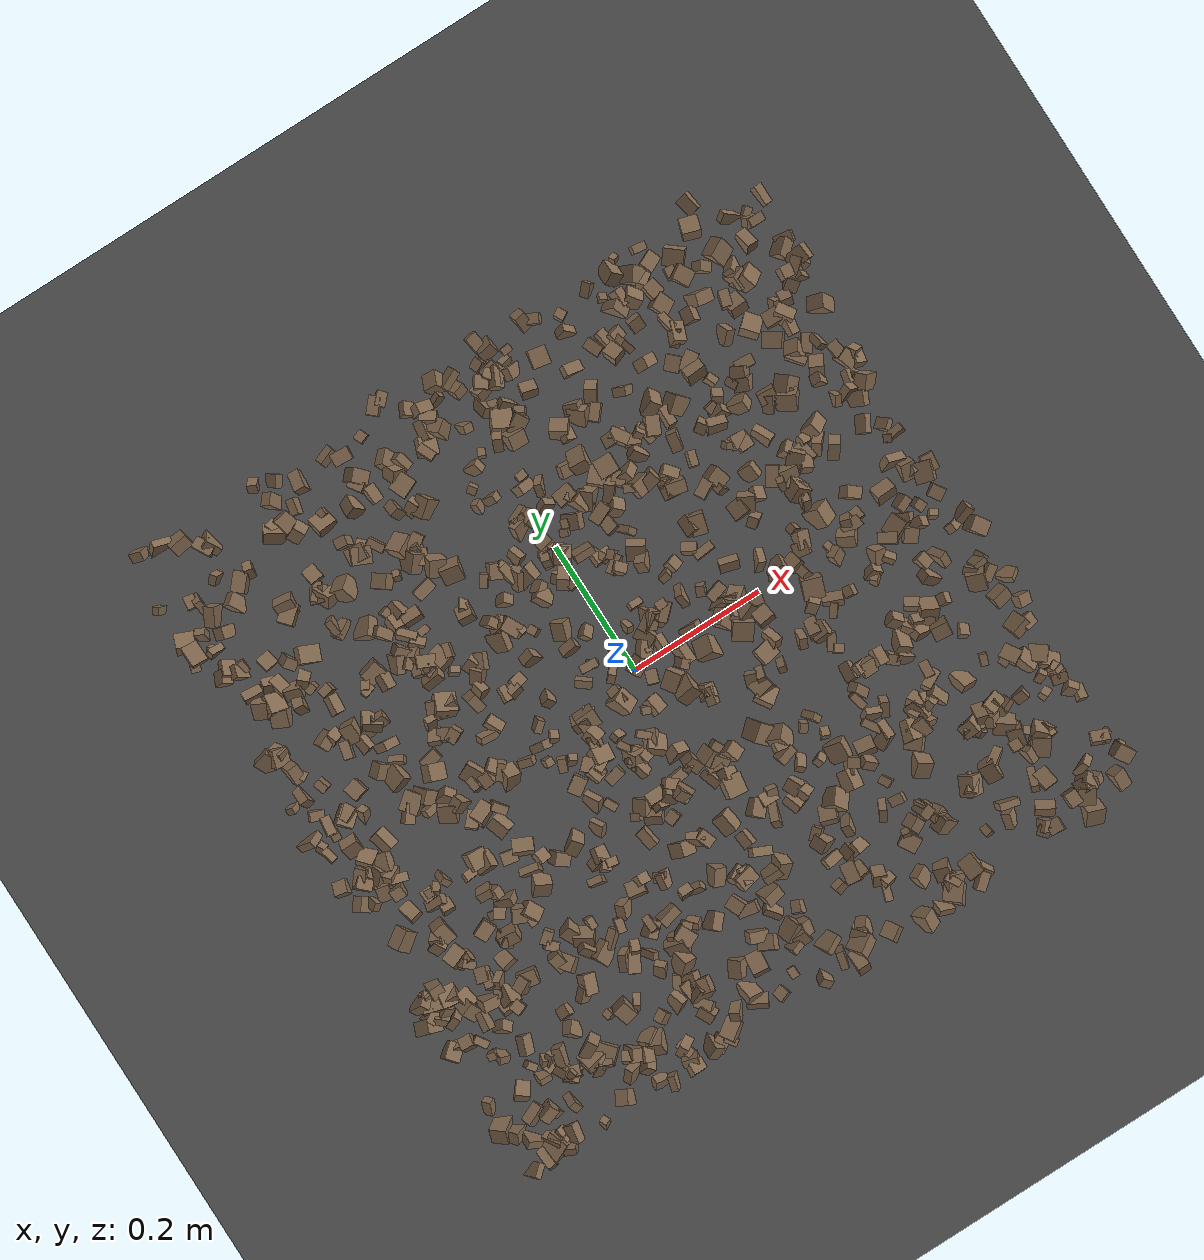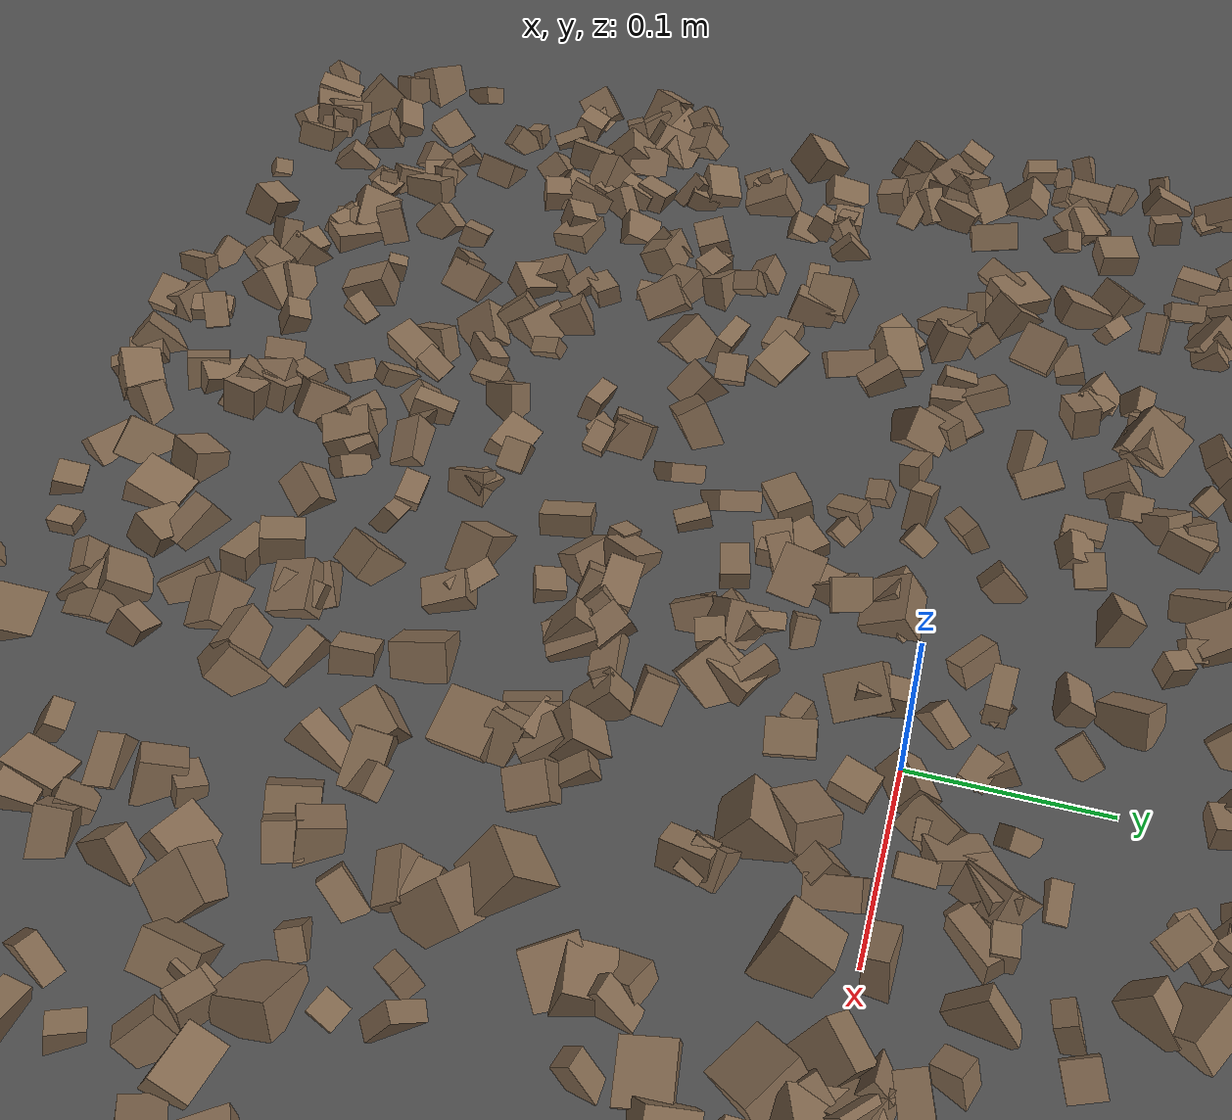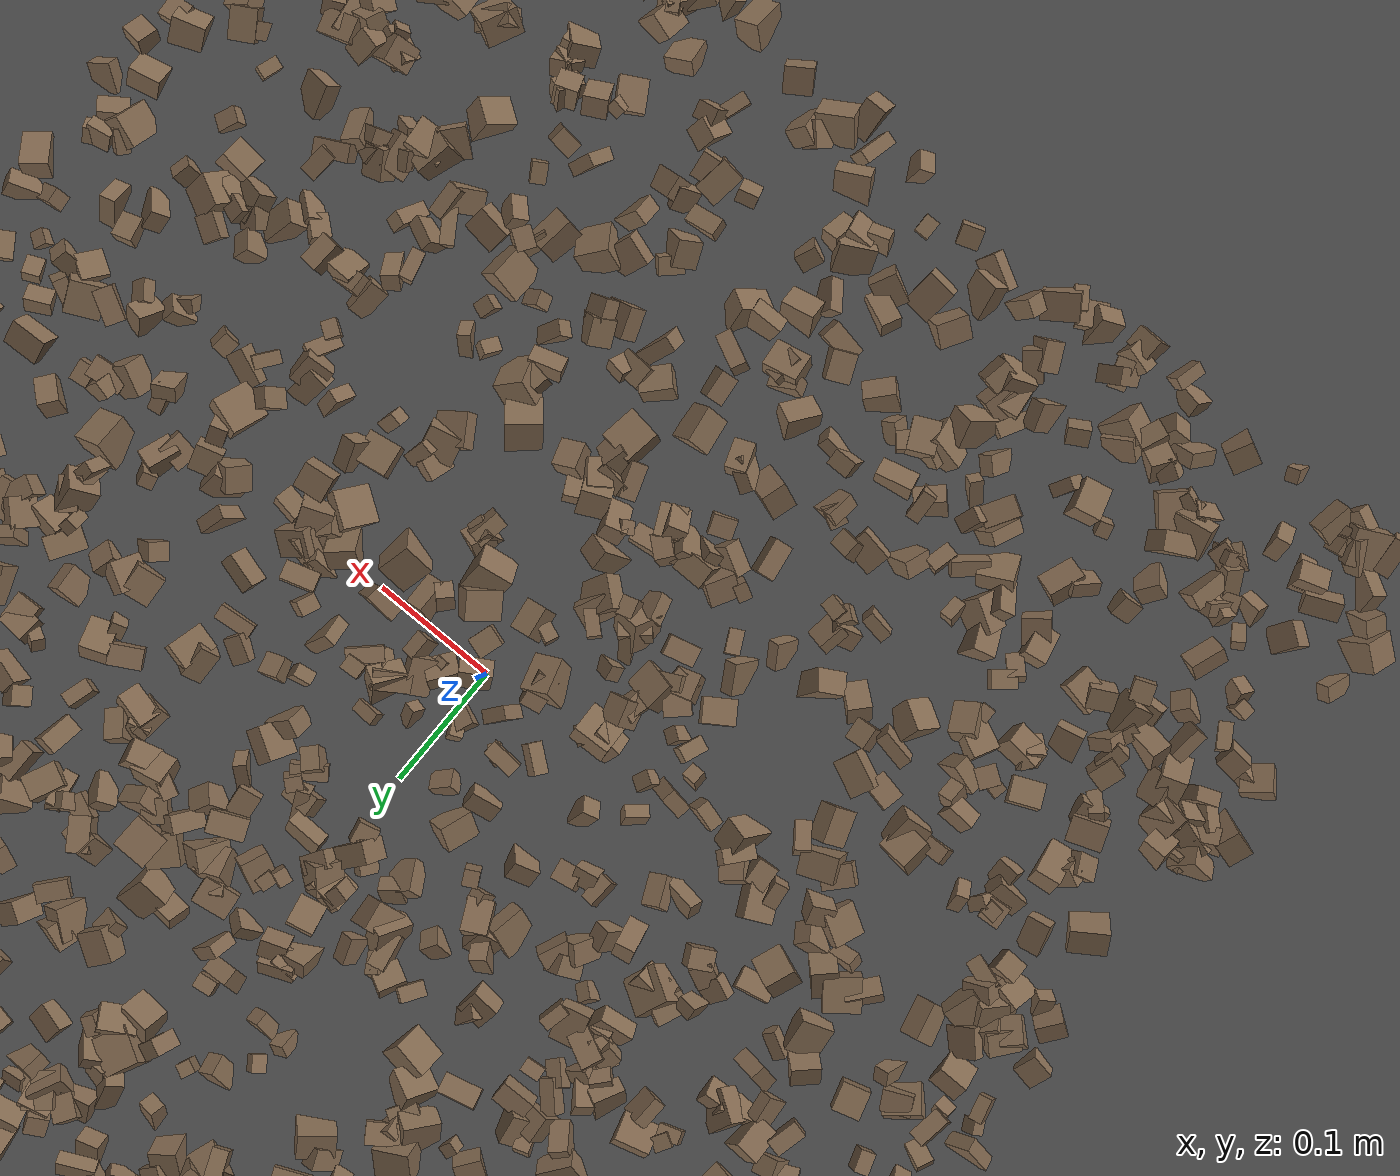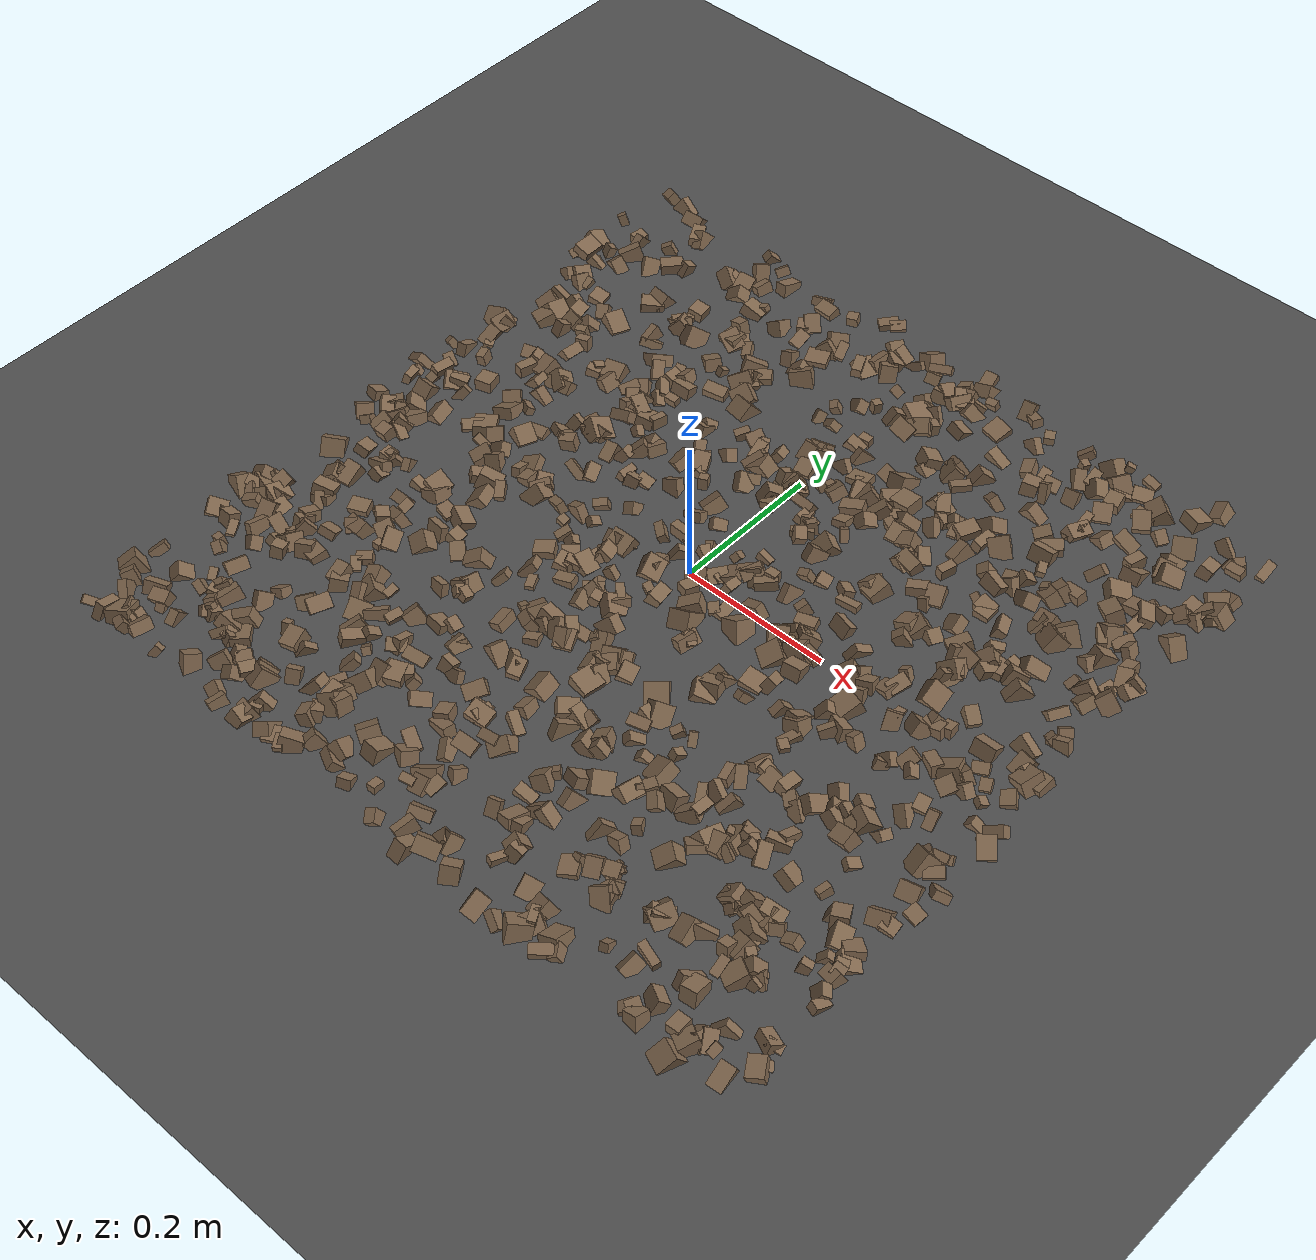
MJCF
<mujoco model="rocky_terrain_scene">
    <compiler angle="radian" inertiafromgeom="true" />
    <option timestep="0.002" gravity="0 0 -9.81" />

    <worldbody>
        <light name="sunlight" pos="5 5 5" dir="-1 -1 -1" diffuse="1 1 1" specular="0.5 0.5 0.5" ambient="0.5 0.5 0.5" />

        <geom name="ground_plane" type="plane" size="50 50 0.1" rgba="0.3 0.3 0.3 1" />

        <body name="rocky_terrain_body">

        </body>
    <body name="rock1" pos="-0.4688875873933853 -0.04461119863729701 0.0002698523621952491"><joint type="free" /><geom type="box" size="0.00882688158561045 0.013316280586744424 0.01122573938016326" quat="0.3058141627618354 0.4034806597948379 0.22487579554171847 0.06582938190160825" rgba="0.5 0.4 0.3 1" /></body><body name="rock2" pos="0.4425001294886409 0.11683367360386665 0.0008755723122365554"><joint type="free" /><geom type="box" size="0.013076307250688361 0.005765137690725225 0.009752733845737212" quat="0.45671762330815496 0.17229904163780238 0.1013147048322064 0.26966863022183624" rgba="0.5 0.4 0.3 1" /></body><body name="rock3" pos="-0.09363125783961013 -0.3443157171516745 1.4855293707890515e-05"><joint type="free" /><geom type="box" size="0.012695281688911614 0.00871560233944568 0.010720164624095162" quat="0.5227350140776598 0.13720260659411468 0.13596777074490554 0.20409460858332007" rgba="0.5 0.4 0.3 1" /></body><body name="rock4" pos="-0.27351592950315273 0.08874538848401103 0.0004283611928709841"><joint type="free" /><geom type="box" size="0.0054717150756604825 0.014196182542549087 0.007532309602367721" quat="0.2531290989594383 0.23447310097002236 0.3673822818416109 0.14501551822892841" rgba="0.5 0.4 0.3 1" /></body><body name="rock5" pos="0.2946560533552087 0.3575846156064023 0.0007060439871362478"><joint type="free" /><geom type="box" size="0.014788126269525186 0.00952247261419396 0.010959527012435449" quat="0.5000277329777583 0.0665116638059828 0.09728042522583846 0.33618017799042044" rgba="0.5 0.4 0.3 1" /></body><body name="rock6" pos="-0.027235725630702645 0.2469802330378339 0.0005758409051833369"><joint type="free" /><geom type="box" size="0.006071424616455161 0.013643263492872426 0.012190969487835114" quat="0.2546156641601886 0.14661818770509627 0.41986142143437805 0.17890472670033716" rgba="0.5 0.4 0.3 1" /></body><body name="rock7" pos="-0.007500611941230084 -0.49112668576850216 0.0006142235734797926"><joint type="free" /><geom type="box" size="0.008692390795265254 0.012504117659437382 0.006578404899133747" quat="0.15178531634428005 0.20095072135955427 0.22570600162012444 0.42155796067604123" rgba="0.5 0.4 0.3 1" /></body><body name="rock8" pos="-0.062063447081919576 -0.11526555147901607 6.988098891096728e-05"><joint type="free" /><geom type="box" size="0.011081657948787675 0.006084741353155485 0.011471657361987294" quat="0.06121719892646091 0.3385941352317591 0.39850641850642105 0.20168224733535903" rgba="0.5 0.4 0.3 1" /></body><body name="rock9" pos="0.20840034522585205 -0.37925441310569563 0.0008152414597164673"><joint type="free" /><geom type="box" size="0.011514800401372014 0.008428759590683583 0.009687985038767503" quat="0.0646346865404267 0.3167638840714417 0.23919744776540294 0.3794039816227287" rgba="0.5 0.4 0.3 1" /></body><body name="rock10" pos="0.46191190316089825 -0.303389551269276 0.000929259857788505"><joint type="free" /><geom type="box" size="0.005648625902507163 0.008845226993414704 0.0051204986878584735" quat="0.1074086638929342 0.24475911101692543 0.45299703838755645 0.19483518670258396" rgba="0.5 0.4 0.3 1" /></body><body name="rock11" pos="-0.11962434564998281 -0.07647665803704473 0.00016924983066303768"><joint type="free" /><geom type="box" size="0.013805961006646304 0.009736973003245344 0.010649659686598806" quat="0.13505946856795295 0.16298751198991154 0.3594799751716687 0.3424730442704667" rgba="0.5 0.4 0.3 1" /></body><body name="rock12" pos="-0.4212229879441698 -0.49560560819010835 0.0007416414818883278"><joint type="free" /><geom type="box" size="0.006368844598291009 0.013711101851693587 0.009281117039114897" quat="0.25544892948638176 0.3395318241583225 0.10107956372287709 0.30393968263241866" rgba="0.5 0.4 0.3 1" /></body><body name="rock13" pos="0.3462050258069389 -0.3144656078523098 0.0009504076369348074"><joint type="free" /><geom type="box" size="0.007951329423022896 0.00864572752125092 0.01484405445460366" quat="0.3796986169657075 0.22244329548573835 0.3070045787372041 0.09085350881134996" rgba="0.5 0.4 0.3 1" /></body><body name="rock14" pos="0.3147839558273322 -0.24637325879813832 0.0007906847326582968"><joint type="free" /><geom type="box" size="0.008010497163155914 0.007527490420473669 0.012567240816382219" quat="0.29168373145145615 0.29269694851230943 0.3334967915562782 0.08212252847995626" rgba="0.5 0.4 0.3 1" /></body><body name="rock15" pos="-0.47770067793958126 0.2939546631377604 0.0007570432474360412"><joint type="free" /><geom type="box" size="0.010249947405254572 0.008335830886393805 0.009888108368076768" quat="0.4191399641830965 0.14705257307181951 0.17537802457345827 0.2584294381716257" rgba="0.5 0.4 0.3 1" /></body><body name="rock16" pos="-0.018714295847965023 0.2606005786326425 0.0006717339360543555"><joint type="free" /><geom type="box" size="0.010737373870700647 0.006050941703398308 0.014011669016433328" quat="0.052506536094226744 0.359021118731036 0.229869477794221 0.35860286738051617" rgba="0.5 0.4 0.3 1" /></body><body name="rock17" pos="0.214208139085047 0.2965682114179282 0.0005278965120310504"><joint type="free" /><geom type="box" size="0.014107764092510616 0.013302879725664483 0.009456913894741441" quat="0.2922476629517961 0.3677004672340065 0.3380931105422434 0.001958759271953941" rgba="0.5 0.4 0.3 1" /></body><body name="rock18" pos="-0.47013310636913086 0.33475409604871886 0.00039052864436731896"><joint type="free" /><geom type="box" size="0.00547504642106492 0.005462135162228018 0.0051471023404301595" quat="0.17153872867812195 0.2619803057792592 0.46557576223560476 0.10090520330701419" rgba="0.5 0.4 0.3 1" /></body><body name="rock19" pos="0.06814069355876662 -0.016545451076091844 0.0005552423745283737"><joint type="free" /><geom type="box" size="0.013383866763264134 0.0075044319768140695 0.010793818197725135" quat="0.38116490654554785 0.14001354180594855 0.06482225187769615 0.41399929977080746" rgba="0.5 0.4 0.3 1" /></body><body name="rock20" pos="0.07717709661003225 0.45115550236096136 0.0008900780383652726"><joint type="free" /><geom type="box" size="0.005424142738396119 0.005045962729297517 0.008710561202655488" quat="0.23921672639204883 0.17867650078687883 0.3960515727059394 0.1860552001151329" rgba="0.5 0.4 0.3 1" /></body><body name="rock21" pos="-0.41125344485304827 0.4151273784723639 0.00023856517042008073"><joint type="free" /><geom type="box" size="0.007548480763894036 0.012250863002782544 0.0054601057488258" quat="0.3645720729619659 0.39152367902570967 0.022565584151095875 0.22133866386122858" rgba="0.5 0.4 0.3 1" /></body><body name="rock22" pos="-0.03387706616800934 -0.3068111906410178 0.0005658143974980039"><joint type="free" /><geom type="box" size="0.006260181638331102 0.007108114363259823 0.012110193466869704" quat="0.10742729342172809 0.2903451198268134 0.3577692405085546 0.24445834624290394" rgba="0.5 0.4 0.3 1" /></body><body name="rock23" pos="0.38537345293715586 0.15110126412648783 0.0007736061400355908"><joint type="free" /><geom type="box" size="0.00984907358681891 0.014849682474302593 0.010738240403022684" quat="0.28938805654749383 0.17208552800643773 0.08909228580648881 0.4494341296395796" rgba="0.5 0.4 0.3 1" /></body><body name="rock24" pos="-0.32860102679709513 0.1312166278950414 0.0005623781652497078"><joint type="free" /><geom type="box" size="0.008684558604190457 0.006812894443701478 0.009697835562666929" quat="0.1594879061943192 0.3150359915957138 0.1500491743890402 0.3754269278209268" rgba="0.5 0.4 0.3 1" /></body><body name="rock25" pos="0.022396148922829373 -0.45141217611630724 0.000222371935082339"><joint type="free" /><geom type="box" size="0.00660636760596777 0.01412063661792171 0.01377553158029346" quat="0.06452741260477207 0.34226860611959076 0.2514381440470067 0.3417658372286305" rgba="0.5 0.4 0.3 1" /></body><body name="rock26" pos="-0.33360473080710873 -0.17802491360240924 0.00028544743861749403"><joint type="free" /><geom type="box" size="0.008354203761300794 0.011118336655715537 0.00822591189417832" quat="0.31547502202073696 0.34377640692342765 0.20469264082483293 0.13605593023100238" rgba="0.5 0.4 0.3 1" /></body><body name="rock27" pos="0.28082469728375037 0.01851974111846555 0.0007486834037805768"><joint type="free" /><geom type="box" size="0.009947698410338962 0.005698620329103273 0.010864659206139767" quat="0.3134762622017836 0.23110527761213484 0.16699461858592557 0.288423841600156" rgba="0.5 0.4 0.3 1" /></body><body name="rock28" pos="0.34977417304041947 0.21009333727796442 2.4989944331221036e-05"><joint type="free" /><geom type="box" size="0.007612917824923777 0.013559239358828547 0.007353786815277642" quat="0.130544183457206 0.13995502844771843 0.5743322918009597 0.1551684962941159" rgba="0.5 0.4 0.3 1" /></body><body name="rock29" pos="0.2045525274602077 -0.4894310547724411 0.0003035669869976058"><joint type="free" /><geom type="box" size="0.013411511520120711 0.012330693766115453 0.014395390806826648" quat="0.19553254236110784 0.0691800199055604 0.4484445238827221 0.28684291385060956" rgba="0.5 0.4 0.3 1" /></body><body name="rock30" pos="-0.007045197178698559 0.042508847080786505 0.000851767360975523"><joint type="free" /><geom type="box" size="0.005263887901259003 0.006358122743259746 0.010808434448101652" quat="0.32214867971471034 0.4951138721940325 0.0571286354370918 0.12560881265416537" rgba="0.5 0.4 0.3 1" /></body><body name="rock31" pos="0.29504008478717014 -0.2534334157911182 0.0009384161271397636"><joint type="free" /><geom type="box" size="0.014679220853663653 0.01115298765524602 0.009243491555299452" quat="0.11881628419195202 0.3628397874271515 0.4051480856317272 0.11319584274916925" rgba="0.5 0.4 0.3 1" /></body><body name="rock32" pos="-0.17908780631885313 0.4621744790075396 0.00014524317876473636"><joint type="free" /><geom type="box" size="0.009124377723245407 0.009480558887596895 0.013341060501760316" quat="0.23297504957701473 0.2833557513955594 0.20691853178041403 0.27675066724701175" rgba="0.5 0.4 0.3 1" /></body><body name="rock33" pos="0.2676953491806453 -0.014813150338419234 0.0006194307888474694"><joint type="free" /><geom type="box" size="0.007626667909495594 0.013313939980224836 0.006820767863434905" quat="0.3241144343182313 0.10835686270179189 0.32537935880434943 0.24214934417562733" rgba="0.5 0.4 0.3 1" /></body><body name="rock34" pos="-0.4392037502271544 0.20663286636682288 0.00016038809465433203"><joint type="free" /><geom type="box" size="0.012806206732655983 0.012096201210141714 0.010557242606430664" quat="0.08144574105782641 0.15208291555958128 0.6756243323204947 0.09084701106209758" rgba="0.5 0.4 0.3 1" /></body><body name="rock35" pos="-0.0523314229955979 -0.10560680912176912 0.00020625786006927527"><joint type="free" /><geom type="box" size="0.0064188707875162 0.007568839601721655 0.01421499100136182" quat="0.7651715462079045 0.0020747662581591976 0.11889272728030334 0.11386096025363296" rgba="0.5 0.4 0.3 1" /></body><body name="rock36" pos="0.04633710053397444 0.3722815942996335 0.0009645713560011874"><joint type="free" /><geom type="box" size="0.01060583179098366 0.011657463014445524 0.0143549603830301" quat="0.1313680713216079 0.23001918527493798 0.22108425257973097 0.41752849082372306" rgba="0.5 0.4 0.3 1" /></body><body name="rock37" pos="0.4495064796813887 0.1644763715077725 0.000540240790128919"><joint type="free" /><geom type="box" size="0.012564045649689787 0.006374857724921285 0.012581801454930035" quat="0.06350223019385984 0.6029426580962955 0.07414295289272127 0.2594121588171233" rgba="0.5 0.4 0.3 1" /></body><body name="rock38" pos="-0.3079399955050023 -0.19377150079835936 0.00016229670045018218"><joint type="free" /><geom type="box" size="0.01109293762216708 0.010543856526301468 0.013754443177452336" quat="0.25404804783981333 0.36978402292453816 0.16143873597131495 0.21472919326433354" rgba="0.5 0.4 0.3 1" /></body><body name="rock39" pos="0.4854920978033802 -0.3395867599181782 0.0003581653055452996"><joint type="free" /><geom type="box" size="0.006518351393547931 0.012344113369445606 0.008264644045369795" quat="0.37620683675139655 0.33619918673167437 0.2694759051769317 0.018118071339997342" rgba="0.5 0.4 0.3 1" /></body><body name="rock40" pos="0.054887886012721876 0.4455195260776952 0.0005241678527308142"><joint type="free" /><geom type="box" size="0.0144583256255046 0.010409588214221579 0.012595368230345037" quat="0.09596476462021174 0.2194518124256691 0.35498339752609553 0.32960002542802364" rgba="0.5 0.4 0.3 1" /></body><body name="rock41" pos="-0.0008017978465033604 -0.14726392212040673 0.0006518245362469877"><joint type="free" /><geom type="box" size="0.008898547621443511 0.012967896212566454 0.008935949914847186" quat="0.39865156477674957 0.05782074308195388 0.346815251999819 0.19671244014147757" rgba="0.5 0.4 0.3 1" /></body><body name="rock42" pos="-0.4324389786582179 -0.0785950641771993 0.0005126622242953874"><joint type="free" /><geom type="box" size="0.008492175167615103 0.014416937368853036 0.009077844513930683" quat="0.22967342060003137 0.2774896410252019 0.21370779931866504 0.27912913905610165" rgba="0.5 0.4 0.3 1" /></body><body name="rock43" pos="-0.17801329432866175 -0.2031228241043036 0.00012813715978874396"><joint type="free" /><geom type="box" size="0.0067221127629995756 0.010887946943814147 0.005969230246822285" quat="0.04050939395764514 0.2005619827664475 0.4249852560751714 0.333943367200736" rgba="0.5 0.4 0.3 1" /></body><body name="rock44" pos="0.2874607754034154 0.456023224547779 0.0006158131252158627"><joint type="free" /><geom type="box" size="0.01165902673684393 0.013668713671863113 0.013912472570256695" quat="0.4655781163335014 0.20984201412407513 0.07503524416571845 0.249544625376705" rgba="0.5 0.4 0.3 1" /></body><body name="rock45" pos="0.4630427937588655 0.1815013463442955 0.00026802797337565775"><joint type="free" /><geom type="box" size="0.009964413352727552 0.007938289159908333 0.007097709365404342" quat="0.4442819275221705 0.1058091513488801 0.09074617115083854 0.3591627499781108" rgba="0.5 0.4 0.3 1" /></body><body name="rock46" pos="-0.38234186092103717 0.21784693823258994 0.0009534176134879955"><joint type="free" /><geom type="box" size="0.007347988633575248 0.01255024451206472 0.005175890806802541" quat="0.3919979211937554 0.4683735438916412 0.045793738754926185 0.09383479615967719" rgba="0.5 0.4 0.3 1" /></body><body name="rock47" pos="0.41472228312716086 0.3700010984599176 0.00012674396393267884"><joint type="free" /><geom type="box" size="0.011954412641922752 0.013941093047841285 0.014881014600121884" quat="0.285490418169275 0.18215321898615983 0.05774788405721679 0.4746084787873483" rgba="0.5 0.4 0.3 1" /></body><body name="rock48" pos="0.13668052174071077 -0.2945692168869003 0.00040352908034526594"><joint type="free" /><geom type="box" size="0.01378166142261868 0.011594426469162698 0.01365063000508443" quat="0.28129438327473993 0.44423052973664673 0.2533602416535853 0.02111484533502809" rgba="0.5 0.4 0.3 1" /></body><body name="rock49" pos="0.10936591623189018 0.05274999552986115 0.0009096605363874777"><joint type="free" /><geom type="box" size="0.011643789495719824 0.012574069155743045 0.005356930445043237" quat="0.20798042170896885 0.289715546484662 0.10416063506937119 0.3981433967369979" rgba="0.5 0.4 0.3 1" /></body><body name="rock50" pos="0.4724746290085652 0.08271359432172143 2.663844810527971e-05"><joint type="free" /><geom type="box" size="0.005299376899023567 0.010334378313807183 0.014187355197085041" quat="0.30841839119634695 0.16703317021981443 0.25094192157092754 0.27360651701291105" rgba="0.5 0.4 0.3 1" /></body><body name="rock51" pos="0.22367395696315517 0.40043062705699173 0.00019614539505837225"><joint type="free" /><geom type="box" size="0.009026389336289836 0.008771883343513674 0.01031068653583549" quat="0.33396971825740995 0.030489261201998314 0.4859531789442341 0.14958784159635763" rgba="0.5 0.4 0.3 1" /></body><body name="rock52" pos="0.4908997355117355 -0.4169876050991945 0.00023382803250613027"><joint type="free" /><geom type="box" size="0.005623402717951831 0.006219743041436601 0.009762667919191094" quat="0.1163275446265116 0.3144208134506119 0.32446873812837884 0.24478290379449763" rgba="0.5 0.4 0.3 1" /></body><body name="rock53" pos="0.054454764593260374 0.45185010821840565 0.00019055687798868082"><joint type="free" /><geom type="box" size="0.012175555428693488 0.009876581869801985 0.011662425051166842" quat="0.3335627635358467 0.5696836293663502 0.029685518928291247 0.06706808816951192" rgba="0.5 0.4 0.3 1" /></body><body name="rock54" pos="-0.22425682931546997 -0.1583437407967121 6.831701192779693e-05"><joint type="free" /><geom type="box" size="0.011765436688121918 0.01296450830887801 0.009253734213809633" quat="0.03883550368763555 0.23867259783086558 0.31668579661739227 0.40580610186410665" rgba="0.5 0.4 0.3 1" /></body><body name="rock55" pos="-0.3368534944114162 -0.11242353095478952 0.00029889536750374047"><joint type="free" /><geom type="box" size="0.006399293757868031 0.011375473770789294 0.00701047434756054" quat="0.3995079767546049 0.06193587366691647 0.11451296771221593 0.4240431818662626" rgba="0.5 0.4 0.3 1" /></body><body name="rock56" pos="0.43031556680733785 0.166533683407752 6.568670737203509e-05"><joint type="free" /><geom type="box" size="0.005000457643219101 0.01009235251127226 0.00851784965797135" quat="0.04214220327916793 0.10719383474624165 0.2794621298521737 0.5712018321224166" rgba="0.5 0.4 0.3 1" /></body><body name="rock57" pos="0.1675415536060122 0.0875754594539434 0.00016897295422946336"><joint type="free" /><geom type="box" size="0.005789650178938376 0.0059073609460254225 0.014668789552861782" quat="0.26471365770076394 0.21232540225323338 0.27173954758287766 0.2512213924631249" rgba="0.5 0.4 0.3 1" /></body><body name="rock58" pos="0.4293370051770016 -0.0011401155637781324 0.0003719245275179004"><joint type="free" /><geom type="box" size="0.010292197568294265 0.006966217809864901 0.010271207512050313" quat="0.3885920861704544 0.009317109750680433 0.4033451474930139 0.19874565658585128" rgba="0.5 0.4 0.3 1" /></body><body name="rock59" pos="0.33545355488595363 -0.13133900845223068 0.0008240647644974434"><joint type="free" /><geom type="box" size="0.00768722821344881 0.009201753540210281 0.009798193850622122" quat="0.31159229132303184 0.362065951238345 0.3188935834073849 0.007448174031238278" rgba="0.5 0.4 0.3 1" /></body><body name="rock60" pos="-0.4712193054826206 -0.2532228725082579 8.282995989337062e-05"><joint type="free" /><geom type="box" size="0.007324210375257833 0.00894939480188139 0.013849694021527841" quat="0.3387290114658671 0.04882701036664734 0.3404322269411259 0.2720117512263596" rgba="0.5 0.4 0.3 1" /></body><body name="rock61" pos="0.2133497217025856 0.15835941989436153 0.0009412974495680239"><joint type="free" /><geom type="box" size="0.008105429305722788 0.009940026273705943 0.012986691787078387" quat="0.21675536652368224 0.15719755806768929 0.30928025229284045 0.316766823115788" rgba="0.5 0.4 0.3 1" /></body><body name="rock62" pos="-0.12322436038488227 0.15134995057040546 0.00044382880142903615"><joint type="free" /><geom type="box" size="0.010921004773342551 0.007957506557484225 0.01140447407255062" quat="0.3906297846408907 0.11596815379346422 0.2544683792486611 0.23893368231698392" rgba="0.5 0.4 0.3 1" /></body><body name="rock63" pos="0.03237503791327745 0.43559398000165694 0.0003689873400254549"><joint type="free" /><geom type="box" size="0.008128375420295358 0.008987139650739242 0.014883464333610343" quat="0.044091071375608595 0.4122065665071838 0.1719674071004855 0.3717349550167221" rgba="0.5 0.4 0.3 1" /></body><body name="rock64" pos="0.17354430150762767 -0.09818335189478289 0.000328575068522587"><joint type="free" /><geom type="box" size="0.005502079173386127 0.014007417368982505 0.005444146660519752" quat="0.21841348316489545 0.31596465213528413 0.1117602949934089 0.3538615697064116" rgba="0.5 0.4 0.3 1" /></body><body name="rock65" pos="0.3184672660923056 -0.25377612115016523 0.000651150939445204"><joint type="free" /><geom type="box" size="0.0058061706174366455 0.013380505710756475 0.010206169353980814" quat="0.32075817943058466 0.07624843237597302 0.1919611688371607 0.4110322193562816" rgba="0.5 0.4 0.3 1" /></body><body name="rock66" pos="0.4166226344760454 -0.045114073181316994 0.0005240519617237175"><joint type="free" /><geom type="box" size="0.010816229174128179 0.005076552250845832 0.010721552114016802" quat="0.2534504684431109 0.38893331243739454 0.13721065492220388 0.2204055641972907" rgba="0.5 0.4 0.3 1" /></body><body name="rock67" pos="-0.2644095886884479 0.22993877322200518 0.00036150727472183464"><joint type="free" /><geom type="box" size="0.01233482479963208 0.014513555918701387 0.007493526390535295" quat="0.04181353674176515 0.2790261045062251 0.32598699890318755 0.3531733598488222" rgba="0.5 0.4 0.3 1" /></body><body name="rock68" pos="0.20804502198054664 -0.3104530384467328 5.499622932385295e-05"><joint type="free" /><geom type="box" size="0.006029350812669012 0.008246382819245748 0.008120261313075344" quat="0.4490129506590351 0.33457923007107215 0.05230570999473092 0.16410210927516183" rgba="0.5 0.4 0.3 1" /></body><body name="rock69" pos="0.07273955502746543 0.28216667628120595 0.0004260085050979198"><joint type="free" /><geom type="box" size="0.009215597114365445 0.005675818696735778 0.014920401504964199" quat="0.1371367477143957 0.3945836758620415 0.2058987807650837 0.26238079565847905" rgba="0.5 0.4 0.3 1" /></body><body name="rock70" pos="-0.4153464474330766 0.28137686181777133 0.0006300244425690813"><joint type="free" /><geom type="box" size="0.010293719742098691 0.010474323099048987 0.008992925863701678" quat="0.7902211158652396 0.024129732230212145 0.10363571497089294 0.08201343693365534" rgba="0.5 0.4 0.3 1" /></body><body name="rock71" pos="0.12957769059654667 -0.4134959230700116 0.00021848470669988063"><joint type="free" /><geom type="box" size="0.010775158942260324 0.010093710691421474 0.009262291099995292" quat="0.392860804491582 0.20372163902007168 0.34377618463224735 0.05964137185609902" rgba="0.5 0.4 0.3 1" /></body><body name="rock72" pos="-0.23632220375345536 0.20751168908112771 0.0008856740283156042"><joint type="free" /><geom type="box" size="0.013971741035865737 0.005788745264356104 0.010033201626230032" quat="0.2397144055145334 0.07466696567639683 0.1155214077104956 0.5700972210985742" rgba="0.5 0.4 0.3 1" /></body><body name="rock73" pos="0.045270779765249625 0.46547214807934156 0.0009935575492654078"><joint type="free" /><geom type="box" size="0.007485392239579562 0.008916506671225552 0.008149264282255795" quat="0.27966599451412083 0.12454760095453356 0.2810304064801605 0.31475599805118515" rgba="0.5 0.4 0.3 1" /></body><body name="rock74" pos="-0.11879259739462222 -0.2602071394934333 0.0003279819795546725"><joint type="free" /><geom type="box" size="0.011383557158167298 0.010148512138358462 0.006096036105800236" quat="0.33942734547568354 0.20786299754873613 0.11571040099771836 0.33699925597786196" rgba="0.5 0.4 0.3 1" /></body><body name="rock75" pos="0.15251264564847122 -0.18559310055743306 0.0003560239002225972"><joint type="free" /><geom type="box" size="0.007314783835986574 0.009616910823975876 0.005591781969994568" quat="0.27436455588572994 0.3703613621193983 0.12753920835750943 0.22773487363736225" rgba="0.5 0.4 0.3 1" /></body><body name="rock76" pos="-0.438981700037851 0.2253802598930963 0.0007381700312974605"><joint type="free" /><geom type="box" size="0.014557560037459012 0.010110278382935985 0.012689103961340882" quat="0.21211677913132912 0.3246175690059955 0.34875544967769306 0.11451020218498226" rgba="0.5 0.4 0.3 1" /></body><body name="rock77" pos="0.0309652386757282 -0.16494718068296277 0.00042120889866139314"><joint type="free" /><geom type="box" size="0.009554955872233211 0.011905677367139069 0.011285061602599487" quat="0.3162950549823192 0.42847607930063714 0.09595818903659278 0.15927067668045095" rgba="0.5 0.4 0.3 1" /></body><body name="rock78" pos="-0.06714675573759354 0.194054527010029 0.00015598836728145582"><joint type="free" /><geom type="box" size="0.01433290598503726 0.013786801987157506 0.008327516947215056" quat="0.13521826069642742 0.46500387572419893 0.17409206544312925 0.22568579813624434" rgba="0.5 0.4 0.3 1" /></body><body name="rock79" pos="-0.05100211833828294 0.15384378452780612 0.0007510346573772911"><joint type="free" /><geom type="box" size="0.012795528229092138 0.007323711351305074 0.011094456482217633" quat="0.024619327007202176 0.29565438518393816 0.3997000278219039 0.28002625998695585" rgba="0.5 0.4 0.3 1" /></body><body name="rock80" pos="-0.05621060982100423 -0.2931956484614089 0.0006158408719340397"><joint type="free" /><geom type="box" size="0.009578053811589972 0.010214787801079723 0.01383623167216803" quat="0.01907955704923333 0.1991954699946685 0.3018995638463072 0.47982540910979105" rgba="0.5 0.4 0.3 1" /></body><body name="rock81" pos="-0.04863992150843999 0.03958753637272594 0.0006410238128207305"><joint type="free" /><geom type="box" size="0.00597405383746412 0.014072455018536927 0.012834358884533405" quat="0.2618088702527498 0.2545840727186946 0.23839076359908512 0.2452162934294705" rgba="0.5 0.4 0.3 1" /></body><body name="rock82" pos="-0.14633583463364364 -0.24421208499126412 0.0005928971134658498"><joint type="free" /><geom type="box" size="0.007411395423485201 0.010205144588405324 0.008772355872603062" quat="0.20716989736086308 0.31406329623520873 0.3345644331322942 0.14420237327163393" rgba="0.5 0.4 0.3 1" /></body><body name="rock83" pos="-0.14756267991351069 -0.3343143644399704 0.0009391070622676602"><joint type="free" /><geom type="box" size="0.006020488704403157 0.008622543739077337 0.009798916409242634" quat="0.05627757781013573 0.43314437743859985 0.3307311775083138 0.1798468672429506" rgba="0.5 0.4 0.3 1" /></body><body name="rock84" pos="-0.26891057495982373 0.43828293456513945 0.00013609219158489285"><joint type="free" /><geom type="box" size="0.011324007792353335 0.011257851288445291 0.006129171749574653" quat="0.3131863784287537 0.24422911833873528 0.17278666306814414 0.26979784016436686" rgba="0.5 0.4 0.3 1" /></body><body name="rock85" pos="-0.37607804730577266 -0.4038409553591694 0.0005381799130346024"><joint type="free" /><geom type="box" size="0.011923735105801778 0.006964045805637621 0.008714375650548627" quat="0.1846911288450837 0.25077650842416416 0.5481809834912676 0.016351379239484484" rgba="0.5 0.4 0.3 1" /></body><body name="rock86" pos="0.44332674907377734 0.41208069134719905 0.00039641126751090595"><joint type="free" /><geom type="box" size="0.013815188085615621 0.009317193647182042 0.008648842994713092" quat="0.25203716049110125 0.22766901904347137 0.3280256924492427 0.19226812801618473" rgba="0.5 0.4 0.3 1" /></body><body name="rock87" pos="0.17096690827540817 -0.006539542994458358 0.000748155896534872"><joint type="free" /><geom type="box" size="0.01230210520849844 0.014405689990426171 0.014139394440242065" quat="0.510928411771355 0.34252615037232226 0.013253208190397835 0.13329222966592497" rgba="0.5 0.4 0.3 1" /></body><body name="rock88" pos="0.07463858642554799 0.23303385298593293 0.0004892795655948512"><joint type="free" /><geom type="box" size="0.009534523872357703 0.012736681439939553 0.013887316290613815" quat="0.223342822605242 0.041880163961391804 0.27774780506579216 0.457029208367574" rgba="0.5 0.4 0.3 1" /></body><body name="rock89" pos="-0.3070722851314269 0.3195086618043519 0.0007692471796842774"><joint type="free" /><geom type="box" size="0.011842761082639245 0.005232229987119196 0.01323733180686995" quat="0.39526050930236806 0.207769710027773 0.15259369899326758 0.24437608167659128" rgba="0.5 0.4 0.3 1" /></body><body name="rock90" pos="0.0576780106275917 0.4935101391297517 0.000330290173767116"><joint type="free" /><geom type="box" size="0.013642420090765179 0.007941534392890862 0.00864110349963783" quat="0.16517619235610406 0.29553957993627034 0.2247240354958834 0.3145601922117421" rgba="0.5 0.4 0.3 1" /></body><body name="rock91" pos="0.40258530958501115 0.27937296665534994 0.00042773483729076437"><joint type="free" /><geom type="box" size="0.013827759203011249 0.011164788519197732 0.014336306264356648" quat="0.10585420863924608 0.19908455308752768 0.640661967298142 0.054399270975084256" rgba="0.5 0.4 0.3 1" /></body><body name="rock92" pos="0.46365966136119663 0.08388046565099372 0.0006401625976365704"><joint type="free" /><geom type="box" size="0.005867346539417945 0.005630938504473072 0.009521961077957119" quat="0.026491020112976747 0.49357470143947607 0.30322510750805826 0.17670917093948904" rgba="0.5 0.4 0.3 1" /></body><body name="rock93" pos="0.0268677115724707 0.01843797987949225 0.0005547223354062239"><joint type="free" /><geom type="box" size="0.009840000694444687 0.006556269297162132 0.012628989869912986" quat="0.017451406738549738 0.22483236455650427 0.341713158175659 0.416003070529287" rgba="0.5 0.4 0.3 1" /></body><body name="rock94" pos="0.13492887953077393 -0.42638837787819617 0.000492096344391731"><joint type="free" /><geom type="box" size="0.006813148971523356 0.014186954180883518 0.00884831939174717" quat="0.2404932815062083 0.21707022374238746 0.37112109807433585 0.17131539667706838" rgba="0.5 0.4 0.3 1" /></body><body name="rock95" pos="-0.3665065341471877 -0.3861324018776445 0.00016179707837236012"><joint type="free" /><geom type="box" size="0.014828372150871225 0.006784506921345325 0.011836011715706998" quat="0.04331807700987803 0.48281842140562525 0.3701176792318796 0.10374582235261709" rgba="0.5 0.4 0.3 1" /></body><body name="rock96" pos="0.41725896237476257 0.30473725601892887 0.000442339533133589"><joint type="free" /><geom type="box" size="0.010637849986819374 0.00911337391964781 0.011930177832992883" quat="0.304118593477125 0.21331421705956438 0.21612848154890466 0.266438707914406" rgba="0.5 0.4 0.3 1" /></body><body name="rock97" pos="-0.26352595924379907 0.06517065938515709 0.0008170448698889809"><joint type="free" /><geom type="box" size="0.008854674546573094 0.009458776057595365 0.009412596763914077" quat="0.39416636180120596 0.23095040964485647 0.18332680290467818 0.19155642564925932" rgba="0.5 0.4 0.3 1" /></body><body name="rock98" pos="0.17243394579542815 -0.20995665192403945 0.0007235838928947408"><joint type="free" /><geom type="box" size="0.00728850155941675 0.006959208240916059 0.0060836153229808475" quat="0.16376209753444748 0.44744931318219 0.012917059756667074 0.37587152952669545" rgba="0.5 0.4 0.3 1" /></body><body name="rock99" pos="-0.36591003925241594 0.20298077888406518 0.0004387284199869802"><joint type="free" /><geom type="box" size="0.0064713690507387485 0.013523988151742408 0.008663138831292588" quat="0.24486993793602063 0.19478078013286423 0.27853262848023375 0.28181665345088136" rgba="0.5 0.4 0.3 1" /></body><body name="rock100" pos="0.3251607190366501 0.2572585330217154 0.000358293330820564"><joint type="free" /><geom type="box" size="0.009238184637045854 0.010088787980402338 0.00566621872997498" quat="0.2909676545148854 0.08926996072528365 0.2909430141671896 0.3288193705926414" rgba="0.5 0.4 0.3 1" /></body><body name="rock101" pos="-0.4870716584732726 0.011622949470391553 9.29548187393413e-05"><joint type="free" /><geom type="box" size="0.009782919383161318 0.005170731378807319 0.01445395181482665" quat="0.3712995553140911 0.06208347731466921 0.08892379861576041 0.47769316875547935" rgba="0.5 0.4 0.3 1" /></body><body name="rock102" pos="0.08840092510377762 -0.36002787622482146 0.00029306661199666773"><joint type="free" /><geom type="box" size="0.007167552302531254 0.00707645335142274 0.012780075411297604" quat="0.18998348245016364 0.28409336963538395 0.29507967613209063 0.23084347178236175" rgba="0.5 0.4 0.3 1" /></body><body name="rock103" pos="-0.4237573953458299 -0.1681731111944358 0.000973802968105493"><joint type="free" /><geom type="box" size="0.008973489420591776 0.010695305323304859 0.013301185678769794" quat="0.04886826324925833 0.31192430289544154 0.4429746904663858 0.19623274338891436" rgba="0.5 0.4 0.3 1" /></body><body name="rock104" pos="0.46405799313778084 0.3317745992236365 0.00012257726954936833"><joint type="free" /><geom type="box" size="0.00945444393008026 0.010965850012764925 0.008635638576434929" quat="0.1670672932092768 0.15517533190612467 0.21625372633707254 0.46150364854752607" rgba="0.5 0.4 0.3 1" /></body><body name="rock105" pos="0.053622937246036284 0.0519099823425232 4.241130745135091e-05"><joint type="free" /><geom type="box" size="0.013693711687503097 0.01361568493506499 0.00850456316047256" quat="0.29598304453753066 0.2151006577917025 0.4848772507642678 0.004039046906499078" rgba="0.5 0.4 0.3 1" /></body><body name="rock106" pos="-0.022830687639816993 0.25810221598654115 0.0007588706445827749"><joint type="free" /><geom type="box" size="0.009047804123535445 0.00880583244504426 0.010852131363966875" quat="0.4473034901985124 0.0884912272482877 0.37009605177043997 0.09410923078275985" rgba="0.5 0.4 0.3 1" /></body><body name="rock107" pos="-0.3797298956627926 -0.3005958912145775 0.0006662375944957223"><joint type="free" /><geom type="box" size="0.008216153258934765 0.014122887513406963 0.008188383737104253" quat="0.21461668580451 0.1889242899725886 0.3351779898635169 0.26128103435938455" rgba="0.5 0.4 0.3 1" /></body><body name="rock108" pos="-0.40612131572430576 0.06850852233733484 0.00021472079241033549"><joint type="free" /><geom type="box" size="0.010957481430118349 0.013264535107635703 0.011335914761109827" quat="0.44543043294630924 0.42931709020289627 0.06395362358034254 0.06129885327045194" rgba="0.5 0.4 0.3 1" /></body><body name="rock109" pos="-0.26757151940520607 -0.4479802980517775 0.0003205550708848113"><joint type="free" /><geom type="box" size="0.010648529700767934 0.014470068511643518 0.007257615467284486" quat="0.2727304197497628 0.32959466188716646 0.2583849789313799 0.13928993943169077" rgba="0.5 0.4 0.3 1" /></body><body name="rock110" pos="0.015481739101955716 -0.019335615041081722 0.0004074592500798178"><joint type="free" /><geom type="box" size="0.009992214066725921 0.009522080366511903 0.008369747547664569" quat="0.30684576962654253 0.2701289289540128 0.22082956313138527 0.2021957382880593" rgba="0.5 0.4 0.3 1" /></body><body name="rock111" pos="0.4739440504910416 -0.18098248875991663 0.0005023625276578142"><joint type="free" /><geom type="box" size="0.010310958259129685 0.008477820609961748 0.012658691906796065" quat="0.1266702651538454 0.31459187121855736 0.19961500000850055 0.3591228636190967" rgba="0.5 0.4 0.3 1" /></body><body name="rock112" pos="0.13279642622870103 0.23409594242077947 0.0009954894678910985"><joint type="free" /><geom type="box" size="0.007184171918996107 0.014318443383041023 0.013150366823263666" quat="0.03523140437109513 0.3483769487348596 0.3795013490606292 0.23689029783341603" rgba="0.5 0.4 0.3 1" /></body><body name="rock113" pos="-0.06750849743070508 -0.1746213919692634 0.00030879294094093867"><joint type="free" /><geom type="box" size="0.005609097441679487 0.011971786473523106 0.0066583886003129065" quat="0.35902213917473436 0.09080538607479234 0.23804622149074778 0.3121262532597255" rgba="0.5 0.4 0.3 1" /></body><body name="rock114" pos="-0.14057025232577514 -0.30426689159048537 0.0005125111203364965"><joint type="free" /><geom type="box" size="0.007802772432706545 0.0077629410419310894 0.014777399558240329" quat="0.14317137363102034 0.3074774912840327 0.24540569697593181 0.30394543810901514" rgba="0.5 0.4 0.3 1" /></body><body name="rock115" pos="0.12294304006471468 -0.22564332714193702 0.0008499852469341997"><joint type="free" /><geom type="box" size="0.006572341487068083 0.0065515381032071 0.011759616486862" quat="0.04823839055678427 0.2068684577074113 0.49000036101218175 0.25489279072362275" rgba="0.5 0.4 0.3 1" /></body><body name="rock116" pos="0.3287601676955999 -0.2493916950124463 0.000663950073838828"><joint type="free" /><geom type="box" size="0.014608830944971354 0.007930637910761647 0.008047758750539962" quat="0.0666463056245779 0.29399495067351644 0.346503251996889 0.2928554917050167" rgba="0.5 0.4 0.3 1" /></body><body name="rock117" pos="0.25232264128866644 0.11317674657971288 0.0006507447299539563"><joint type="free" /><geom type="box" size="0.011844312700388982 0.011496010392910906 0.012111922192317437" quat="0.2830889936169648 0.345487140798026 0.08810202462290435 0.2833218409621047" rgba="0.5 0.4 0.3 1" /></body><body name="rock118" pos="0.3664028627190201 -0.12516744397293145 0.0007400930895152476"><joint type="free" /><geom type="box" size="0.007922883313034328 0.007322169511156711 0.01039284834227837" quat="0.3776874968920012 0.27375383547629806 0.23714906735350658 0.11140960027819408" rgba="0.5 0.4 0.3 1" /></body><body name="rock119" pos="-0.028742627816210953 -0.09780379008769602 0.0008104829417573512"><joint type="free" /><geom type="box" size="0.01359544459217964 0.008046307293171075 0.014648470450118425" quat="0.028011315405423978 0.2089025135966281 0.4844350648828072 0.2786511061151407" rgba="0.5 0.4 0.3 1" /></body><body name="rock120" pos="0.49307389983839733 0.3561173787700568 0.0007095197600299755"><joint type="free" /><geom type="box" size="0.011557992430822405 0.014001653398114062 0.014325399658928147" quat="0.08328404040520429 0.3756627794897404 0.4051820996699996 0.13587108043505564" rgba="0.5 0.4 0.3 1" /></body><body name="rock121" pos="0.3844232217052339 0.21821442216589204 0.0006183148366105699"><joint type="free" /><geom type="box" size="0.011192868321754496 0.014961157846356446 0.012086905368593862" quat="0.27670144003250075 0.006067078162823963 0.374954375587787 0.3422771062168883" rgba="0.5 0.4 0.3 1" /></body><body name="rock122" pos="-0.43508095076940245 -0.4790238670630702 0.0004987318374902742"><joint type="free" /><geom type="box" size="0.009059836681058218 0.012650557216884708 0.014336473904903703" quat="0.3719835682424875 0.3021977247347065 0.03479157205953754 0.2910271349632685" rgba="0.5 0.4 0.3 1" /></body><body name="rock123" pos="0.37511575573032474 -0.055052002754809926 0.0007436461800007025"><joint type="free" /><geom type="box" size="0.006855521089377481 0.005105181368362751 0.008930461266235059" quat="0.3684746450083058 0.3397450907992768 0.28232436304276737 0.009455901149650005" rgba="0.5 0.4 0.3 1" /></body><body name="rock124" pos="0.2988255385433911 0.40251027692497177 6.0119833164941076e-05"><joint type="free" /><geom type="box" size="0.011973220863773483 0.012497690341458301 0.010711806368759829" quat="0.6558392236164128 0.14105223318486643 0.030845365017654457 0.17226317818106635" rgba="0.5 0.4 0.3 1" /></body><body name="rock125" pos="-0.076046609397877 -0.23832295744655674 0.0004445177820415298"><joint type="free" /><geom type="box" size="0.010251460389295503 0.0136694699644339 0.01203373259092011" quat="0.40384344126367194 0.1711099011897834 0.12861414764318213 0.29643250990336256" rgba="0.5 0.4 0.3 1" /></body><body name="rock126" pos="-0.1574255357099762 0.3093661443089869 0.0005365174821075636"><joint type="free" /><geom type="box" size="0.008578846225815711 0.009787750062979841 0.013087162430205586" quat="0.16764314712839726 0.18169333634355736 0.2966762707133188 0.3539872458147265" rgba="0.5 0.4 0.3 1" /></body><body name="rock127" pos="-0.00048383064928103625 0.4741314138701771 0.0004013701855468368"><joint type="free" /><geom type="box" size="0.005237048935268023 0.013547896473433619 0.014731478512772869" quat="0.09213697506363536 0.29308912144700217 0.22873546629082714 0.38603843719853526" rgba="0.5 0.4 0.3 1" /></body><body name="rock128" pos="0.32628346988302326 0.04468559397958061 0.0004941506183833919"><joint type="free" /><geom type="box" size="0.014641883859785414 0.014185933413727595 0.012930521824667175" quat="0.1014697342918112 0.3528252560010767 0.30772462310170784 0.23798038660540421" rgba="0.5 0.4 0.3 1" /></body><body name="rock129" pos="0.07759539966107887 0.18651163580034813 0.000511939281441882"><joint type="free" /><geom type="box" size="0.011021711200891002 0.005314531408001482 0.009253507994409608" quat="0.2960300947762178 0.1765505477879504 0.27144287679156687 0.255976480644265" rgba="0.5 0.4 0.3 1" /></body><body name="rock130" pos="0.42196299060143616 -0.019559005929466244 0.00020817180615059538"><joint type="free" /><geom type="box" size="0.005790320955574005 0.010494658118110487 0.011265380977602059" quat="0.37896226072353567 0.24241210109748287 0.10904920118203339 0.26957643699694805" rgba="0.5 0.4 0.3 1" /></body><body name="rock131" pos="0.24228475711604158 -0.387074696667968 0.00040271581578425243"><joint type="free" /><geom type="box" size="0.008172101445218335 0.007390878133202244 0.009591958330101317" quat="0.32115013678228915 0.21355525892267788 0.4497247692547815 0.015569835040251463" rgba="0.5 0.4 0.3 1" /></body><body name="rock132" pos="0.20851145520866554 0.3793141110123094 0.0001435549229119638"><joint type="free" /><geom type="box" size="0.01086637609931218 0.014314638726236294 0.010160177714811194" quat="0.22007009222304058 0.1909766103526513 0.3284449137466287 0.2605083836776795" rgba="0.5 0.4 0.3 1" /></body><body name="rock133" pos="0.318997242687043 0.0898791458304109 0.0007744860747817316"><joint type="free" /><geom type="box" size="0.014416616827064244 0.012133291778852955 0.011777851313656424" quat="0.26301690380869763 0.3263491603385917 0.3937954653382151 0.016838470514495562" rgba="0.5 0.4 0.3 1" /></body><body name="rock134" pos="-0.3654879476595526 0.07312596556913076 0.0005059756325223151"><joint type="free" /><geom type="box" size="0.011375133139777123 0.008925516430192014 0.009962243980012475" quat="0.18558279505502911 0.5209606943620212 0.19669069051507868 0.09676582006787104" rgba="0.5 0.4 0.3 1" /></body><body name="rock135" pos="-0.0666225560301994 0.025876550465069093 0.0004830069601162237"><joint type="free" /><geom type="box" size="0.005581423960055034 0.010789132164362796 0.012104964201473944" quat="0.3009246738175652 0.37343737860634324 0.09554104808179477 0.23009689949429676" rgba="0.5 0.4 0.3 1" /></body><body name="rock136" pos="-0.2439533635528719 0.2506557645494656 0.000128886804156514"><joint type="free" /><geom type="box" size="0.005729275104207165 0.010073065302406455 0.0064273346544043986" quat="0.12633434586871445 0.2881775214118273 0.27590230544553684 0.3095858272739214" rgba="0.5 0.4 0.3 1" /></body><body name="rock137" pos="-0.31134088343811583 0.43157724728781066 0.0004636521583126531"><joint type="free" /><geom type="box" size="0.0077242339586329305 0.0060501176094545535 0.008771166991864945" quat="0.12863530216575597 0.28341159604058397 0.39632214392782794 0.1916309578658322" rgba="0.5 0.4 0.3 1" /></body><body name="rock138" pos="0.49467451711972876 0.45384936978910495 0.00033856502593577873"><joint type="free" /><geom type="box" size="0.014441938529214198 0.006355242364491746 0.006269700679430333" quat="0.18238754273624458 0.29893987809411526 0.2775416432169495 0.24113093595269064" rgba="0.5 0.4 0.3 1" /></body><body name="rock139" pos="-0.011686864355650584 -0.12397331837531833 0.0007873555582030198"><joint type="free" /><geom type="box" size="0.008264847904078616 0.01411536570638832 0.010719295596695336" quat="0.21984543504903126 0.30880947133312187 0.3724162588987519 0.09892883471909492" rgba="0.5 0.4 0.3 1" /></body><body name="rock140" pos="0.15488674781681722 0.35388019907537516 0.000291034488790787"><joint type="free" /><geom type="box" size="0.008758624524335887 0.01149549484818 0.011510735624313977" quat="0.18175066398143921 0.04079311902383731 0.22202549107755637 0.5554307259171671" rgba="0.5 0.4 0.3 1" /></body><body name="rock141" pos="-0.45015841700503645 0.3933696747067985 0.0005813651918187212"><joint type="free" /><geom type="box" size="0.014763248179068312 0.013797182268192848 0.005162748584546695" quat="0.1364792549138717 0.35889191295089534 0.17692317274403616 0.3277056593911967" rgba="0.5 0.4 0.3 1" /></body><body name="rock142" pos="0.18567391664942612 -0.26434615981607634 0.0002067662782063725"><joint type="free" /><geom type="box" size="0.008670763470781408 0.012877458360085876 0.007526957578326234" quat="0.1612119977853428 0.07105154328613131 0.3672560040658419 0.400480454862684" rgba="0.5 0.4 0.3 1" /></body><body name="rock143" pos="0.3625641890296094 0.14173151544492157 0.0004114164368479214"><joint type="free" /><geom type="box" size="0.007259061834658574 0.0073900705333979425 0.007129756020043898" quat="0.3985159574637383 0.04177435285794587 0.14140107832580773 0.41830861135250813" rgba="0.5 0.4 0.3 1" /></body><body name="rock144" pos="-0.18596850003784937 -0.48718822703082654 0.0001956275539009532"><joint type="free" /><geom type="box" size="0.00846987446532352 0.014378534510860276 0.01017018769096632" quat="0.09145918446097137 0.24741292170577087 0.20148288855025842 0.45964500528299934" rgba="0.5 0.4 0.3 1" /></body><body name="rock145" pos="-0.2445203200944136 0.10060395306802183 0.0002503442958756784"><joint type="free" /><geom type="box" size="0.01490861675732768 0.012644369297576553 0.014934097593193384" quat="0.28802925041112826 0.3182588497258235 0.31106147728710204 0.08265042257594613" rgba="0.5 0.4 0.3 1" /></body><body name="rock146" pos="-0.2569532282242102 -0.05505653132186572 9.134098282913683e-05"><joint type="free" /><geom type="box" size="0.011463393048877255 0.013038751907404562 0.006142282438848812" quat="0.11035574217785757 0.22397602945567258 0.30154929515385337 0.36411893321261657" rgba="0.5 0.4 0.3 1" /></body><body name="rock147" pos="-0.2528012654857129 0.060192018911767065 0.00041604956124733885"><joint type="free" /><geom type="box" size="0.008008337035346437 0.014810931628008554 0.00986105981229157" quat="0.20858835347623145 0.1702321691246194 0.2784194197518162 0.342760057647333" rgba="0.5 0.4 0.3 1" /></body><body name="rock148" pos="-0.2353291380378708 0.16527237061829547 0.0002642794961738431"><joint type="free" /><geom type="box" size="0.013413729782193795 0.013331388098552024 0.008738029692613093" quat="0.008320458591887573 0.1627331405889937 0.40976884600403385 0.4191775548150849" rgba="0.5 0.4 0.3 1" /></body><body name="rock149" pos="-0.04416293581810371 0.04035291257653184 0.0004500011689491332"><joint type="free" /><geom type="box" size="0.005019481837779808 0.006601702033108514 0.006781651482467221" quat="0.24486063190161056 0.4213389640489268 0.2486441402915303 0.08515626375793225" rgba="0.5 0.4 0.3 1" /></body><body name="rock150" pos="0.4811799881181804 0.3464500574677264 0.00016417623331071185"><joint type="free" /><geom type="box" size="0.007641095981172885 0.01390529157469025 0.014591250886215868" quat="0.22798027346864347 0.09155769674176918 0.29920041834531425 0.3812616114442731" rgba="0.5 0.4 0.3 1" /></body><body name="rock151" pos="0.336616533085524 0.25151708676652873 0.0001460677690549429"><joint type="free" /><geom type="box" size="0.010905006013218355 0.00916589037483357 0.014250339206352807" quat="0.15118762323400728 0.13341539523984633 0.622224087999284 0.09317289352686238" rgba="0.5 0.4 0.3 1" /></body><body name="rock152" pos="0.36973529773084124 -0.4582282543529531 0.0004365784446584429"><joint type="free" /><geom type="box" size="0.011634110883288444 0.007710912758386191 0.013430087893624505" quat="0.23922594355442542 0.3703792256577725 0.0179245920484603 0.3724702387393418" rgba="0.5 0.4 0.3 1" /></body><body name="rock153" pos="0.4248410212329049 -0.3109605749196993 0.000760257568907032"><joint type="free" /><geom type="box" size="0.007287923882719241 0.008819428373666432 0.007870946600054" quat="0.05869809573941041 0.37119915452073043 0.44200204481209027 0.1281007049277688" rgba="0.5 0.4 0.3 1" /></body><body name="rock154" pos="0.007533357256159334 -0.4176003038125574 0.000694025372956101"><joint type="free" /><geom type="box" size="0.011661786896965079 0.00835085665000116 0.007232419927197772" quat="0.16106280553301822 0.36232577801020033 0.23721040667014484 0.2394010097866365" rgba="0.5 0.4 0.3 1" /></body><body name="rock155" pos="0.37200474971874953 0.41587903291437234 9.170512579682943e-05"><joint type="free" /><geom type="box" size="0.0092426832565441 0.013291331060701874 0.007165832148264958" quat="0.008417777905580973 0.21929798889416122 0.33344505152997833 0.43883918167027947" rgba="0.5 0.4 0.3 1" /></body><body name="rock156" pos="-0.24586161950346885 0.16446465315116798 0.00036674601025257547"><joint type="free" /><geom type="box" size="0.014566520848404176 0.007021855084337374 0.00985525166909896" quat="0.11583066140176407 0.4805860453900144 0.39648081094347265 0.007102482264748957" rgba="0.5 0.4 0.3 1" /></body><body name="rock157" pos="-0.2924513060109307 -0.33352852802185684 9.778315088126322e-05"><joint type="free" /><geom type="box" size="0.005798000341735266 0.012852652538301531 0.011281919253590914" quat="0.30243686847961126 0.01883356778255244 0.343861015243579 0.33486854849425735" rgba="0.5 0.4 0.3 1" /></body><body name="rock158" pos="0.4462461494155189 0.31844632755682567 7.651075519930306e-05"><joint type="free" /><geom type="box" size="0.008222967867058404 0.009185472370943925 0.008671748672960122" quat="0.13919795252428865 0.39147609923632115 0.0627685414123463 0.4065574068270439" rgba="0.5 0.4 0.3 1" /></body><body name="rock159" pos="-0.39121034007437816 0.2657206203860091 0.0007155604669884101"><joint type="free" /><geom type="box" size="0.009476767876818674 0.012512893306385626 0.007747114696428217" quat="0.07880368793221584 0.27912815024610227 0.24748569115916447 0.3945824706625174" rgba="0.5 0.4 0.3 1" /></body><body name="rock160" pos="-0.40904459483339617 0.2048165562227504 0.0001423613766354227"><joint type="free" /><geom type="box" size="0.012621809975928103 0.008663897270239411 0.007686588985485276" quat="0.1345854301541485 0.3909741982744775 0.0814940173504472 0.39294635422092683" rgba="0.5 0.4 0.3 1" /></body><body name="rock161" pos="0.28838925422691286 0.31595851166852795 0.0008578814524969157"><joint type="free" /><geom type="box" size="0.014448767406695047 0.008926416379640159 0.009512650895222817" quat="0.37517447319683006 0.38974405458623285 0.10102588264810514 0.13405558956883185" rgba="0.5 0.4 0.3 1" /></body><body name="rock162" pos="0.17491202328383504 -0.23970856380189032 0.00035458982819093043"><joint type="free" /><geom type="box" size="0.014908509716135873 0.013878504938364743 0.009331020221400917" quat="0.05341801357664929 0.4071477791615014 0.3733514430685212 0.16608276419332813" rgba="0.5 0.4 0.3 1" /></body><body name="rock163" pos="-0.32078155670644537 -0.09884656496541522 0.0009435585087704769"><joint type="free" /><geom type="box" size="0.012574835323352462 0.013803861988380222 0.012971498905903628" quat="0.1882205583137417 0.33480044964444067 0.28076309411208633 0.1962158979297312" rgba="0.5 0.4 0.3 1" /></body><body name="rock164" pos="0.04565676236888694 -0.05767442902815445 0.0007196264853970332"><joint type="free" /><geom type="box" size="0.014982446767066955 0.011682486119037074 0.01447474990733353" quat="0.3848091880373092 0.10677119443421182 0.30429513145561693 0.20412448607286207" rgba="0.5 0.4 0.3 1" /></body><body name="rock165" pos="-0.39248609226613496 0.4584932373743462 0.0001607522663338701"><joint type="free" /><geom type="box" size="0.014633652752500125 0.012281025747251113 0.006511441209175864" quat="0.40624244359203276 0.07778219251575905 0.31801805796986626 0.19795730592234184" rgba="0.5 0.4 0.3 1" /></body><body name="rock166" pos="-0.29055252665413434 -0.28676821442722367 0.0005339589858035301"><joint type="free" /><geom type="box" size="0.010931882568664604 0.010841975923873497 0.010437143142203502" quat="0.44476495886946227 0.2868175503833458 0.15167518918429063 0.11674230156290136" rgba="0.5 0.4 0.3 1" /></body><body name="rock167" pos="-0.185073760937556 -0.2636911572640035 0.0005552716482884062"><joint type="free" /><geom type="box" size="0.011370879569800959 0.013267648899764103 0.007073027440280613" quat="0.35240336191293975 0.2691618022445174 0.07014561385553092 0.30828922198701203" rgba="0.5 0.4 0.3 1" /></body><body name="rock168" pos="0.4800782510800983 0.20303053744215271 0.0006096438950709759"><joint type="free" /><geom type="box" size="0.0070562269326651175 0.010206704226043431 0.014662529579296892" quat="0.30122765175934574 0.05109213661905193 0.22625562716679373 0.4214245844548086" rgba="0.5 0.4 0.3 1" /></body><body name="rock169" pos="0.038355522258773256 0.2184535390164568 0.0009278029703381321"><joint type="free" /><geom type="box" size="0.013097634512666299 0.01099857356352077 0.007503693247721871" quat="0.18244901190464527 0.14819359435504054 0.6180935607952964 0.051263832945017726" rgba="0.5 0.4 0.3 1" /></body><body name="rock170" pos="0.23537509837110537 0.45264839532067713 0.0009017514785758604"><joint type="free" /><geom type="box" size="0.0055438631323873454 0.0112034013255248 0.005015604180697249" quat="0.054021706370149386 0.1299888773194922 0.40289570458634305 0.4130937117240154" rgba="0.5 0.4 0.3 1" /></body><body name="rock171" pos="-0.09271535081846427 0.49999231643068487 6.546799104351231e-05"><joint type="free" /><geom type="box" size="0.007103851598864367 0.00798562367505926 0.010380035513466309" quat="0.08580789900245886 0.20844432224848003 0.3183709177675888 0.3873768609814724" rgba="0.5 0.4 0.3 1" /></body><body name="rock172" pos="0.045765697634195024 0.156060058077638 0.0008884739295818401"><joint type="free" /><geom type="box" size="0.007924418998905974 0.007042867676977321 0.013213873212050906" quat="0.21020630984209643 0.27857051876620703 0.3164024598900639 0.19482071150163266" rgba="0.5 0.4 0.3 1" /></body><body name="rock173" pos="-0.4639681801198191 -0.3049666341058884 0.0004420254995009022"><joint type="free" /><geom type="box" size="0.013086260476520773 0.008576345556943412 0.0093273445495888" quat="0.10349515820940838 0.39658785839452043 0.0720388862497111 0.42787809714636" rgba="0.5 0.4 0.3 1" /></body><body name="rock174" pos="0.03232333734517734 0.35673750015090433 0.0004377495282859457"><joint type="free" /><geom type="box" size="0.010793451431325686 0.013074791859418424 0.013147680826017603" quat="0.13669517027481937 0.3827383104821818 0.19865736005527454 0.28190915918772425" rgba="0.5 0.4 0.3 1" /></body><body name="rock175" pos="-0.3915611738403223 -0.2891992240054486 0.00024013154732857424"><joint type="free" /><geom type="box" size="0.0060942174279094265 0.011126545032027535 0.01186072233863007" quat="0.09910779059382806 0.4341454554701184 0.14161559158512427 0.3251311623509293" rgba="0.5 0.4 0.3 1" /></body><body name="rock176" pos="0.38652140759976916 -0.2994563450787202 0.00048095362992535174"><joint type="free" /><geom type="box" size="0.009739235951890163 0.008931000093678546 0.014346903397961578" quat="0.18740706850723707 0.24362054719168758 0.3373541350617219 0.23161824923935356" rgba="0.5 0.4 0.3 1" /></body><body name="rock177" pos="0.47076547291918214 0.20543157743592333 0.0007720141714052006"><joint type="free" /><geom type="box" size="0.01246406067636476 0.013428182183816691 0.00957716857348879" quat="0.1429443470530383 0.24930702189420967 0.2628037385678586 0.34494489248489346" rgba="0.5 0.4 0.3 1" /></body><body name="rock178" pos="-0.22249565216876832 0.34688918974308836 0.0003914824037786878"><joint type="free" /><geom type="box" size="0.006953939406710581 0.008143634181809353 0.006865770670516618" quat="0.3344683482747215 0.3679884493263756 0.1821358852481693 0.1154073171507337" rgba="0.5 0.4 0.3 1" /></body><body name="rock179" pos="0.2571993993811096 0.23424273879529056 0.0005794879400600403"><joint type="free" /><geom type="box" size="0.007653288378442405 0.013701841083571809 0.0076018220357517725" quat="0.324401656458608 0.43757429060624414 0.012370400702799397 0.2256536522323485" rgba="0.5 0.4 0.3 1" /></body><body name="rock180" pos="0.10536650306452255 0.08847417925448464 0.0008296497130582771"><joint type="free" /><geom type="box" size="0.01184188240173967 0.005224022340819335 0.007521478857243165" quat="0.49133821902700114 0.03951051378942773 0.3532875591401491 0.115863708043422" rgba="0.5 0.4 0.3 1" /></body><body name="rock181" pos="0.009370891306197504 -0.3297204382254475 0.0009244927796173242"><joint type="free" /><geom type="box" size="0.006364917775177743 0.013884445172696332 0.01313476799722407" quat="0.1944233789683314 0.28468726314489845 0.1755301485405851 0.3453592093461851" rgba="0.5 0.4 0.3 1" /></body><body name="rock182" pos="0.4793260378386869 0.017099851093740348 0.0007440905172658323"><joint type="free" /><geom type="box" size="0.014558226031028163 0.01426857090620096 0.012534830139814233" quat="0.33230853383639997 0.24148135844965857 0.14810589033909102 0.2781042173748504" rgba="0.5 0.4 0.3 1" /></body><body name="rock183" pos="-0.48168816764817557 -0.498888830517776 0.0008319359436979885"><joint type="free" /><geom type="box" size="0.005199876938988655 0.012882246279040301 0.010111659998851991" quat="0.03663394286143672 0.3238585137494174 0.3419539618720701 0.2975535815170757" rgba="0.5 0.4 0.3 1" /></body><body name="rock184" pos="-0.036456442001845835 -0.01660897972444142 0.0002956979064038511"><joint type="free" /><geom type="box" size="0.010354859156500487 0.01383623277066014 0.008539475567238627" quat="0.016070970493894058 0.39498527095196323 0.07820561069411334 0.5107381478600294" rgba="0.5 0.4 0.3 1" /></body><body name="rock185" pos="-0.33395589507332446 -0.41275973963445 0.0006837959815599773"><joint type="free" /><geom type="box" size="0.008101615992073277 0.012932363122391124 0.01489761453067414" quat="0.08644263506061979 0.424182628596983 0.17828432620444692 0.3110904101379502" rgba="0.5 0.4 0.3 1" /></body><body name="rock186" pos="0.32407155899850504 0.3682974611307027 0.0008230697486985944"><joint type="free" /><geom type="box" size="0.01058388840157361 0.008910344827361333 0.007804590521437773" quat="0.14816101748179378 0.3988214468724885 0.3406151213562785 0.11240241428943921" rgba="0.5 0.4 0.3 1" /></body><body name="rock187" pos="0.2274672312930549 0.38377833681480233 0.000999865639357433"><joint type="free" /><geom type="box" size="0.010745812642097636 0.014428252946377281 0.005042337033006503" quat="0.32132624815767014 0.1126938295842975 0.32926218799901563 0.23671773425901674" rgba="0.5 0.4 0.3 1" /></body><body name="rock188" pos="-0.4763915374189418 -0.44175840293120106 0.00011619234161779335"><joint type="free" /><geom type="box" size="0.008944354489373509 0.013307111527113193 0.011850906083890129" quat="0.37152577373865586 0.2845354224264503 0.08287675655150858 0.2610620472833852" rgba="0.5 0.4 0.3 1" /></body><body name="rock189" pos="-0.003382013442847609 -0.05313661861630137 6.858994941316299e-05"><joint type="free" /><geom type="box" size="0.012363789828800304 0.008782578092522895 0.014382620801933838" quat="0.37752140285127833 0.0905206539066368 0.09228878757785251 0.4396691556642323" rgba="0.5 0.4 0.3 1" /></body><body name="rock190" pos="0.3165594630794464 0.4595202569869611 0.00029988566308750467"><joint type="free" /><geom type="box" size="0.009832204201822747 0.006648100755933651 0.012695697641933453" quat="0.1342242895659152 0.2521082937602856 0.3065390299929867 0.3071283866808125" rgba="0.5 0.4 0.3 1" /></body><body name="rock191" pos="0.006941509576098848 0.0048756806515677376 0.000926127651675582"><joint type="free" /><geom type="box" size="0.008074533637412031 0.008783255088217935 0.012786043281596427" quat="0.06814021621546641 0.28628432737096454 0.23422864253116416 0.41134681388240485" rgba="0.5 0.4 0.3 1" /></body><body name="rock192" pos="-0.22909976918214636 0.1933618423525011 3.1742887828979384e-06"><joint type="free" /><geom type="box" size="0.0062550872213149086 0.006583040832470322 0.010822381040297611" quat="0.3270993356858554 0.3597910264262952 0.2626145419718557 0.050495095915993715" rgba="0.5 0.4 0.3 1" /></body><body name="rock193" pos="-0.4625751025377618 -0.1380308840719784 0.0004401129307778824"><joint type="free" /><geom type="box" size="0.01424303539089803 0.010603069430738937 0.014909981957105405" quat="0.0016114217255665609 0.354277837634735 0.2443590101261531 0.39975173051354534" rgba="0.5 0.4 0.3 1" /></body><body name="rock194" pos="0.2499483521297423 -0.12283408570508714 0.0009718747484947849"><joint type="free" /><geom type="box" size="0.006998810859615279 0.006639961869678258 0.006091344900220314" quat="0.09366117740771769 0.13868154819750528 0.3888426921439118 0.3788145822508651" rgba="0.5 0.4 0.3 1" /></body><body name="rock195" pos="-0.37123775152640126 -0.419945222592628 0.0002694331885987803"><joint type="free" /><geom type="box" size="0.006583862683528015 0.006912988173217965 0.010283391438697852" quat="0.23031863924934448 0.21812934059267577 0.052465042859185546 0.4990869772987942" rgba="0.5 0.4 0.3 1" /></body><body name="rock196" pos="0.4030352289553968 0.42157783082568134 0.0008070091802352058"><joint type="free" /><geom type="box" size="0.01358139856279501 0.0114263689187825 0.014094543112367866" quat="0.07143565666067843 0.297431643025539 0.23809486427685286 0.3930378360369298" rgba="0.5 0.4 0.3 1" /></body><body name="rock197" pos="-0.4871917702931743 -0.3923653646440962 0.0007246019358311985"><joint type="free" /><geom type="box" size="0.011632472633932781 0.007024107731387277 0.005500201788745355" quat="0.052542155739558546 0.48712400170443426 0.2692506375297765 0.1910832050262306" rgba="0.5 0.4 0.3 1" /></body><body name="rock198" pos="-0.4081408927515443 0.3713520565494124 0.0001257596755415803"><joint type="free" /><geom type="box" size="0.013299275006777925 0.007549731550763111 0.0105321924415346" quat="0.007202813234595758 0.32812794705596743 0.3376684524918691 0.32700078721756765" rgba="0.5 0.4 0.3 1" /></body><body name="rock199" pos="-0.2466936763853581 -0.4419496419038462 0.0005843321943706987"><joint type="free" /><geom type="box" size="0.012319763903164225 0.013175962372076602 0.011165205511025872" quat="0.24667259183570758 0.3101527097450674 0.07882228974541676 0.3643524086738083" rgba="0.5 0.4 0.3 1" /></body><body name="rock200" pos="0.2085882748305561 -0.2563019759047994 0.0007404051773495561"><joint type="free" /><geom type="box" size="0.010596432551930636 0.009823176610520505 0.013381495687986165" quat="0.1361698431309745 0.3808025196633809 0.07210221185527674 0.41092542535036797" rgba="0.5 0.4 0.3 1" /></body><body name="rock201" pos="0.02863132886043862 -0.4790042942678845 0.0005261392579637597"><joint type="free" /><geom type="box" size="0.005352829136368774 0.014212976201631953 0.013604586450122063" quat="0.10228495114846708 0.003453529715104502 0.3952647795688564 0.498996739567572" rgba="0.5 0.4 0.3 1" /></body><body name="rock202" pos="-0.36560299829677334 0.11394244445502344 0.00018789586874617105"><joint type="free" /><geom type="box" size="0.010628312991655309 0.005300965886153559 0.012678246860354314" quat="0.33479964147472546 0.12212610507043342 0.16550396221708452 0.37757029123775654" rgba="0.5 0.4 0.3 1" /></body><body name="rock203" pos="0.35014652987598616 0.11628340523999547 0.0008539585698204431"><joint type="free" /><geom type="box" size="0.014684686547894205 0.008814377293794362 0.008069478009472955" quat="0.322996558358748 0.2926480173554004 0.2529226928547637 0.13143273143108786" rgba="0.5 0.4 0.3 1" /></body><body name="rock204" pos="0.010900708800467895 -0.17809178920098967 0.000862341293432551"><joint type="free" /><geom type="box" size="0.014279887159605868 0.006746340216070149 0.007660627700789893" quat="0.2884996022954327 0.12070050266499988 0.21032164403765016 0.38047825100191723" rgba="0.5 0.4 0.3 1" /></body><body name="rock205" pos="0.0669643812081101 -0.08029264149934523 0.00034433920491354196"><joint type="free" /><geom type="box" size="0.006690124909446351 0.009028538952759985 0.010242130885545396" quat="0.45778819837568924 0.05491152930657942 0.172536818164668 0.3147634541530634" rgba="0.5 0.4 0.3 1" /></body><body name="rock206" pos="-0.14157634661721408 0.07532224104691365 0.0004764685676746288"><joint type="free" /><geom type="box" size="0.008251649610374289 0.005527125887595851 0.009877231113207843" quat="0.1675290280899659 0.28300818118676163 0.3086590640589769 0.24080372666429548" rgba="0.5 0.4 0.3 1" /></body><body name="rock207" pos="-0.12557538852321692 -0.1350415887174129 0.0003184385537076362"><joint type="free" /><geom type="box" size="0.005661383485147045 0.006041576236618643 0.009529748909863392" quat="0.3788666383583789 0.43010721219386944 0.09028407604844677 0.10074207339930481" rgba="0.5 0.4 0.3 1" /></body><body name="rock208" pos="0.4115418526932385 -0.3811458217460094 0.0005543981496709366"><joint type="free" /><geom type="box" size="0.014088636528208982 0.011734511416373251 0.012730593683853424" quat="0.29703488850859683 0.33399404293388163 0.10825883118830452 0.260712237369217" rgba="0.5 0.4 0.3 1" /></body><body name="rock209" pos="-0.32263485025052885 -0.42438110963824605 0.00014869887893270118"><joint type="free" /><geom type="box" size="0.014553972654629321 0.0076869384602085335 0.008783539055556006" quat="0.09144555932652383 0.06284939174532539 0.5371262015727911 0.3085788473553597" rgba="0.5 0.4 0.3 1" /></body><body name="rock210" pos="0.11118691040715489 -0.19165379970528362 0.0009970153211866682"><joint type="free" /><geom type="box" size="0.006383078711359567 0.00991444866634961 0.010939000875795236" quat="0.4800802564961702 0.05315171021353871 0.06322819680466266 0.4035398364856284" rgba="0.5 0.4 0.3 1" /></body><body name="rock211" pos="0.26095261652879187 0.008337842375614524 0.00013949650818411463"><joint type="free" /><geom type="box" size="0.008902182123974228 0.010226798296177385 0.010537327531902143" quat="0.03045062534861019 0.3697342123493694 0.13556258747295072 0.46425257482906973" rgba="0.5 0.4 0.3 1" /></body><body name="rock212" pos="-0.29151911676038034 0.1709698121585106 0.00048178079851065057"><joint type="free" /><geom type="box" size="0.011488928316174953 0.0058348760359976555 0.013818324272692976" quat="0.10328068080763521 0.40123901394403805 0.381293319932409 0.11418698531591766" rgba="0.5 0.4 0.3 1" /></body><body name="rock213" pos="-0.16748965034900576 -0.03922818107062376 0.0005422557578055295"><joint type="free" /><geom type="box" size="0.00580519216533247 0.0058607145173002195 0.011528002644343109" quat="0.43346118799488004 0.12594357861905484 0.022634463022559642 0.41796077036350554" rgba="0.5 0.4 0.3 1" /></body><body name="rock214" pos="0.3434547029407101 0.42135515781748734 0.0005640998055123966"><joint type="free" /><geom type="box" size="0.013110356691664066 0.014503764238278774 0.01103573716615833" quat="0.1263590553211211 0.222995932540634 0.27055723801021214 0.3800877741280328" rgba="0.5 0.4 0.3 1" /></body><body name="rock215" pos="-0.06706535569986483 -0.06159842381848579 0.000738196433782708"><joint type="free" /><geom type="box" size="0.00604347530415026 0.008627608483291875 0.0060046372312331795" quat="0.3342535314042614 0.08629335815269926 0.2175793102321646 0.3618738002108748" rgba="0.5 0.4 0.3 1" /></body><body name="rock216" pos="-0.14439084128889823 -0.11887499093189191 0.0009297327278131644"><joint type="free" /><geom type="box" size="0.01283263176651413 0.00561718876022114 0.011827843255785467" quat="0.2941654831839207 0.02423940108463795 0.24027870458248646 0.44131641114895487" rgba="0.5 0.4 0.3 1" /></body><body name="rock217" pos="-0.3616700035069699 -0.41716966542113487 0.0003040974851900997"><joint type="free" /><geom type="box" size="0.007873465794777872 0.010032941661017602 0.0072293808595982854" quat="0.32840365290290713 0.23178673420841658 0.2818007372626304 0.15800887562604593" rgba="0.5 0.4 0.3 1" /></body><body name="rock218" pos="-0.2988100460544989 0.31406134230650284 0.00012609913971624943"><joint type="free" /><geom type="box" size="0.014542194528679577 0.01174561309661458 0.009960122276929398" quat="0.2965817674871219 0.03623798168091066 0.24049920613957942 0.42668104469238805" rgba="0.5 0.4 0.3 1" /></body><body name="rock219" pos="0.07858872208935919 0.04584377363839176 0.0007699181472471036"><joint type="free" /><geom type="box" size="0.00609747098547652 0.010299068740279221 0.014372596858764644" quat="0.17272637774682273 0.12630336665542777 0.33740421240695 0.3635660431907995" rgba="0.5 0.4 0.3 1" /></body><body name="rock220" pos="-0.053390001201399806 0.45768599369071417 0.0007605628317448597"><joint type="free" /><geom type="box" size="0.007539064630641664 0.012774478480359452 0.012004609700727392" quat="0.17416797079232044 0.3491090163755858 0.30242260931734455 0.17430040351474924" rgba="0.5 0.4 0.3 1" /></body><body name="rock221" pos="-0.46664808218201703 0.33076922678770826 0.0002552269590152161"><joint type="free" /><geom type="box" size="0.005227825423620063 0.006914003070901013 0.010646853095539133" quat="0.17963056463404997 0.2902566352549207 0.36841291755588157 0.16169988255514783" rgba="0.5 0.4 0.3 1" /></body><body name="rock222" pos="-0.44250253397675543 0.34641487399740767 0.0002747083043252958"><joint type="free" /><geom type="box" size="0.009705204966581178 0.008573596524466234 0.011000447419362762" quat="0.23136349262606937 0.11327502686800292 0.6268242627794672 0.02853721772646045" rgba="0.5 0.4 0.3 1" /></body><body name="rock223" pos="-0.17727763597455648 0.4285990991384655 0.0008640512068657857"><joint type="free" /><geom type="box" size="0.012421778913349325 0.014596033422308946 0.010177920483787796" quat="0.0215538869231907 0.26061173096273615 0.30673425132958626 0.41110013078448693" rgba="0.5 0.4 0.3 1" /></body><body name="rock224" pos="0.3024952369494647 -0.37659024148548026 0.0005487677367430328"><joint type="free" /><geom type="box" size="0.014697131173988298 0.012860767319558358 0.0108054618650236" quat="0.42439761298810286 0.19523143942138 0.09141113753067798 0.28895981005983906" rgba="0.5 0.4 0.3 1" /></body><body name="rock225" pos="0.2974588393720986 0.4439073886221161 0.00016321022090150562"><joint type="free" /><geom type="box" size="0.007205111775812987 0.006494521121166911 0.012416511322459125" quat="0.13826164671611357 0.18847155112549377 0.39126987719389295 0.2819969249644998" rgba="0.5 0.4 0.3 1" /></body><body name="rock226" pos="0.0997886150389582 -0.02723657248751532 0.0008749222249637793"><joint type="free" /><geom type="box" size="0.014015306439259839 0.014122508873329876 0.013456694231644167" quat="0.12410914407842283 0.31313064476750607 0.05028043558079849 0.5124797755732726" rgba="0.5 0.4 0.3 1" /></body><body name="rock227" pos="-0.2388280214938241 0.23055801713704516 0.0005415564985376865"><joint type="free" /><geom type="box" size="0.010832598381766857 0.011150769406190334 0.011326979959305837" quat="0.3841648629373607 0.073851666389848 0.1340092501155963 0.4079742205571951" rgba="0.5 0.4 0.3 1" /></body><body name="rock228" pos="0.40513934449411604 0.37656491913589685 0.00018059516689881118"><joint type="free" /><geom type="box" size="0.010173704381128416 0.012396956489854366 0.012622197137359974" quat="0.6187404268897324 0.18996104418619952 0.10140118193927516 0.089897346984793" rgba="0.5 0.4 0.3 1" /></body><body name="rock229" pos="0.14459609319160616 0.326370904923169 6.373327943199114e-05"><joint type="free" /><geom type="box" size="0.01295134175367349 0.005961565460896247 0.007296735971356831" quat="0.3749820892514574 0.3077179790781307 0.14824251792191198 0.16905741374849984" rgba="0.5 0.4 0.3 1" /></body><body name="rock230" pos="-0.18095836037129132 -0.38951178197677583 0.00030484060191466336"><joint type="free" /><geom type="box" size="0.00593576627980014 0.005737320466051728 0.01316464797431453" quat="0.11572140659578892 0.08664639985135607 0.3753994525042396 0.4222327410486154" rgba="0.5 0.4 0.3 1" /></body><body name="rock231" pos="-0.17489116084404488 -0.4888479894499006 0.0005490716707190269"><joint type="free" /><geom type="box" size="0.011339930231442408 0.01039308617362747 0.0061528338851655215" quat="0.7268668399385192 0.057388200485001394 0.027829034915333003 0.18791592466114637" rgba="0.5 0.4 0.3 1" /></body><body name="rock232" pos="-0.3014516567633557 -0.20687248408369563 2.1722261919563725e-05"><joint type="free" /><geom type="box" size="0.012331767183800949 0.006154524987261251 0.005322913909600191" quat="0.25353833099112943 0.23743515775825402 0.27194113198358133 0.23708537926703518" rgba="0.5 0.4 0.3 1" /></body><body name="rock233" pos="0.028989860207103813 0.016841593575385283 0.0009547106140189669"><joint type="free" /><geom type="box" size="0.005487383191934477 0.005782828609456556 0.005085733817501615" quat="0.014537991723456399 0.610361015454566 0.012655686284144317 0.36244530653783325" rgba="0.5 0.4 0.3 1" /></body><body name="rock234" pos="-0.4881937398609403 0.16450452934263893 0.00015044875283301042"><joint type="free" /><geom type="box" size="0.006236278200728321 0.014038205314993488 0.0131613003682996" quat="0.44004999294685665 0.05814013408472035 0.33807315862153975 0.16373671434688322" rgba="0.5 0.4 0.3 1" /></body><body name="rock235" pos="-0.32646988245019504 -0.39655186354230965 0.0004655724898796735"><joint type="free" /><geom type="box" size="0.007999604776487612 0.013409637864032112 0.01497823492800461" quat="0.2163695636980378 0.1514821758456937 0.24117440837191015 0.39097385208435825" rgba="0.5 0.4 0.3 1" /></body><body name="rock236" pos="-0.09741785987788765 -0.05353304615350629 0.0003771732039010998"><joint type="free" /><geom type="box" size="0.00595577452694046 0.013938276245492882 0.007571260880085362" quat="0.5110076512939166 0.12971323442985896 0.3081432474912412 0.05113586678498329" rgba="0.5 0.4 0.3 1" /></body><body name="rock237" pos="-0.36458218245306717 0.0034325223822682105 0.0007829450234590635"><joint type="free" /><geom type="box" size="0.0143174404130035 0.007196034420944415 0.01142004512770984" quat="0.539148009425102 0.1245452973046273 0.08123365408959593 0.25507303918067475" rgba="0.5 0.4 0.3 1" /></body><body name="rock238" pos="0.47965151932171946 -0.30168958274576274 0.0009323373264184991"><joint type="free" /><geom type="box" size="0.00723144592729898 0.01162738798059614 0.0056862940561386065" quat="0.3996970784654288 0.40305655782317834 0.16845336079889922 0.028793002912493596" rgba="0.5 0.4 0.3 1" /></body><body name="rock239" pos="0.39197808991642213 -0.42414747807945796 0.0007864472389836569"><joint type="free" /><geom type="box" size="0.013404871314098961 0.013728675157971305 0.010414470599615522" quat="0.2860255474890006 0.1870774989378679 0.28700107991828294 0.23989587365484857" rgba="0.5 0.4 0.3 1" /></body><body name="rock240" pos="-0.4341452260619397 -0.11168483424143894 0.0009695641331534054"><joint type="free" /><geom type="box" size="0.006171311719071787 0.013091883184053 0.009212574502953357" quat="0.03833169626541188 0.47002560636914353 0.15097610228667777 0.34066659507876684" rgba="0.5 0.4 0.3 1" /></body><body name="rock241" pos="0.07884176455371494 0.4350184737727484 0.0005576106878611061"><joint type="free" /><geom type="box" size="0.012730548640386908 0.008783394670647378 0.006511160299187616" quat="0.594143282151802 0.13102440305042226 0.25036603606222463 0.02446627873555115" rgba="0.5 0.4 0.3 1" /></body><body name="rock242" pos="0.06312895334671353 0.23526231580481705 0.0004480413412564577"><joint type="free" /><geom type="box" size="0.012013893170695643 0.011145361220921177 0.011752045427316865" quat="0.09901932058430404 0.3014110134292758 0.3065371952878647 0.29303247069855554" rgba="0.5 0.4 0.3 1" /></body><body name="rock243" pos="-0.35288513250825526 0.33111218839060874 0.0002917620523141811"><joint type="free" /><geom type="box" size="0.013649645037667014 0.010630744168209437 0.01233176004962063" quat="0.04639261922027719 0.013161018047992745 0.3145637097153466 0.6258826530163835" rgba="0.5 0.4 0.3 1" /></body><body name="rock244" pos="-0.44624211318534834 -0.046206129286242015 7.316289324855952e-06"><joint type="free" /><geom type="box" size="0.014902429029121925 0.013526859698583076 0.009155077224275224" quat="0.1267371800985472 0.5408402353903664 0.18094088322126606 0.15148170128982025" rgba="0.5 0.4 0.3 1" /></body><body name="rock245" pos="-0.3013640216447506 0.19213718609258612 0.0004022100069211081"><joint type="free" /><geom type="box" size="0.013912644996285185 0.01312969775668349 0.01134742260360701" quat="0.34500301639417824 0.5375573654662495 0.06480525599369663 0.0526343621458756" rgba="0.5 0.4 0.3 1" /></body><body name="rock246" pos="-0.29107355238871613 0.46006821607961224 0.0007646903527303671"><joint type="free" /><geom type="box" size="0.00803437425609516 0.014366810117965971 0.009557632292429563" quat="0.21276270099806183 0.021577542616511042 0.450894548740719 0.3147652076447082" rgba="0.5 0.4 0.3 1" /></body><body name="rock247" pos="-0.2362410036801147 -0.2556205622071087 0.00037011599767462414"><joint type="free" /><geom type="box" size="0.008384828673983626 0.007944246552532916 0.0051784794282336575" quat="0.17676357583092167 0.3270566795675587 0.2722927139082551 0.22388703069326443" rgba="0.5 0.4 0.3 1" /></body><body name="rock248" pos="-0.3613652301618169 -0.41649764315368687 0.0006660973846890271"><joint type="free" /><geom type="box" size="0.006545483089869034 0.0054792889806943865 0.013898009732772557" quat="0.0641153018179006 0.620426890267824 0.1379974498695815 0.17746035804469387" rgba="0.5 0.4 0.3 1" /></body><body name="rock249" pos="0.06296424855101934 0.04470480443135938 0.00019612152447537424"><joint type="free" /><geom type="box" size="0.007020560873919339 0.012962702133425645 0.0055816216341692025" quat="0.5342908725059288 0.019745929291239906 0.24144418101979165 0.2045190171830397" rgba="0.5 0.4 0.3 1" /></body><body name="rock250" pos="-0.11525716379760464 -0.08758125932057148 0.0007003143385171087"><joint type="free" /><geom type="box" size="0.007649867015599919 0.010219361747461443 0.010277426188810519" quat="0.02204451890930059 0.4946887861156213 0.47772615411299657 0.005540540862081557" rgba="0.5 0.4 0.3 1" /></body><body name="rock251" pos="0.44155173182869234 0.4524781389553386 3.906299135537184e-05"><joint type="free" /><geom type="box" size="0.0056586938125921474 0.014790572666189005 0.0076265510929251065" quat="0.41156975728580353 0.024632917110577822 0.24035657379727088 0.3234407518063478" rgba="0.5 0.4 0.3 1" /></body><body name="rock252" pos="0.295407411654216 0.25490312836007734 0.0007912500674811584"><joint type="free" /><geom type="box" size="0.007829226116502191 0.008811889186235926 0.009013425108581642" quat="0.0581590217070241 0.15632168590255274 0.5291262422528649 0.25639305013755825" rgba="0.5 0.4 0.3 1" /></body><body name="rock253" pos="0.03794306686063531 -0.037613343683695066 0.0006163185753139446"><joint type="free" /><geom type="box" size="0.014158509630670595 0.011529088705097924 0.01165442537190319" quat="0.3941344978046991 0.3576329295176214 0.037059747637314414 0.2111728250403651" rgba="0.5 0.4 0.3 1" /></body><body name="rock254" pos="0.4215955852970802 -0.49857644799971024 0.000406390872439857"><joint type="free" /><geom type="box" size="0.011005299674955539 0.013599372459251847 0.013399974165263721" quat="0.37880199029518263 0.20030154804148512 0.36864740807505597 0.05224905358827621" rgba="0.5 0.4 0.3 1" /></body><body name="rock255" pos="0.10007360177762403 -0.24863343594614995 0.0002616963587808968"><joint type="free" /><geom type="box" size="0.0108081955175795 0.011643867235003316 0.009610990769123284" quat="0.2791201647985201 0.09192005206965068 0.2790536536110204 0.3499061295208088" rgba="0.5 0.4 0.3 1" /></body><body name="rock256" pos="0.3701754676494128 0.017179020312963256 0.0005143848879908298"><joint type="free" /><geom type="box" size="0.009458591824386494 0.00839919431907176 0.007000271799679104" quat="0.015422022431355108 0.43173217118208357 0.06541107588285104 0.48743473050371017" rgba="0.5 0.4 0.3 1" /></body><body name="rock257" pos="0.09528070328180849 0.32078733068806686 0.0008001481423988895"><joint type="free" /><geom type="box" size="0.008999886663640096 0.006226184670744143 0.00903151345754672" quat="0.16319993612240444 0.36579242976085685 0.33821272395813784 0.13279491015860093" rgba="0.5 0.4 0.3 1" /></body><body name="rock258" pos="-0.29953195591256976 0.3461925122390408 0.00017115164975767404"><joint type="free" /><geom type="box" size="0.010779637891501572 0.013298203616907079 0.010125172603803002" quat="0.21370185259664803 0.24975782868195656 0.2917391840477392 0.2448011346736563" rgba="0.5 0.4 0.3 1" /></body><body name="rock259" pos="0.11969146233547834 0.4314935688361252 0.0009494831437814019"><joint type="free" /><geom type="box" size="0.012965452948315782 0.00787892027452154 0.012956621140431137" quat="0.015808794786292706 0.06366108907828948 0.3976807463170934 0.5228493698183245" rgba="0.5 0.4 0.3 1" /></body><body name="rock260" pos="0.3820367494311536 -0.17400140353156024 0.0007753370373428083"><joint type="free" /><geom type="box" size="0.014928922417096566 0.009981470867518591 0.012142298274293827" quat="0.4821812588159678 0.08589894642389063 0.3655502432540483 0.06636955150609328" rgba="0.5 0.4 0.3 1" /></body><body name="rock261" pos="-0.4198357646490525 -0.16091416976907447 0.0008079764279676783"><joint type="free" /><geom type="box" size="0.010101407298013121 0.014799877824876038 0.008496263352670619" quat="0.26433461705577627 0.30887294127056025 0.07156676495164435 0.35522567672201905" rgba="0.5 0.4 0.3 1" /></body><body name="rock262" pos="0.28379453748118155 -0.27229528480473764 2.5796144049040737e-05"><joint type="free" /><geom type="box" size="0.01183699968279937 0.012586576987142406 0.014757330003726928" quat="0.4816424338062828 0.03988137145765606 0.38526813460675546 0.09320806012930576" rgba="0.5 0.4 0.3 1" /></body><body name="rock263" pos="0.47265131865115284 -0.12260155352630486 0.000535813923507934"><joint type="free" /><geom type="box" size="0.009647323489469742 0.01370707298455116 0.005132883925581613" quat="0.3202064489014692 0.5898264235007865 0.04234653863628167 0.047620588961462554" rgba="0.5 0.4 0.3 1" /></body><body name="rock264" pos="0.49873570926634725 -0.16126681316827196 0.0001489531358783477"><joint type="free" /><geom type="box" size="0.005665426161274122 0.011884404215852271 0.009911625580822815" quat="0.01837420552935195 0.3948181134426151 0.27709919305594677 0.3097084879720862" rgba="0.5 0.4 0.3 1" /></body><body name="rock265" pos="0.3771710280276479 0.1277582009060888 0.0007701033054508462"><joint type="free" /><geom type="box" size="0.01282763301122996 0.011256145338955005 0.0067920855884499864" quat="0.4463999442941831 0.25920691061172246 0.24086135697946584 0.05353178811462857" rgba="0.5 0.4 0.3 1" /></body><body name="rock266" pos="-0.3386455488460637 -0.17647961264739143 0.0006824485675111684"><joint type="free" /><geom type="box" size="0.005684879950552925 0.00842724768763023 0.006882731198046369" quat="0.33890283434923674 0.21234424213912229 0.1721507921071348 0.27660213140450624" rgba="0.5 0.4 0.3 1" /></body><body name="rock267" pos="-0.1584329359255019 -0.250298271468285 8.933183501855802e-05"><joint type="free" /><geom type="box" size="0.013115587572587888 0.006128059884881686 0.010509059766703119" quat="0.05064399690313691 0.027986223510142485 0.5645344157998351 0.35683536378688546" rgba="0.5 0.4 0.3 1" /></body><body name="rock268" pos="0.22365792206427182 0.03704607178453945 0.0006541617632577099"><joint type="free" /><geom type="box" size="0.0055182058447832815 0.012647868964139903 0.011764713167068175" quat="0.1316010915503717 0.11478453012321883 0.15491653380911652 0.598697844517293" rgba="0.5 0.4 0.3 1" /></body><body name="rock269" pos="-0.3857490333148935 0.23553279710171404 0.0002503167304114836"><joint type="free" /><geom type="box" size="0.0075176793795631094 0.01420073071417221 0.008351433897424052" quat="0.2685691495384086 0.45348532460071556 0.028447465358094254 0.24949806050278156" rgba="0.5 0.4 0.3 1" /></body><body name="rock270" pos="0.04898003274486551 0.2532513638342486 0.00025487877090110326"><joint type="free" /><geom type="box" size="0.010853903882562466 0.006731383100436017 0.014328570959863559" quat="0.2712211424891081 0.20023732990248772 0.25917602671780604 0.2693655008905981" rgba="0.5 0.4 0.3 1" /></body><body name="rock271" pos="-0.3932896189782341 -0.2500124503582182 0.0001372479152837659"><joint type="free" /><geom type="box" size="0.011122982155094007 0.01375476151483028 0.006351613246365987" quat="0.33008562874246555 0.21235358805834537 0.26581634370963886 0.19174443948955022" rgba="0.5 0.4 0.3 1" /></body><body name="rock272" pos="0.428068055473649 -0.47237823837134363 0.0008176663758619247"><joint type="free" /><geom type="box" size="0.012379255711883383 0.011301706730323505 0.011777662562377542" quat="0.003745214460562383 0.5472971523499337 0.3309380512311547 0.11801958195834908" rgba="0.5 0.4 0.3 1" /></body><body name="rock273" pos="0.21200268710336856 -0.4741950348706282 0.0004711102793051958"><joint type="free" /><geom type="box" size="0.012717457360511483 0.007692177275567666 0.013364980773245667" quat="0.20514672841759338 0.42548136039492807 0.17487229185697728 0.19449961933050117" rgba="0.5 0.4 0.3 1" /></body><body name="rock274" pos="0.030149446082884057 -0.18595898926709487 0.0007417555725930486"><joint type="free" /><geom type="box" size="0.009146003358130405 0.013591255991144396 0.009303356238003038" quat="0.4064262149686254 0.1399995920213276 0.17320829926813844 0.28036589374190846" rgba="0.5 0.4 0.3 1" /></body><body name="rock275" pos="-0.4421318264126719 0.3733162897820226 0.0005749721381332729"><joint type="free" /><geom type="box" size="0.014589682953472502 0.00814333498136647 0.012970120269825393" quat="0.03577243502231894 0.5544479091929696 0.28776980880840786 0.12200984697630363" rgba="0.5 0.4 0.3 1" /></body><body name="rock276" pos="0.46107040939297417 0.4337165001321214 0.000321228131342172"><joint type="free" /><geom type="box" size="0.0075670286643905686 0.005528951875577679 0.008777576122705018" quat="0.09783587751137511 0.4358579308457719 0.19519902313966472 0.27110716850318817" rgba="0.5 0.4 0.3 1" /></body><body name="rock277" pos="-0.40305478242257187 0.4579964392691305 0.00040313214812956775"><joint type="free" /><geom type="box" size="0.00842608593415248 0.01366567308798591 0.013805890945142011" quat="0.38341817747324364 0.4136238444625804 0.13022159629225868 0.07273638177191734" rgba="0.5 0.4 0.3 1" /></body><body name="rock278" pos="-0.22122732746016704 -0.4998902949725693 0.0008942154368631151"><joint type="free" /><geom type="box" size="0.013777646188136948 0.00819125181442082 0.010266081003401647" quat="0.07873679381699655 0.5234391227045522 0.05464337673638174 0.3431807067420695" rgba="0.5 0.4 0.3 1" /></body><body name="rock279" pos="0.0528422874315011 0.24350347214776558 0.0009536432891910526"><joint type="free" /><geom type="box" size="0.010867747827778534 0.005909660980007404 0.0052659673090356875" quat="0.11058332452521899 0.24446492840373535 0.3300247519970101 0.3149269950740356" rgba="0.5 0.4 0.3 1" /></body><body name="rock280" pos="-0.30708420050050944 0.32542980158576584 0.0006381375566107742"><joint type="free" /><geom type="box" size="0.01430190316532632 0.005775741428059953 0.0055765863999424755" quat="0.6657690768384681 0.017004996665377876 0.0065004447122434745 0.3107254817839106" rgba="0.5 0.4 0.3 1" /></body><body name="rock281" pos="0.23944075723817393 0.006209403837282634 0.0006950444936522557"><joint type="free" /><geom type="box" size="0.010412068473924691 0.014484528697099305 0.01037543956273024" quat="0.3963317857339677 0.3235955641275919 0.009625333485347429 0.2704473166530931" rgba="0.5 0.4 0.3 1" /></body><body name="rock282" pos="0.41867906765089624 0.3725816569955487 0.0007545187978726712"><joint type="free" /><geom type="box" size="0.006860751517978465 0.008604521802558319 0.009018703933486385" quat="0.20771740209203343 0.48490607195422347 0.1687221508273613 0.1386543751263818" rgba="0.5 0.4 0.3 1" /></body><body name="rock283" pos="-0.15886308735337973 -0.36999731872770336 0.0008465362029687194"><joint type="free" /><geom type="box" size="0.011921604213007992 0.010696699751809157 0.014394691255403484" quat="0.3473511489814508 0.011422664541870802 0.27747028000897883 0.3637559064676995" rgba="0.5 0.4 0.3 1" /></body><body name="rock284" pos="-0.03545383277360925 0.35146477200321935 0.0005092877070533471"><joint type="free" /><geom type="box" size="0.008320319605124417 0.01172453708618676 0.0072175794361973074" quat="0.035948295854411304 0.3544020865217322 0.35491464928199934 0.2547349683418571" rgba="0.5 0.4 0.3 1" /></body><body name="rock285" pos="-0.12039760721355497 0.34290948404992916 0.0005510888747186682"><joint type="free" /><geom type="box" size="0.014566254683129894 0.010874130680128172 0.012871982021975419" quat="0.11751145374876616 0.587659459827087 0.1756397747197325 0.1191893117044144" rgba="0.5 0.4 0.3 1" /></body><body name="rock286" pos="0.14477976126444925 0.01612561979530358 0.0006730880803808656"><joint type="free" /><geom type="box" size="0.005468845069800213 0.006046960064140857 0.012725285633763926" quat="0.18682416312052466 0.24683981013290932 0.07476194548819934 0.49157408125836666" rgba="0.5 0.4 0.3 1" /></body><body name="rock287" pos="0.45730399896824203 -0.03813936837702725 1.8215935392500884e-05"><joint type="free" /><geom type="box" size="0.006227601061567353 0.0055969362854879365 0.00649567103841128" quat="0.18495544379629839 0.06853166491398105 0.10957741693373314 0.6369354743559875" rgba="0.5 0.4 0.3 1" /></body><body name="rock288" pos="-0.0962439542500646 -0.04379260186948364 0.00040761092960259427"><joint type="free" /><geom type="box" size="0.010478955787424391 0.009037932507264996 0.013451253651207376" quat="0.32270325692168494 0.096883500072397 0.15084185278519815 0.42957139022072" rgba="0.5 0.4 0.3 1" /></body><body name="rock289" pos="-0.06761230898041859 -0.47816225960576353 0.00014420375938002428"><joint type="free" /><geom type="box" size="0.008009096434360203 0.007364433090682601 0.00864380314076471" quat="0.276627461554578 0.1370915882408652 0.33493298426388046 0.2513479659406763" rgba="0.5 0.4 0.3 1" /></body><body name="rock290" pos="0.3420515506337821 -0.001524019424707923 0.0009722602372704935"><joint type="free" /><geom type="box" size="0.0097700755312249 0.010343952996247088 0.012960911534509355" quat="0.2762032945797045 0.310130277369307 0.030774767455457507 0.38289166059553104" rgba="0.5 0.4 0.3 1" /></body><body name="rock291" pos="-0.4630423527238918 0.13023382163087172 0.0005761309936791847"><joint type="free" /><geom type="box" size="0.006376723338652785 0.007098169658379887 0.013017371607940847" quat="0.36855183900202665 0.41261244691324905 0.1760287029644146 0.042807011120309726" rgba="0.5 0.4 0.3 1" /></body><body name="rock292" pos="0.3561195919097342 0.008022993912437104 0.0005599090610951533"><joint type="free" /><geom type="box" size="0.00837457791022151 0.00959196243598447 0.01403371148161273" quat="0.2650184274062913 0.2076847458818918 0.2414341134819055 0.28586271322991136" rgba="0.5 0.4 0.3 1" /></body><body name="rock293" pos="-0.27756187971168533 0.07170225180448653 0.00038553007463715873"><joint type="free" /><geom type="box" size="0.005180881165523014 0.011536674257046364 0.008887523169188238" quat="0.2119215546748845 0.377455332213425 0.04467018801548674 0.36595292509620386" rgba="0.5 0.4 0.3 1" /></body><body name="rock294" pos="0.03903137207393681 -0.14683470449070568 0.00011827357570383912"><joint type="free" /><geom type="box" size="0.010089335417333338 0.005371035898695948 0.006235388981011227" quat="0.12733827172395215 0.2509865721740462 0.25946705610967336 0.36220809999232845" rgba="0.5 0.4 0.3 1" /></body><body name="rock295" pos="0.0779500238918539 -0.39881852451264943 0.0008690178436554003"><joint type="free" /><geom type="box" size="0.014061033961556384 0.005153810841274435 0.008012645622058123" quat="0.07682803519780194 0.35383341369201343 0.17402053417035263 0.395318016939832" rgba="0.5 0.4 0.3 1" /></body><body name="rock296" pos="-0.0794610395377795 0.4038819486597679 0.0004040166988081959"><joint type="free" /><geom type="box" size="0.012331294157527204 0.014657121908031041 0.006446862011726087" quat="0.1697015757439588 0.22567583339249514 0.29612796996981616 0.30849462089373" rgba="0.5 0.4 0.3 1" /></body><body name="rock297" pos="0.15224997321993272 0.28096888853282753 0.0007819454653670356"><joint type="free" /><geom type="box" size="0.013813319365312673 0.008476290225842198 0.014685133639693135" quat="0.3151827462388196 0.06157581996693548 0.0013896717409032995 0.6218517620533416" rgba="0.5 0.4 0.3 1" /></body><body name="rock298" pos="-0.413003551632822 -0.31100137795876703 0.0006378913953715246"><joint type="free" /><geom type="box" size="0.0075113295783982275 0.00867967615866354 0.011008799861878901" quat="0.4917104451048771 0.10927434837111406 0.20939498136192142 0.1896202251620874" rgba="0.5 0.4 0.3 1" /></body><body name="rock299" pos="-0.3727751906021165 -0.09660421895766591 0.00019536674489706318"><joint type="free" /><geom type="box" size="0.005041789728959692 0.011448645088456295 0.008134661689816407" quat="0.26073157054838153 0.5836581708884067 0.09035509968622189 0.06525515887698989" rgba="0.5 0.4 0.3 1" /></body><body name="rock300" pos="0.49958258769850783 -0.44084594759207585 0.0006497579287600454"><joint type="free" /><geom type="box" size="0.00646845876349365 0.007905177754436611 0.005690095412443034" quat="0.31864173048432126 0.39946689283572734 0.2812739042871797 0.0006174723927716813" rgba="0.5 0.4 0.3 1" /></body><body name="rock301" pos="0.2600914646103091 -0.223211828115216 0.0007059631304239423"><joint type="free" /><geom type="box" size="0.01259895562910925 0.00876726587840219 0.005796490024649457" quat="0.24500462100281084 0.3557116664368684 0.10712694353296193 0.2921567690273589" rgba="0.5 0.4 0.3 1" /></body><body name="rock302" pos="-0.09862068247452482 -0.017794478528200264 0.0008764711109032254"><joint type="free" /><geom type="box" size="0.008886480361245817 0.011536343425104883 0.01193082980027969" quat="0.18422647217262447 0.320157388759358 0.12240967673148372 0.3732064623365339" rgba="0.5 0.4 0.3 1" /></body><body name="rock303" pos="-0.38165406694063475 -0.38395714619465127 9.201617060091661e-05"><joint type="free" /><geom type="box" size="0.013950141073155075 0.009695500556122451 0.005438654269012709" quat="0.4220336631354187 0.3221957733763062 0.007185216070870799 0.24858534741740435" rgba="0.5 0.4 0.3 1" /></body><body name="rock304" pos="-0.27984504941420363 -0.0518375441296024 0.0007335421614092457"><joint type="free" /><geom type="box" size="0.01044293496198881 0.013062417760577868 0.014604572566684428" quat="0.1934184618965383 0.19393406812891612 0.37996265494650666 0.2326848150280389" rgba="0.5 0.4 0.3 1" /></body><body name="rock305" pos="0.3513286442759457 -0.31743500131240443 0.00019548985534616914"><joint type="free" /><geom type="box" size="0.012347243261795628 0.005923130022463568 0.005756746133588678" quat="0.2372012684362582 0.3274788594789771 0.4073643009339383 0.02795557115082642" rgba="0.5 0.4 0.3 1" /></body><body name="rock306" pos="-0.1819832748674749 -0.19168359498628773 0.00017507186081774028"><joint type="free" /><geom type="box" size="0.007471936336502946 0.011638845461918857 0.008830494121616026" quat="0.1811154040775307 0.35764365325193026 0.4347018115085596 0.026539131161979385" rgba="0.5 0.4 0.3 1" /></body><body name="rock307" pos="-0.016285981244579473 0.16023455186999624 2.7363713456206808e-05"><joint type="free" /><geom type="box" size="0.013794912599393725 0.007820291799266871 0.005949024656522594" quat="0.10931235304522312 0.21732609079843196 0.5373784067812182 0.13598314937512682" rgba="0.5 0.4 0.3 1" /></body><body name="rock308" pos="0.4381674137587558 0.25127753448664414 0.000835523040067782"><joint type="free" /><geom type="box" size="0.008219775817219067 0.0056509145945738935 0.013365836385679418" quat="0.12726813076360452 0.11421979241089132 0.34200737104651163 0.4165047057789925" rgba="0.5 0.4 0.3 1" /></body><body name="rock309" pos="-0.3399172296608287 0.0981236841986336 0.0006439176590927223"><joint type="free" /><geom type="box" size="0.0063316059561076 0.01424506857026362 0.01149602213095888" quat="0.14502842494626111 0.3778695171737072 0.31305054265635957 0.1640515152236721" rgba="0.5 0.4 0.3 1" /></body><body name="rock310" pos="-0.36904972216673304 0.39709247603854225 0.00020365271235310412"><joint type="free" /><geom type="box" size="0.0077588783679753345 0.014710995874097996 0.006260961825090794" quat="0.3124878771040342 0.22869299343346317 0.31037764148462527 0.14844148797787737" rgba="0.5 0.4 0.3 1" /></body><body name="rock311" pos="0.11747097879366697 0.25517712210446153 0.0006090722629885329"><joint type="free" /><geom type="box" size="0.013712543614423641 0.014472437411754878 0.013958017755012642" quat="0.26837418363262905 0.23984387559988776 0.23520725623205602 0.25657468453542714" rgba="0.5 0.4 0.3 1" /></body><body name="rock312" pos="0.07040975617726608 -0.08411864583536854 0.00022774564204045046"><joint type="free" /><geom type="box" size="0.012643844168853094 0.012662249003292637 0.006471089723591073" quat="0.3252273908826585 0.2217999788591819 0.1797072845040715 0.2732653457540881" rgba="0.5 0.4 0.3 1" /></body><body name="rock313" pos="-0.2420183260602038 0.17888673472194794 0.00044460980865944946"><joint type="free" /><geom type="box" size="0.01068414604107914 0.009002067541915893 0.005771320673201475" quat="0.4565246982881237 0.20185957114719544 0.2648939120561391 0.07672181850854182" rgba="0.5 0.4 0.3 1" /></body><body name="rock314" pos="-0.15259094426881936 0.1901666729154422 0.0009270866572910115"><joint type="free" /><geom type="box" size="0.011132081131028372 0.008340506784316184 0.01081125633531873" quat="0.04559291381850864 0.007748632023012311 0.6030066930845647 0.34365176107391443" rgba="0.5 0.4 0.3 1" /></body><body name="rock315" pos="-0.41688917077798515 0.03364181984838566 3.51986846577016e-05"><joint type="free" /><geom type="box" size="0.013284344957133019 0.00617904724351657 0.006095508375745422" quat="0.03671432423993055 0.4968362771578343 0.2016736167374959 0.2647757818647394" rgba="0.5 0.4 0.3 1" /></body><body name="rock316" pos="-0.33314528491200546 0.011254744592484434 0.0001316294108159678"><joint type="free" /><geom type="box" size="0.01033194640830767 0.013443516433037195 0.011306408772159205" quat="0.19166572491010891 0.519488711396143 0.21446942689051252 0.07437613680323552" rgba="0.5 0.4 0.3 1" /></body><body name="rock317" pos="-0.4107710618091506 -0.48559780885538373 0.0002642282806183203"><joint type="free" /><geom type="box" size="0.013632440773606171 0.007702121299761385 0.009884904084811177" quat="0.35518251278405405 0.18397450664118087 0.1700080400012363 0.2908349405735288" rgba="0.5 0.4 0.3 1" /></body><body name="rock318" pos="0.28674450042348754 0.030235035219313255 0.0002128966061804317"><joint type="free" /><geom type="box" size="0.012920837663911621 0.00888137765666943 0.010602244959344278" quat="0.482193189500614 0.13843184557556024 0.013098800106429545 0.36627616481739617" rgba="0.5 0.4 0.3 1" /></body><body name="rock319" pos="-0.11695882143418246 -0.3317043221801621 0.0009844622639798484"><joint type="free" /><geom type="box" size="0.0071433314880852035 0.006093553126829401 0.009226619045759905" quat="0.3288095262428048 0.30448231065430253 0.023653373154574702 0.34305478994831795" rgba="0.5 0.4 0.3 1" /></body><body name="rock320" pos="-0.41831670634804496 0.24333735187544803 0.00035093384942163665"><joint type="free" /><geom type="box" size="0.014057150789636649 0.008631861745205234 0.00889660430379868" quat="0.1654812271771664 0.27931845120917254 0.338894175756251 0.21630614585741004" rgba="0.5 0.4 0.3 1" /></body><body name="rock321" pos="0.16610427239672088 -0.2819869143729472 5.4056195736618685e-05"><joint type="free" /><geom type="box" size="0.01465043788646073 0.009942710819532581 0.012551236475851515" quat="0.4085045988335132 0.11379490501246144 0.13536067569258461 0.3423398204614408" rgba="0.5 0.4 0.3 1" /></body><body name="rock322" pos="0.17521130948691965 0.46353304088705194 0.0006247548235719307"><joint type="free" /><geom type="box" size="0.007104345508120448 0.009795122607872575 0.006715805103163839" quat="0.17188451320070725 0.19763060646143366 0.3155226255554483 0.31496225478241086" rgba="0.5 0.4 0.3 1" /></body><body name="rock323" pos="-0.4962963693807626 -0.03422519829647519 0.0005448712918596647"><joint type="free" /><geom type="box" size="0.009840051245230467 0.006989143231925184 0.009899699286031703" quat="0.34391990233838204 0.2087560115532896 0.26403449142628793 0.18328959468204034" rgba="0.5 0.4 0.3 1" /></body><body name="rock324" pos="0.08788553927439613 0.4646035773820315 0.0003236240712911318"><joint type="free" /><geom type="box" size="0.005155213527786813 0.01159969416586858 0.007234089843125995" quat="0.19503405488141118 0.2718893785437113 0.22278463201076917 0.3102919345641083" rgba="0.5 0.4 0.3 1" /></body><body name="rock325" pos="0.32264400824946093 -0.4435117571929259 0.0009503198436093438"><joint type="free" /><geom type="box" size="0.006358601919316871 0.012648459799501948 0.008797991283657769" quat="0.23525574313521305 0.08486932844842632 0.5858241476217252 0.0940507807946355" rgba="0.5 0.4 0.3 1" /></body><body name="rock326" pos="-0.3205874840131412 -0.4238418424110232 0.0005552453501131268"><joint type="free" /><geom type="box" size="0.008966340468990234 0.007191710895876512 0.010102994193779004" quat="0.17974197298369718 0.30248931666127876 0.2791916660135027 0.23857704434152138" rgba="0.5 0.4 0.3 1" /></body><body name="rock327" pos="0.3225729201457831 0.07413007668143623 0.0007956122740121447"><joint type="free" /><geom type="box" size="0.010509634032118631 0.005585334830158932 0.010435098616837512" quat="0.05668498212467534 0.4069926362688273 0.32095817534950716 0.21536420625699026" rgba="0.5 0.4 0.3 1" /></body><body name="rock328" pos="0.11778070119309303 -0.18175057319605414 0.00015708611672762252"><joint type="free" /><geom type="box" size="0.014616960280343445 0.013324634619384605 0.012520973312968111" quat="0.005302785186010734 0.3464350611750809 0.3525496745435603 0.2957124790953481" rgba="0.5 0.4 0.3 1" /></body><body name="rock329" pos="-0.2905170296684155 -0.4398674895682072 0.000492280165656893"><joint type="free" /><geom type="box" size="0.00817930043773856 0.012186677544068145 0.007493990590342179" quat="0.11364124301543488 0.10298682968045927 0.5086288780971153 0.2747430492069905" rgba="0.5 0.4 0.3 1" /></body><body name="rock330" pos="-0.42659496694310683 -0.2919940847264919 0.0005245839846394844"><joint type="free" /><geom type="box" size="0.013433573725175878 0.005373342228214902 0.0130265091884839" quat="0.11859360502546455 0.4321962567998654 0.4160705225309061 0.03313961564376396" rgba="0.5 0.4 0.3 1" /></body><body name="rock331" pos="0.2732779968309651 -0.27035270690532065 0.0003891238653247832"><joint type="free" /><geom type="box" size="0.010552822926973729 0.014935940971647941 0.011743983989131427" quat="0.09598939279881695 0.17746594855285652 0.05342980253918966 0.6731148561091369" rgba="0.5 0.4 0.3 1" /></body><body name="rock332" pos="-0.45376892037991645 0.2885949293930553 0.0007293153415190222"><joint type="free" /><geom type="box" size="0.009733794179970272 0.006402891712446275 0.012607375546882515" quat="0.170425025755383 0.41824339056637977 0.3482131724633628 0.06311841121487446" rgba="0.5 0.4 0.3 1" /></body><body name="rock333" pos="0.3001492247776778 -0.24352857505303316 1.1482309223159293e-05"><joint type="free" /><geom type="box" size="0.011998832163126236 0.012188106303900844 0.01018085538546701" quat="0.20978518345780456 0.1975250331398978 0.43801185651522734 0.15467792688707022" rgba="0.5 0.4 0.3 1" /></body><body name="rock334" pos="0.31347377620146477 0.48429644901853974 5.191880673722005e-05"><joint type="free" /><geom type="box" size="0.005680985491903361 0.008688362239885394 0.01017516413301426" quat="0.20496207199158042 0.3235009600573315 0.2216993157107991 0.24983765224028906" rgba="0.5 0.4 0.3 1" /></body><body name="rock335" pos="0.022621314376670698 0.21169402247556335 4.957972991199322e-05"><joint type="free" /><geom type="box" size="0.005344915077559792 0.006088501274725101 0.010887629078777078" quat="0.008429312400047323 0.5225349463306893 0.35381099604118804 0.11522474522807527" rgba="0.5 0.4 0.3 1" /></body><body name="rock336" pos="0.3574192257676354 -0.4764994688891119 0.00014363617978886868"><joint type="free" /><geom type="box" size="0.008613524192341147 0.007786107411947607 0.010098958848632017" quat="0.5215449949296354 0.147505160759578 0.023182885501089098 0.3077669588096976" rgba="0.5 0.4 0.3 1" /></body><body name="rock337" pos="0.0058999513340936005 0.2932132138389535 0.0007913123111276744"><joint type="free" /><geom type="box" size="0.012776693302307402 0.007057697747971414 0.011634685991131958" quat="0.3351456709818466 0.02624507612651307 0.5633211375297429 0.0752881153618974" rgba="0.5 0.4 0.3 1" /></body><body name="rock338" pos="0.11338020077747157 -0.3644688587323046 0.00010586454634444442"><joint type="free" /><geom type="box" size="0.00937326992838072 0.007210560589556166 0.008999972302475776" quat="0.34923595116677764 0.06908043477205332 0.27682453382510025 0.30485908023606884" rgba="0.5 0.4 0.3 1" /></body><body name="rock339" pos="-0.22272460519740356 -0.32248558649213366 0.0007646709315393836"><joint type="free" /><geom type="box" size="0.013711114567454552 0.012582045867198213 0.005601028952755132" quat="0.32364573579753936 0.30328627157429666 0.0922349560584071 0.280833036569757" rgba="0.5 0.4 0.3 1" /></body><body name="rock340" pos="-0.3126651266764712 -0.10860223781302447 0.0008448395840450575"><joint type="free" /><geom type="box" size="0.013323368227019593 0.008273607326593277 0.01248630757431899" quat="0.3427856059021958 0.14631846339962917 0.2408060149084249 0.27008991578975017" rgba="0.5 0.4 0.3 1" /></body><body name="rock341" pos="-0.13773140766392833 -0.055690957745899605 6.0630030692988e-05"><joint type="free" /><geom type="box" size="0.006061363032347906 0.005697729275579975 0.008187213590972457" quat="0.14703314512260138 0.13616684429059647 0.16064832135790744 0.5561516892288947" rgba="0.5 0.4 0.3 1" /></body><body name="rock342" pos="-0.14188544193899133 0.46993392495556696 3.400319247141659e-05"><joint type="free" /><geom type="box" size="0.00741184662522754 0.012840925785918837 0.006697278257080563" quat="0.3944468712583255 0.4498177971198661 0.06991036129830974 0.08582497032349866" rgba="0.5 0.4 0.3 1" /></body><body name="rock343" pos="0.4019719994041743 -0.3522703231968194 0.0005332290561252284"><joint type="free" /><geom type="box" size="0.005928810898953997 0.010972959847008294 0.005155794494812733" quat="0.2926864911637501 0.3563821957063935 0.21644053544534791 0.13449077768450837" rgba="0.5 0.4 0.3 1" /></body><body name="rock344" pos="0.4530469004812855 0.24345453830417796 0.0003644464243525027"><joint type="free" /><geom type="box" size="0.010593884930710493 0.005157689135936596 0.01322986614212263" quat="0.16386944422166577 0.367294854819769 0.4252025052708114 0.04363319568775386" rgba="0.5 0.4 0.3 1" /></body><body name="rock345" pos="-0.3901069787837076 -0.10658798228395461 0.0007146898073410551"><joint type="free" /><geom type="box" size="0.009936120948053209 0.010502560511906765 0.005539836889274643" quat="0.2671887331187796 0.40006217982644643 0.07382712699762933 0.2589219600571446" rgba="0.5 0.4 0.3 1" /></body><body name="rock346" pos="-0.24337458496428543 0.4098993282333695 0.0006909466213921498"><joint type="free" /><geom type="box" size="0.005755670877415906 0.006793722016617126 0.006221945961787003" quat="0.09128262151774123 0.4014124329484333 0.4670537296401725 0.04025121589365294" rgba="0.5 0.4 0.3 1" /></body><body name="rock347" pos="-0.448784261322944 -0.31242823286525057 0.0008914192625434194"><joint type="free" /><geom type="box" size="0.010709979899422755 0.005395080709686366 0.005857109675965389" quat="0.32242068105237787 0.09350768893822468 0.014162164660209956 0.5699094653491876" rgba="0.5 0.4 0.3 1" /></body><body name="rock348" pos="-0.44336780145585375 -0.33546286223038446 0.0009503143192099664"><joint type="free" /><geom type="box" size="0.006263795895812718 0.005320544249164865 0.009907547378881696" quat="0.08158525827211434 0.041337301542841494 0.8340968650079704 0.04298057517707363" rgba="0.5 0.4 0.3 1" /></body><body name="rock349" pos="-0.14965950352474855 0.20133269212956206 0.0006384729425765968"><joint type="free" /><geom type="box" size="0.010481147125377791 0.0055318703347210065 0.0064129275509782245" quat="0.3335141608996299 0.3123309612684038 0.3296349442836618 0.02451993354830451" rgba="0.5 0.4 0.3 1" /></body><body name="rock350" pos="-0.20295161039650067 0.2845416522291112 0.0003204663564093052"><joint type="free" /><geom type="box" size="0.0051009657440218925 0.006629130483357933 0.005746558436353315" quat="0.06467523971124177 0.0696948554205089 0.5483162918713543 0.3173136129968949" rgba="0.5 0.4 0.3 1" /></body><body name="rock351" pos="-0.12826436313559575 0.15752927278423545 0.00028393284277775213"><joint type="free" /><geom type="box" size="0.006890863815315511 0.014370399357959179 0.012112003963119383" quat="0.5649122814784182 0.14621144895198288 0.11292016928495535 0.17595610028464345" rgba="0.5 0.4 0.3 1" /></body><body name="rock352" pos="0.104146752015289 -0.4880309729117177 0.0003863971847411183"><joint type="free" /><geom type="box" size="0.011183136706326034 0.014667056437426065 0.010279078121107794" quat="0.488277613023647 0.27949232516187716 0.10541886321844217 0.12681119859603368" rgba="0.5 0.4 0.3 1" /></body><body name="rock353" pos="-0.38647469146228874 0.3913713271704462 0.0005746584585113649"><joint type="free" /><geom type="box" size="0.009932068802951114 0.011216065783996022 0.0149674903458804" quat="0.15018766783296755 0.12711830392139287 0.35783695564365975 0.3648570726019798" rgba="0.5 0.4 0.3 1" /></body><body name="rock354" pos="0.26550826775251246 -0.03230869164484107 7.293614602734012e-05"><joint type="free" /><geom type="box" size="0.014833747633204535 0.01338018889832672 0.014628659234673776" quat="0.2567815427520168 0.32275418894864016 0.15266913332576504 0.26779513497357793" rgba="0.5 0.4 0.3 1" /></body><body name="rock355" pos="0.32762963260762024 -0.1612053943438313 0.0009850928412788594"><joint type="free" /><geom type="box" size="0.01483944428847726 0.008052709097441059 0.01070228714464741" quat="0.3084455504746123 0.32742574151894166 0.3233615600140065 0.040767147992439454" rgba="0.5 0.4 0.3 1" /></body><body name="rock356" pos="0.03163642237471809 0.4096056116718758 0.0002764290327501158"><joint type="free" /><geom type="box" size="0.005142406594319204 0.012082475937112678 0.009221214925045218" quat="0.08965511692676087 0.41779060633472814 0.20247753632505322 0.2900767404134577" rgba="0.5 0.4 0.3 1" /></body><body name="rock357" pos="-0.3061775088809492 0.031984483381847895 0.00015451710578044754"><joint type="free" /><geom type="box" size="0.012173247169366911 0.014681214057108316 0.012512034110045138" quat="0.20992229070033258 0.38146971563698595 0.2715006503037389 0.13710734335894267" rgba="0.5 0.4 0.3 1" /></body><body name="rock358" pos="0.23976910725472478 0.10989967923835575 0.00017393978919346943"><joint type="free" /><geom type="box" size="0.012138074406419522 0.010889789545776478 0.01158856953864134" quat="0.30937258881656693 0.17262815358733594 0.21683223397073956 0.3011670236253576" rgba="0.5 0.4 0.3 1" /></body><body name="rock359" pos="-0.22219865600179456 -0.28981884873822306 0.0005796793490423155"><joint type="free" /><geom type="box" size="0.01485433849269759 0.00804290608981143 0.006110144668619529" quat="0.44066185729314555 0.28951027246765354 0.08630808818867812 0.18351978205052283" rgba="0.5 0.4 0.3 1" /></body><body name="rock360" pos="-0.425097882636981 -0.06384110776289531 0.00047901652492295924"><joint type="free" /><geom type="box" size="0.006354676028205457 0.013292559991632872 0.006794771659970497" quat="0.4603714642263289 0.08915774973241275 0.11535782212803401 0.3351129639132243" rgba="0.5 0.4 0.3 1" /></body><body name="rock361" pos="0.2987130440085629 -0.2682384500118541 0.0002955600375244106"><joint type="free" /><geom type="box" size="0.011859605963629609 0.010185797882467748 0.0051148724646914254" quat="0.3265497499742619 0.014305791931678392 0.29615324108423474 0.36299121700982495" rgba="0.5 0.4 0.3 1" /></body><body name="rock362" pos="-0.492747723370628 0.0938012209400152 2.0764556765817233e-05"><joint type="free" /><geom type="box" size="0.005018602141866048 0.009227487270406587 0.006266158185893321" quat="0.30034202066622645 0.2626891207573833 0.1010777888347272 0.335891069741663" rgba="0.5 0.4 0.3 1" /></body><body name="rock363" pos="0.3515348613031136 0.12566900412365056 0.0008099813718592704"><joint type="free" /><geom type="box" size="0.01354175409887054 0.005447749224298022 0.01478105701710921" quat="0.5083064364413036 0.42209317605529306 0.03865483472502919 0.030945552778374116" rgba="0.5 0.4 0.3 1" /></body><body name="rock364" pos="-0.41166332454554644 -0.15637651673143804 0.0004178987061949477"><joint type="free" /><geom type="box" size="0.014785523408867556 0.014633265995099797 0.010102237003456974" quat="0.15994944353674176 0.307412883402767 0.22890655013916725 0.303731122921324" rgba="0.5 0.4 0.3 1" /></body><body name="rock365" pos="-0.4805702571314867 -0.2220516655750976 0.0004976165116825336"><joint type="free" /><geom type="box" size="0.006938383593452803 0.006944043829128431 0.00761546140091886" quat="0.09139410131754856 0.5069510559622116 0.22463913368051938 0.1770157090397205" rgba="0.5 0.4 0.3 1" /></body><body name="rock366" pos="0.4118458476750446 -0.08411469743236111 0.00026899590139432193"><joint type="free" /><geom type="box" size="0.008391784775274096 0.00860506942401933 0.00985006489590223" quat="0.39515313897345933 0.4795133963834293 0.11188519353840677 0.013448271104704635" rgba="0.5 0.4 0.3 1" /></body><body name="rock367" pos="-0.21565310611952337 0.22564163057008435 0.0006660222860225248"><joint type="free" /><geom type="box" size="0.0112204591393157 0.008290822109093174 0.013442659805229646" quat="0.060356212823413975 0.43670877211732073 0.06650672312184028 0.43642829193742494" rgba="0.5 0.4 0.3 1" /></body><body name="rock368" pos="-0.22456931180435913 0.2890819320168061 0.00026055321753352256"><joint type="free" /><geom type="box" size="0.010746273721643943 0.008351016075681098 0.01240953833512743" quat="0.40918582257027275 0.25545772197734035 0.12668767552470295 0.20866877992768398" rgba="0.5 0.4 0.3 1" /></body><body name="rock369" pos="-0.2691754488328103 0.18459631059683912 0.000934513594987437"><joint type="free" /><geom type="box" size="0.012699443314138296 0.014734058358458271 0.006368880910922763" quat="0.1750636636951842 0.43596601868051554 0.21837851744060716 0.17059180018369313" rgba="0.5 0.4 0.3 1" /></body><body name="rock370" pos="-0.0340094743956052 -0.17218941126235254 0.0005609226321635913"><joint type="free" /><geom type="box" size="0.013348153662377397 0.007894807494260987 0.010842158106073302" quat="0.14601599999589457 0.23892985171554212 0.2840049351442872 0.3310492131442761" rgba="0.5 0.4 0.3 1" /></body><body name="rock371" pos="-0.0058153075879981975 -0.14633270215069283 0.0004212857497401629"><joint type="free" /><geom type="box" size="0.00546038343988284 0.01187049652876781 0.005832689841365868" quat="0.23286602449335372 0.12507320459818894 0.21492396507919645 0.42713680582926095" rgba="0.5 0.4 0.3 1" /></body><body name="rock372" pos="0.17825971825863052 -0.4457254610098159 0.0006666547704526118"><joint type="free" /><geom type="box" size="0.006849749483437228 0.012642322743840962 0.011502131585912845" quat="0.2972893608277471 0.04213006069185739 0.5024280341156117 0.15815254436478382" rgba="0.5 0.4 0.3 1" /></body><body name="rock373" pos="-0.29766154654848187 -0.25324641415869453 0.0005474298363269636"><joint type="free" /><geom type="box" size="0.006689869672927415 0.007163293421017253 0.009485890529747059" quat="0.29517059210095403 0.4203914808679753 0.18885530898789413 0.09558261804317668" rgba="0.5 0.4 0.3 1" /></body><body name="rock374" pos="0.4048649587285653 0.4973776785717121 0.00032216643891516694"><joint type="free" /><geom type="box" size="0.013380448549680003 0.010591002212106088 0.008691656395839156" quat="0.26115905168906023 0.1938109584307579 0.17512605020522398 0.36990393967495777" rgba="0.5 0.4 0.3 1" /></body><body name="rock375" pos="0.12692847554498776 0.4847630532929925 0.00016539465895171036"><joint type="free" /><geom type="box" size="0.014320580219242242 0.008904961874856128 0.008395808766760503" quat="0.10423810194004356 0.3559618537860369 0.1712949478157986 0.3685050964581209" rgba="0.5 0.4 0.3 1" /></body><body name="rock376" pos="0.4722830341232598 -0.06644313693620574 0.00027314361509609087"><joint type="free" /><geom type="box" size="0.006322684435496314 0.006763667578533952 0.01003361840595747" quat="0.12657647308289927 0.32929800555147704 0.3595887229950553 0.1845367983705685" rgba="0.5 0.4 0.3 1" /></body><body name="rock377" pos="-0.4941917219973023 0.34126223827091007 0.000981422164823879"><joint type="free" /><geom type="box" size="0.014858790897676995 0.011464975634971956 0.013541314474959015" quat="0.4240517371921492 0.06842286836511148 0.07807322613477567 0.4294521683079637" rgba="0.5 0.4 0.3 1" /></body><body name="rock378" pos="-0.4293161627838399 0.2525216501767733 0.0009016877937061297"><joint type="free" /><geom type="box" size="0.009136887425781722 0.007330367179256038 0.010812535598264335" quat="0.13686232528819597 0.48658299792886817 0.06973675056701584 0.3068179262159201" rgba="0.5 0.4 0.3 1" /></body><body name="rock379" pos="-0.06309881051780586 -0.09846393582904933 0.0008030819732595054"><joint type="free" /><geom type="box" size="0.012698625128692903 0.012806272733528547 0.011799067559153865" quat="0.24529841029535898 0.1860710675452425 0.47260183070256023 0.09602869145683832" rgba="0.5 0.4 0.3 1" /></body><body name="rock380" pos="-0.19485005551881462 -0.15163270399237427 0.000736086299090227"><joint type="free" /><geom type="box" size="0.009139311192503892 0.012782713373091018 0.014908875746458591" quat="0.008980927955834142 0.2855319193450613 0.5254595489313404 0.1800276037677641" rgba="0.5 0.4 0.3 1" /></body><body name="rock381" pos="-0.27258551051014335 0.30788693555125757 0.0009662123115389074"><joint type="free" /><geom type="box" size="0.013752263511327308 0.013134045110779962 0.012350880569942036" quat="0.47843334955374833 0.16050253632637856 0.22676637564754554 0.13429773847232757" rgba="0.5 0.4 0.3 1" /></body><body name="rock382" pos="0.03826853863018309 -0.2452774744796674 0.0009709081807198929"><joint type="free" /><geom type="box" size="0.0128196117335014 0.009970195320921294 0.0145645231080321" quat="0.5919394091116509 0.07259721254102071 0.08786247868215195 0.24760089966517643" rgba="0.5 0.4 0.3 1" /></body><body name="rock383" pos="-0.3451624880524268 -0.2109559935648626 9.621355480708171e-05"><joint type="free" /><geom type="box" size="0.007878078755026463 0.01298552607543869 0.00928374176861228" quat="0.22882522552567974 0.5057793380346172 0.12596072349474244 0.13943471294496068" rgba="0.5 0.4 0.3 1" /></body><body name="rock384" pos="0.12379608508364359 0.2315191486020306 0.0009612691562647512"><joint type="free" /><geom type="box" size="0.010305024366781868 0.00888365095657616 0.009898329526739658" quat="0.3917695383996899 0.3258489413064717 0.13903672149115084 0.14334479880268758" rgba="0.5 0.4 0.3 1" /></body><body name="rock385" pos="0.25979797969566976 -0.31752310659709515 0.00043005191264313005"><joint type="free" /><geom type="box" size="0.013188860789276849 0.01334512201878309 0.011601175495804673" quat="0.2500754544318787 0.41936127360273723 0.08199702106594862 0.24856625089943543" rgba="0.5 0.4 0.3 1" /></body><body name="rock386" pos="-0.391369974143574 -0.27015868332569626 8.971026945210991e-05"><joint type="free" /><geom type="box" size="0.007863860677123764 0.007827603481713541 0.00556198092220299" quat="0.12323364547646525 0.3742383651837057 0.015942716428954996 0.486585272910874" rgba="0.5 0.4 0.3 1" /></body><body name="rock387" pos="-0.01625836701660599 -0.3747390961874103 0.00036029532016868405"><joint type="free" /><geom type="box" size="0.013146524659688998 0.005798482464472902 0.010487195872575704" quat="0.027255179283282728 0.27786655477717614 0.49495897064380223 0.19991929529573893" rgba="0.5 0.4 0.3 1" /></body><body name="rock388" pos="0.11796743927967057 -0.3042561494961129 0.0005568475894930865"><joint type="free" /><geom type="box" size="0.012133200132275996 0.006986043009640833 0.014918384649549032" quat="0.11777319910242989 0.04211930194235557 0.5614972676617322 0.2786102312934824" rgba="0.5 0.4 0.3 1" /></body><body name="rock389" pos="0.26962051874731485 0.4302361695437441 0.0005170255918546504"><joint type="free" /><geom type="box" size="0.011739710271661683 0.010662188774759104 0.01136780726490597" quat="0.18938455794906428 0.16974634438661265 0.12312036736045676 0.5177487303038664" rgba="0.5 0.4 0.3 1" /></body><body name="rock390" pos="-0.4538008594824078 0.49072420488267354 0.0008154024260308262"><joint type="free" /><geom type="box" size="0.005384007259221391 0.013521840379129645 0.014117341816891754" quat="0.4013772829874835 0.07514302312218168 0.1566992437762098 0.366780450114125" rgba="0.5 0.4 0.3 1" /></body><body name="rock391" pos="0.352865561167766 0.014379763070098028 9.436605279143428e-05"><joint type="free" /><geom type="box" size="0.010779919204077646 0.011081850114001963 0.007180707906426412" quat="0.4858497844057893 0.14291681816907933 0.30563753321681314 0.06559586420831823" rgba="0.5 0.4 0.3 1" /></body><body name="rock392" pos="-0.2496203533381407 0.39984302597493915 0.000999339272711767"><joint type="free" /><geom type="box" size="0.01295444701029715 0.007478091163152913 0.014227364988455157" quat="0.2254778521732488 0.22901300573048605 0.3502612801653253 0.19524786193093974" rgba="0.5 0.4 0.3 1" /></body><body name="rock393" pos="0.1903451629628209 -0.0035132994087785363 0.000856581860886081"><joint type="free" /><geom type="box" size="0.010535872306177314 0.007454926372030277 0.013533321836767732" quat="0.022019025906253386 0.06838934230968564 0.7874970298342898 0.1220946019497711" rgba="0.5 0.4 0.3 1" /></body><body name="rock394" pos="-0.24211208034643128 0.1607041821484807 0.00036201086353854087"><joint type="free" /><geom type="box" size="0.009130288024846497 0.007733907461656163 0.013207056113840883" quat="0.31042265982681033 0.3284456424905066 0.09785079222999642 0.2632809054526867" rgba="0.5 0.4 0.3 1" /></body><body name="rock395" pos="0.4724132773021327 -0.22679635117382824 0.0005819874731321632"><joint type="free" /><geom type="box" size="0.012302815864452008 0.009397694190879591 0.012961151651227115" quat="0.35323195838856547 0.0782463402912322 0.3638266673942496 0.20469503392595262" rgba="0.5 0.4 0.3 1" /></body><body name="rock396" pos="-0.43905236200943787 -0.2638670026607026 0.000671927162030062"><joint type="free" /><geom type="box" size="0.01344081665916234 0.014675459245182144 0.00995574528438024" quat="0.09017170366792653 0.33762376658006565 0.2245916953161388 0.34761283443586916" rgba="0.5 0.4 0.3 1" /></body><body name="rock397" pos="0.04954344663365384 0.07727642021282688 0.0007284306236695217"><joint type="free" /><geom type="box" size="0.005033935465907454 0.0053343673077362475 0.009520102003379351" quat="0.22637057190739876 0.2682159314401763 0.3139895431758692 0.1914239534765558" rgba="0.5 0.4 0.3 1" /></body><body name="rock398" pos="-0.2645157907024853 -0.17622462599707744 0.0006013419365624374"><joint type="free" /><geom type="box" size="0.011564872124520082 0.011244427284710696 0.012457137981040926" quat="0.2198313746239497 0.4540164355592071 0.07546474461909745 0.2506874451977458" rgba="0.5 0.4 0.3 1" /></body><body name="rock399" pos="-0.012163237218574596 0.1611269384044911 0.00027149895068085994"><joint type="free" /><geom type="box" size="0.008621526526428851 0.012825415357556415 0.014946600257817341" quat="0.08604707956175879 0.16169271983031866 0.4872247928642019 0.26503540774372064" rgba="0.5 0.4 0.3 1" /></body><body name="rock400" pos="0.0669092890353361 -0.46311839241098773 0.00043204303550494107"><joint type="free" /><geom type="box" size="0.00892521266167792 0.007704973812411361 0.010619736108983237" quat="0.3386422771682936 0.3696186690370278 0.0037887395744419287 0.2879503142202366" rgba="0.5 0.4 0.3 1" /></body><body name="rock401" pos="0.02902126832945917 0.3850095416722966 0.0002994761314910948"><joint type="free" /><geom type="box" size="0.014965652643837882 0.013090610808494895 0.014313269547517767" quat="0.034283810998075384 0.14903098528618527 0.4361350863786924 0.38055011733704697" rgba="0.5 0.4 0.3 1" /></body><body name="rock402" pos="0.46281424584479103 -0.13139112763025163 8.888454901597076e-05"><joint type="free" /><geom type="box" size="0.009780182869627074 0.012217164732463912 0.005388023605912321" quat="0.26281504796554395 0.009697315877553452 0.3277478933247203 0.3997397428321824" rgba="0.5 0.4 0.3 1" /></body><body name="rock403" pos="0.3911609571605469 -0.35259084147814224 0.000567794443910333"><joint type="free" /><geom type="box" size="0.013361523600475954 0.010524920457802438 0.01060731827604523" quat="0.27094601355338827 0.2716864045065477 0.13566076214296663 0.32170681979709753" rgba="0.5 0.4 0.3 1" /></body><body name="rock404" pos="0.022061957715985625 -0.15250278406462592 0.0008522176782572448"><joint type="free" /><geom type="box" size="0.010434830311591547 0.012843604709863104 0.011575481377541812" quat="0.08545798184756422 0.3052793250624436 0.21764043068958086 0.3916222624004114" rgba="0.5 0.4 0.3 1" /></body><body name="rock405" pos="-0.1045793038403614 -0.16847183437064384 0.00018355262969844334"><joint type="free" /><geom type="box" size="0.005466931348336567 0.006122751706393715 0.007196040268438161" quat="0.3825887690612799 0.2341197735755074 0.1467954771063183 0.23649598025689428" rgba="0.5 0.4 0.3 1" /></body><body name="rock406" pos="-0.027783759465127233 0.08098132407741099 0.0005452617683063392"><joint type="free" /><geom type="box" size="0.009513929220663252 0.007424244264449174 0.006597094898888315" quat="0.5235568557106417 0.10317436485045148 0.18079357936962773 0.19247520006927918" rgba="0.5 0.4 0.3 1" /></body><body name="rock407" pos="-0.12973166906289624 0.384359362643087 0.0006875145208731406"><joint type="free" /><geom type="box" size="0.01285807216493556 0.006617816526373286 0.014553524627813532" quat="0.19341224536680104 0.20319757160367807 0.29146511176885326 0.3119250712606677" rgba="0.5 0.4 0.3 1" /></body><body name="rock408" pos="0.018645559642204046 0.25580054858242096 0.0001595647676979549"><joint type="free" /><geom type="box" size="0.0057646170016555365 0.009825000838868676 0.009273730180466013" quat="0.23734338356791268 0.3361680983681351 0.3710029993320338 0.05548551873191838" rgba="0.5 0.4 0.3 1" /></body><body name="rock409" pos="-0.2952634073945538 -0.458608734118947 0.0005958491958131752"><joint type="free" /><geom type="box" size="0.006103271609403217 0.014011110188310253 0.011532862773720369" quat="0.28949379931264574 0.017447281614070196 0.29525352230035506 0.3978053967729289" rgba="0.5 0.4 0.3 1" /></body><body name="rock410" pos="-0.2040480024837389 0.395885329360561 0.00047106019428345904"><joint type="free" /><geom type="box" size="0.009500734237333414 0.012699318609742053 0.010397839952426283" quat="0.1499777964642925 0.6293645082409834 0.04237696106958179 0.17828073422514223" rgba="0.5 0.4 0.3 1" /></body><body name="rock411" pos="0.24956315231867554 -0.3989090037073053 0.0006442507004746364"><joint type="free" /><geom type="box" size="0.008316276376081629 0.00796293986806572 0.005967159982218458" quat="0.1423616181609073 0.31539059485457427 0.19660567867514533 0.34564210830937303" rgba="0.5 0.4 0.3 1" /></body><body name="rock412" pos="0.0007483056080753725 0.45604770950748086 0.00011236590635773092"><joint type="free" /><geom type="box" size="0.007117450060441372 0.013109415200814437 0.00922547030001249" quat="0.058546095407215386 0.37689778949796104 0.20689917197250382 0.3576569431223198" rgba="0.5 0.4 0.3 1" /></body><body name="rock413" pos="-0.4791732645931859 -0.300069576183413 0.00021056382472527447"><joint type="free" /><geom type="box" size="0.005496395877607118 0.00679557241024935 0.00971909717211133" quat="0.1895159609015345 0.36237945584235537 0.10905785965584582 0.33904672360026433" rgba="0.5 0.4 0.3 1" /></body><body name="rock414" pos="0.1478061166745278 -0.23663143466253278 0.000458326238626332"><joint type="free" /><geom type="box" size="0.006047190695428563 0.0067512081864784445 0.007680843328279384" quat="0.10399834810445434 0.29195863369861524 0.40207484612048017 0.20196817207645015" rgba="0.5 0.4 0.3 1" /></body><body name="rock415" pos="-0.4704943268532864 -0.07540384501013175 0.0005150146112518666"><joint type="free" /><geom type="box" size="0.008502290135787767 0.005629977551015682 0.0068054126225672905" quat="0.3201289397257124 0.05091208399746821 0.3279801364455587 0.30097883983126067" rgba="0.5 0.4 0.3 1" /></body><body name="rock416" pos="-0.06707794927231792 -0.08212832525441904 0.0003801907506418715"><joint type="free" /><geom type="box" size="0.00579645722248917 0.011766262733837438 0.005253601952339692" quat="0.025816714042182706 0.39648053548634077 0.2195343161191496 0.35816843435232687" rgba="0.5 0.4 0.3 1" /></body><body name="rock417" pos="-0.011525655193828088 0.22210673340403453 0.0007010088115600146"><joint type="free" /><geom type="box" size="0.011658283365482577 0.009084335492457577 0.010817542921910433" quat="0.18410987117708733 0.26454651496898346 0.23211998281357638 0.3192236310403528" rgba="0.5 0.4 0.3 1" /></body><body name="rock418" pos="0.39004578598509787 -0.382995259190263 0.0002787762788026611"><joint type="free" /><geom type="box" size="0.011112425093360767 0.011927551497626924 0.0056871403075032575" quat="0.3586301679369281 0.06318998885407319 0.4635848590966915 0.11459498411230708" rgba="0.5 0.4 0.3 1" /></body><body name="rock419" pos="0.23852556515155476 0.3470744502886327 0.0009991399397672985"><joint type="free" /><geom type="box" size="0.012912145843928313 0.008277251083808695 0.010233519217629876" quat="0.6524200931294992 0.06575788722432792 0.2683290956193084 0.013492924026864419" rgba="0.5 0.4 0.3 1" /></body><body name="rock420" pos="-0.41256665353298894 -0.009745608864716315 3.6274487249468023e-06"><joint type="free" /><geom type="box" size="0.014872745048051333 0.010319330554428876 0.008440222815716283" quat="0.10926398381015844 0.3257061114795852 0.3901682972372156 0.17486160747304072" rgba="0.5 0.4 0.3 1" /></body><body name="rock421" pos="-0.09924358799524591 -0.049043252000335213 0.00011958473498309564"><joint type="free" /><geom type="box" size="0.006989906106561201 0.00620711524826819 0.011405907843449246" quat="0.012365180416855371 0.10704960891933772 0.45966485877618024 0.4209203518876266" rgba="0.5 0.4 0.3 1" /></body><body name="rock422" pos="0.43251482865177804 0.2170879617171909 0.000227587773651015"><joint type="free" /><geom type="box" size="0.012860235220316853 0.010444406421420013 0.010194360761063018" quat="0.4063144932973292 0.23007786554893572 0.27050829456213493 0.09309934659160016" rgba="0.5 0.4 0.3 1" /></body><body name="rock423" pos="0.04910388600636628 0.015240729667402864 0.0008797257120773534"><joint type="free" /><geom type="box" size="0.0057345041777530255 0.00962317596995585 0.010781140199915386" quat="0.009464358087470898 0.18515755091226374 0.033655495379247155 0.7717225956210182" rgba="0.5 0.4 0.3 1" /></body><body name="rock424" pos="0.3695090526771374 -0.4865550054079253 0.00031455872930162744"><joint type="free" /><geom type="box" size="0.009901170351770669 0.012048012398564694 0.009760039295105268" quat="0.32915174520404183 0.1846218812206271 0.24048108318696326 0.24574529038836784" rgba="0.5 0.4 0.3 1" /></body><body name="rock425" pos="-0.073762656607953 -0.4254108020742575 0.0006873169491566139"><joint type="free" /><geom type="box" size="0.014518332400460646 0.009710332455113917 0.011813159216939734" quat="0.3254052670000596 0.1969142788590887 0.2950695629554361 0.18261089118541557" rgba="0.5 0.4 0.3 1" /></body><body name="rock426" pos="0.13355742735332876 -0.12343088176644756 0.0003967423303553218"><joint type="free" /><geom type="box" size="0.013549246857671435 0.014332197100926897 0.006331542294957729" quat="0.2763499319910823 0.08581872884309844 0.1235285851008788 0.5143027540649404" rgba="0.5 0.4 0.3 1" /></body><body name="rock427" pos="0.39395614503552767 -0.34129710165377647 0.0009443839439484439"><joint type="free" /><geom type="box" size="0.006386744380428186 0.006526222073540961 0.0074094426783151" quat="0.04667360013026529 0.5031425118194165 0.09583449782160176 0.3543493902287164" rgba="0.5 0.4 0.3 1" /></body><body name="rock428" pos="0.0920377855232053 0.17017512757278352 0.00010155720191432771"><joint type="free" /><geom type="box" size="0.013974039115438444 0.008706788039597475 0.005054065035001192" quat="0.27085889562395804 0.035928778469314825 0.4024378762011062 0.29077444970562094" rgba="0.5 0.4 0.3 1" /></body><body name="rock429" pos="-0.2990006951515721 0.049869295408126124 2.6860604474129748e-05"><joint type="free" /><geom type="box" size="0.008219758729927223 0.005439089493598075 0.01383808951681537" quat="0.19678649789816194 0.25260739057605286 0.22801981874037766 0.3225862927854075" rgba="0.5 0.4 0.3 1" /></body><body name="rock430" pos="-0.15277216798952975 -0.3467365830341608 0.000360714219351156"><joint type="free" /><geom type="box" size="0.01270623716557091 0.008600550173973532 0.014702797708511583" quat="0.22777313131588978 0.2792577865076197 0.11226346290942826 0.3807056192670623" rgba="0.5 0.4 0.3 1" /></body><body name="rock431" pos="0.15761476034556365 0.21118070253387167 0.000296624809986665"><joint type="free" /><geom type="box" size="0.009299751569339066 0.01446747096653311 0.011291633026546483" quat="0.19674495950644336 0.23015663847958323 0.19469949699132547 0.37839890502264795" rgba="0.5 0.4 0.3 1" /></body><body name="rock432" pos="-0.05480146850637624 -0.3923413037893233 0.00033161908435909714"><joint type="free" /><geom type="box" size="0.008183110367408472 0.010887487653784625 0.013927864549009978" quat="0.24738218885117472 0.36436781988149114 0.2105326685054377 0.1777173227618965" rgba="0.5 0.4 0.3 1" /></body><body name="rock433" pos="-0.058230703529147165 0.0745266924405168 0.0004589854267844571"><joint type="free" /><geom type="box" size="0.012352397114099477 0.007445315326040303 0.006561075098603146" quat="0.16785948884243834 0.6890102458918245 0.020493029817954183 0.12263723544778307" rgba="0.5 0.4 0.3 1" /></body><body name="rock434" pos="0.207975232925245 -0.34036357826302654 0.000385089443903649"><joint type="free" /><geom type="box" size="0.011558602982158887 0.00693389330135066 0.00964493033197225" quat="0.060008422993067516 0.36811525922226845 0.02014719471160178 0.5517291230730621" rgba="0.5 0.4 0.3 1" /></body><body name="rock435" pos="0.05924576281033389 -0.023218207197295726 0.0005984130539071746"><joint type="free" /><geom type="box" size="0.0068883281161936875 0.0069011858931016055 0.013970475492627445" quat="0.5650088693257981 0.15678036906414772 0.027865507652788675 0.2503452539572656" rgba="0.5 0.4 0.3 1" /></body><body name="rock436" pos="0.4073176473040785 -0.1077498663256663 0.0008253454993895134"><joint type="free" /><geom type="box" size="0.008932713417042496 0.007263083760133614 0.01328916907834157" quat="0.2720828815279172 0.33200629343914256 0.393285076217395 0.00262574881554529" rgba="0.5 0.4 0.3 1" /></body><body name="rock437" pos="0.1043132116088894 0.2268100421898055 0.0008182348185583821"><joint type="free" /><geom type="box" size="0.01334174078248494 0.013642887656996106 0.007328957052882577" quat="0.30311985825596455 0.37294201509085206 0.05489274331817177 0.26904538333501166" rgba="0.5 0.4 0.3 1" /></body><body name="rock438" pos="0.21998949535548362 0.20176114555565983 0.0008055209547571622"><joint type="free" /><geom type="box" size="0.010773706987118898 0.014682934756739523 0.005591628670207144" quat="0.26206436918049547 0.3076185304472552 0.22198368995848697 0.20833341041376233" rgba="0.5 0.4 0.3 1" /></body><body name="rock439" pos="0.4700136116693243 0.3465880440281359 0.0003352523997036486"><joint type="free" /><geom type="box" size="0.008917928173429835 0.012480591598616473 0.014487585937946516" quat="0.22232737882470835 0.2939701137904682 0.2487603806693167 0.23494212671550677" rgba="0.5 0.4 0.3 1" /></body><body name="rock440" pos="0.12291109003438194 0.09533157278107962 0.0009207993619075966"><joint type="free" /><geom type="box" size="0.008398579007350521 0.0071216551622862966 0.008388062522506345" quat="0.12923734379814186 0.28662393668881414 0.3302922084501829 0.25384651106286105" rgba="0.5 0.4 0.3 1" /></body><body name="rock441" pos="-0.29786875762974707 -0.024288845096017364 0.0009958548919476041"><joint type="free" /><geom type="box" size="0.008048494718091775 0.013227653048809764 0.009819983778262088" quat="0.29750036604440044 0.10194751933095468 0.30135893209910225 0.29919318252554267" rgba="0.5 0.4 0.3 1" /></body><body name="rock442" pos="-0.1974181256236639 -0.21415909561848956 2.417663965546679e-05"><joint type="free" /><geom type="box" size="0.01249120811005539 0.005064401678180919 0.010868808044668901" quat="0.1126053290753058 0.3881505004229661 0.03838301948488487 0.4608611510168433" rgba="0.5 0.4 0.3 1" /></body><body name="rock443" pos="0.28751222114153807 0.046518086701382466 0.0005157065713317427"><joint type="free" /><geom type="box" size="0.005655016468871974 0.0123778869223111 0.005883505723484011" quat="0.3218100096052069 0.1267588695865065 0.2513593705735766 0.30007175023471006" rgba="0.5 0.4 0.3 1" /></body><body name="rock444" pos="0.13949042206736073 0.47993860997526794 0.000982063410172631"><joint type="free" /><geom type="box" size="0.012019149492716244 0.0059340998928196775 0.007223712547177548" quat="0.15069587253903147 0.046473503355367034 0.4051374359811611 0.3976931881244404" rgba="0.5 0.4 0.3 1" /></body><body name="rock445" pos="0.45390061883693644 -0.32670614827425193 0.0003812078216351942"><joint type="free" /><geom type="box" size="0.006890550623897565 0.009398366031283837 0.006007579620948396" quat="0.49224953840354424 0.3567254891355194 0.1441988119300472 0.006826160530889165" rgba="0.5 0.4 0.3 1" /></body><body name="rock446" pos="0.349324367523837 -0.3641494727938226 0.0002558565049034701"><joint type="free" /><geom type="box" size="0.00627322536437111 0.008473297887972681 0.01440052339525244" quat="0.2093025846184693 0.1418987400271752 0.4423760760552093 0.20642259929914633" rgba="0.5 0.4 0.3 1" /></body><body name="rock447" pos="0.4559116668206943 0.15041961209283738 0.00039135665447353476"><joint type="free" /><geom type="box" size="0.01062802998224506 0.007606120971250746 0.013335825922162887" quat="0.39604295034406606 0.22572032295299213 0.07735773779826612 0.3008789889046757" rgba="0.5 0.4 0.3 1" /></body><body name="rock448" pos="-0.04905448012069802 0.16666801246428575 0.0003878732922227346"><joint type="free" /><geom type="box" size="0.00882135934854879 0.006576534962830513 0.009015569216892966" quat="0.2713791613355009 0.006602285617321373 0.46194260988351016 0.2600759431636675" rgba="0.5 0.4 0.3 1" /></body><body name="rock449" pos="0.23219356598756702 -0.2355792115125741 0.0009434582461735162"><joint type="free" /><geom type="box" size="0.0143532216095908 0.010378783002345397 0.005580463426728533" quat="0.18255105168614147 0.1695626159864216 0.30165157095021267 0.3462347613772243" rgba="0.5 0.4 0.3 1" /></body><body name="rock450" pos="-0.18946139724015376 -0.3609676908316396 0.0008228877115321489"><joint type="free" /><geom type="box" size="0.008243147816510385 0.011454983320210221 0.006029262396678928" quat="0.14175147793337445 0.17489289235038902 0.5269775584846481 0.1563780712315885" rgba="0.5 0.4 0.3 1" /></body><body name="rock451" pos="-0.017457665180135917 0.4057340668381494 0.00015903415031861168"><joint type="free" /><geom type="box" size="0.0062010831194143495 0.010790534371342888 0.007477955335985313" quat="0.11678038328554717 0.4082615373594581 0.2267541213137911 0.2482039580412037" rgba="0.5 0.4 0.3 1" /></body><body name="rock452" pos="-0.20741267478140502 0.1330207312519439 0.0009840984869483526"><joint type="free" /><geom type="box" size="0.005488383735009603 0.006447525953323965 0.00718550948422016" quat="0.29641857815165473 0.3484599164398645 0.29652641313863437 0.058595092269846286" rgba="0.5 0.4 0.3 1" /></body><body name="rock453" pos="0.3162217517194025 -0.016410968764385525 0.0007473934334233788"><joint type="free" /><geom type="box" size="0.006233774745755107 0.013754876576215644 0.009621410584813032" quat="0.2776009686004094 0.0873919215475761 0.41270105868117524 0.22230605117083932" rgba="0.5 0.4 0.3 1" /></body><body name="rock454" pos="-0.18180687142914143 0.12842381019422378 0.0006623877184938518"><joint type="free" /><geom type="box" size="0.007684405893146519 0.007949200076908351 0.011773760433157943" quat="0.2662640211327309 0.14507887068476327 0.17276291018829767 0.4158941979942081" rgba="0.5 0.4 0.3 1" /></body><body name="rock455" pos="0.4992415446879477 -0.08309953523613467 0.0003905780387153138"><joint type="free" /><geom type="box" size="0.010823415691365109 0.010899737862435359 0.014186895346936679" quat="0.2894670350013788 0.44917400605143737 0.15253010138623582 0.10882885756094803" rgba="0.5 0.4 0.3 1" /></body><body name="rock456" pos="0.4936673600753039 -0.058383705478014414 0.000514105422224373"><joint type="free" /><geom type="box" size="0.007728869122942605 0.007186796868305004 0.01245563310407918" quat="0.4381749817897311 0.03252859882538359 0.2956952972384177 0.23360112214646753" rgba="0.5 0.4 0.3 1" /></body><body name="rock457" pos="-0.3845861970345863 -0.39013694434508284 0.0002561584157707073"><joint type="free" /><geom type="box" size="0.0067560457282836535 0.005137569368327635 0.01131624364041901" quat="0.19198480334901688 0.2175680465377928 0.34055589748580445 0.2498912526273859" rgba="0.5 0.4 0.3 1" /></body><body name="rock458" pos="-0.1840001240417617 0.10922639848474702 0.0005342363887237774"><joint type="free" /><geom type="box" size="0.014409425173549272 0.00923652633125261 0.008100015776686707" quat="0.0072549274908299995 0.5377564367669144 0.24203379403148184 0.21295484171077375" rgba="0.5 0.4 0.3 1" /></body><body name="rock459" pos="0.1233132674643106 0.3484937513709382 0.00024031887571404975"><joint type="free" /><geom type="box" size="0.010787321334485272 0.007699771224863286 0.012217130812704247" quat="0.15621758887255352 0.11351712325651318 0.6157686076146592 0.11449668025627409" rgba="0.5 0.4 0.3 1" /></body><body name="rock460" pos="0.4171324040761969 -0.36661471757062936 0.0007478700559404253"><joint type="free" /><geom type="box" size="0.009562234313710973 0.013496686753374326 0.011688798081408037" quat="0.07170814881022945 0.21661163541404974 0.504016723126319 0.20766349264940176" rgba="0.5 0.4 0.3 1" /></body><body name="rock461" pos="0.30164609810628595 -0.3773617293713092 9.486374227510719e-05"><joint type="free" /><geom type="box" size="0.007981923094331569 0.010715765645038997 0.014767368980926048" quat="0.09880122515423223 0.1923335527011421 0.4403714246412839 0.2684937975033416" rgba="0.5 0.4 0.3 1" /></body><body name="rock462" pos="0.3194887093451182 0.17755640935985106 0.00022198047162034896"><joint type="free" /><geom type="box" size="0.014924846597530746 0.007737868927547862 0.006931511096428686" quat="0.1690316807322164 0.2295420271169197 0.3954727864405946 0.20595350571026924" rgba="0.5 0.4 0.3 1" /></body><body name="rock463" pos="-0.0778313578634342 0.21632561625229607 0.0002802169136907975"><joint type="free" /><geom type="box" size="0.005601466696846997 0.011903367732696488 0.009123470450946223" quat="0.311347938492892 0.43070635425364273 0.23963798476216466 0.01830772249130056" rgba="0.5 0.4 0.3 1" /></body><body name="rock464" pos="0.17677908408118814 -0.268880130015976 0.00035961970075002825"><joint type="free" /><geom type="box" size="0.011800900537181747 0.005434020458019217 0.009252029821038357" quat="0.15810116772382748 0.4804980351659991 0.3399570787584049 0.02144371835176854" rgba="0.5 0.4 0.3 1" /></body><body name="rock465" pos="0.2453449022797155 -0.15751624334065217 0.0005717859688451559"><joint type="free" /><geom type="box" size="0.013278310306420585 0.008021336903395479 0.006224029740677984" quat="0.17598892837637028 0.38329921570011766 0.3762703063983178 0.06444154952519413" rgba="0.5 0.4 0.3 1" /></body><body name="rock466" pos="0.16268656534494197 0.2473090959010419 9.149011460374945e-06"><joint type="free" /><geom type="box" size="0.007287193354369632 0.012650234165005464 0.008233194429414278" quat="0.4590524617967262 0.044362764780256185 0.26191709901989874 0.23466767440311886" rgba="0.5 0.4 0.3 1" /></body><body name="rock467" pos="-0.007555951285468487 0.25148438493403824 0.00026506036623330655"><joint type="free" /><geom type="box" size="0.010488682692246658 0.007351498397136638 0.011978919018740597" quat="0.17206787977239532 0.6795397095708846 0.11941602874639996 0.02897638191032015" rgba="0.5 0.4 0.3 1" /></body><body name="rock468" pos="0.38428504660152374 0.3478014369511373 0.00041196510709012245"><joint type="free" /><geom type="box" size="0.013482245179240245 0.008234677032144906 0.01245246612258558" quat="0.32321458191059316 0.16286948587828842 0.3250809565253113 0.1888349756858071" rgba="0.5 0.4 0.3 1" /></body><body name="rock469" pos="0.2827681275848182 0.24307518303983922 0.00035741033621241924"><joint type="free" /><geom type="box" size="0.010590682259551669 0.007663401517778079 0.00837291513889273" quat="0.202742805790215 0.23933615544911047 0.21395835704311597 0.34396268171755856" rgba="0.5 0.4 0.3 1" /></body><body name="rock470" pos="-0.4427856099314721 -0.016135891581001816 0.0006160831864314001"><joint type="free" /><geom type="box" size="0.01456599216073597 0.005354569423547823 0.012026083349393531" quat="0.42660071142350314 0.30304151276156105 0.2634496632340052 0.006908112580930616" rgba="0.5 0.4 0.3 1" /></body><body name="rock471" pos="-0.1490504752477837 -0.08792343036503314 0.0009300093410492578"><joint type="free" /><geom type="box" size="0.012967564032679443 0.009949110684724878 0.009951100545682084" quat="0.35958916128398305 0.4083089987539533 0.09906551698007517 0.1330363229819885" rgba="0.5 0.4 0.3 1" /></body><body name="rock472" pos="-0.4988314795280714 0.04318013461159831 0.00025095306364531633"><joint type="free" /><geom type="box" size="0.005618746123612782 0.011318250371967315 0.014333933960390576" quat="0.28039137114526813 0.2284823223855676 0.1097486829811661 0.3813776234879982" rgba="0.5 0.4 0.3 1" /></body><body name="rock473" pos="-0.4756045613293134 -0.2573736418927378 0.0009534878442035528"><joint type="free" /><geom type="box" size="0.01187851109129136 0.0052661372992762676 0.010257619608419827" quat="0.0024439875422939614 0.2596271841973506 0.5911393508005999 0.14678947745975557" rgba="0.5 0.4 0.3 1" /></body><body name="rock474" pos="-0.004152704557039311 -0.4269281354192854 0.00011397430173583723"><joint type="free" /><geom type="box" size="0.007409808408654453 0.010885943618973404 0.010694482870954904" quat="0.42093335994438186 0.09419530757117886 0.34507676368342566 0.13979456880101357" rgba="0.5 0.4 0.3 1" /></body><body name="rock475" pos="-0.44981901272375324 0.29279466791018816 0.0009926332289087235"><joint type="free" /><geom type="box" size="0.008563632357818988 0.0052445653402778385 0.008800215919925056" quat="0.18348760858636415 0.3018340810499552 0.21582958361809523 0.2988487267455854" rgba="0.5 0.4 0.3 1" /></body><body name="rock476" pos="0.16609223427906472 0.2660614149937667 0.0005597929130039968"><joint type="free" /><geom type="box" size="0.010742159800662123 0.009129251868841792 0.007139359354623124" quat="0.0680973123609968 0.10516576399889123 0.43597606136694467 0.3907608622731672" rgba="0.5 0.4 0.3 1" /></body><body name="rock477" pos="0.3064915036620073 -0.06601772540545336 0.0009598459616012057"><joint type="free" /><geom type="box" size="0.007450381038340621 0.012999415046375237 0.006438509355281901" quat="0.34386551323154757 0.18169095056531595 0.19244415907987394 0.28199937712326256" rgba="0.5 0.4 0.3 1" /></body><body name="rock478" pos="-0.29225729756381946 0.4281897733804072 7.770907100046343e-05"><joint type="free" /><geom type="box" size="0.012104520949640003 0.012653893062641416 0.011436467714624653" quat="0.14395637366470612 0.3005027405949866 0.2535609371010172 0.3019799486392901" rgba="0.5 0.4 0.3 1" /></body><body name="rock479" pos="-0.20405130417455408 -0.27984351757147985 0.000604275878696557"><joint type="free" /><geom type="box" size="0.010322243768660633 0.006030483757446358 0.008016396094591198" quat="0.5000958129605386 0.07284295634546602 0.02934536218240241 0.3977158685115929" rgba="0.5 0.4 0.3 1" /></body><body name="rock480" pos="-0.3610750650912803 -0.23583284139636784 0.000166333805974764"><joint type="free" /><geom type="box" size="0.01152684131352895 0.005627469558460153 0.010774181757858369" quat="0.2734473337308487 0.15644510123656394 0.3772126786376845 0.19289488639490288" rgba="0.5 0.4 0.3 1" /></body><body name="rock481" pos="0.06839394147704125 -0.07414553481715014 0.00040480827999462497"><joint type="free" /><geom type="box" size="0.009644699949732587 0.009487577092092012 0.006942018853741227" quat="0.4271556117404762 0.1838289544418879 0.06944782659090427 0.31956760722673155" rgba="0.5 0.4 0.3 1" /></body><body name="rock482" pos="0.1495061654584201 0.3936847327587819 0.0004257709786173587"><joint type="free" /><geom type="box" size="0.00788563137953052 0.006090327922767917 0.01416685563314369" quat="0.19690811807353142 0.32412950920088973 0.29170734397759884 0.1872550287479801" rgba="0.5 0.4 0.3 1" /></body><body name="rock483" pos="-0.0014553765730538348 0.19115617422712827 0.0003329456699579304"><joint type="free" /><geom type="box" size="0.01230239903952462 0.011436428321402252 0.011763508646060992" quat="0.24940733489945974 0.04097603420150993 0.26283623882788004 0.4467803920711503" rgba="0.5 0.4 0.3 1" /></body><body name="rock484" pos="0.07584071546964755 -0.46081287806147775 0.0007757077188360967"><joint type="free" /><geom type="box" size="0.01209733357199089 0.009105745503830195 0.008097520102004267" quat="0.2568935981151875 0.26724764588601757 0.06896126687429134 0.4068974891245036" rgba="0.5 0.4 0.3 1" /></body><body name="rock485" pos="-0.05989864206185447 -0.09982000087707654 0.0009058539682775336"><joint type="free" /><geom type="box" size="0.014928231918978237 0.005613752061017402 0.012878343529366319" quat="0.05712852990673485 0.25433022502210617 0.30696690730131243 0.38157433776984656" rgba="0.5 0.4 0.3 1" /></body><body name="rock486" pos="0.3220697238252628 0.09360111627129297 0.0008152029513744936"><joint type="free" /><geom type="box" size="0.014170427796205268 0.006530093175526719 0.007148428356257743" quat="0.17380657219064838 0.15234831098059218 0.34025350316286473 0.3335916136658946" rgba="0.5 0.4 0.3 1" /></body><body name="rock487" pos="-0.26651559566198857 -0.012722096255878834 0.0007306987637794223"><joint type="free" /><geom type="box" size="0.008176760891385037 0.009831339619475302 0.005811984848035118" quat="0.022863355032327445 0.4011643256360428 0.09941461429299776 0.47655770503863193" rgba="0.5 0.4 0.3 1" /></body><body name="rock488" pos="0.026774471158411473 0.28299223406671203 0.0002040247036198991"><joint type="free" /><geom type="box" size="0.012062161750655158 0.01028789752104653 0.005363387685853419" quat="0.43156435709528224 0.19472928361388778 0.29844982079414456 0.07525653849668551" rgba="0.5 0.4 0.3 1" /></body><body name="rock489" pos="0.27346911666054907 0.22263361646367752 0.000985375589530456"><joint type="free" /><geom type="box" size="0.00716086459271582 0.011840362725716215 0.01392095262769373" quat="0.3066980170178406 0.25691355416372325 0.2954246805291513 0.1409637482892849" rgba="0.5 0.4 0.3 1" /></body><body name="rock490" pos="0.3625727933777838 -0.04344878838800892 0.00042165708272638225"><joint type="free" /><geom type="box" size="0.009456313011593654 0.011489746530023305 0.008828350390334649" quat="0.30884368327936734 0.17656752915957052 0.44167456340759337 0.0729142241534687" rgba="0.5 0.4 0.3 1" /></body><body name="rock491" pos="0.1227873324852361 0.3363786332877794 0.00023178965879686752"><joint type="free" /><geom type="box" size="0.008641531342989927 0.012262357260656973 0.013539257801305288" quat="0.48215646662880396 0.2509210381424636 0.26140549462300355 0.00551700060572891" rgba="0.5 0.4 0.3 1" /></body><body name="rock492" pos="0.4299847332139659 0.29833870523365913 0.0007331348246885956"><joint type="free" /><geom type="box" size="0.009236049162734641 0.014439410380337914 0.013814311936930734" quat="0.39892877026215084 0.3610033936965922 0.20062773063969844 0.039440105401558456" rgba="0.5 0.4 0.3 1" /></body><body name="rock493" pos="0.4950210925095394 -0.3508583400949674 0.0006113231116405269"><joint type="free" /><geom type="box" size="0.010437534240062099 0.006265027351899401 0.006296961607104233" quat="0.3052457285788409 0.2662120212402236 0.27925125922525196 0.1492909909556835" rgba="0.5 0.4 0.3 1" /></body><body name="rock494" pos="-0.47757034309195756 -0.24115359013287174 0.00038030019328390584"><joint type="free" /><geom type="box" size="0.010288468102964054 0.008202014471654123 0.014987310738095498" quat="0.17411963660705512 0.4086899808398451 0.06622207405796596 0.3509683084951338" rgba="0.5 0.4 0.3 1" /></body><body name="rock495" pos="-0.387758690840703 -0.44889062115416245 0.0007097223604649584"><joint type="free" /><geom type="box" size="0.00943103913208949 0.011613641383900072 0.005993079692550491" quat="0.1274159588379538 0.3277537242447112 0.19529168993832613 0.34953862697900884" rgba="0.5 0.4 0.3 1" /></body><body name="rock496" pos="0.31882613574529495 -0.18227370962647427 0.00041616821941682094"><joint type="free" /><geom type="box" size="0.007458528251591046 0.005136771686002387 0.012696951180472107" quat="0.21583766216637468 0.4903423904363294 0.062513375424682 0.23130657197261395" rgba="0.5 0.4 0.3 1" /></body><body name="rock497" pos="-0.2690125928176016 -0.07859445110818342 0.0005775109289556156"><joint type="free" /><geom type="box" size="0.014161075776005064 0.007712969851054896 0.014699497764134591" quat="0.2923443617837339 0.121669501483509 0.17607271065822117 0.40991342607453596" rgba="0.5 0.4 0.3 1" /></body><body name="rock498" pos="0.1820522588068526 -0.34146858305991734 0.00018807618678173422"><joint type="free" /><geom type="box" size="0.01092316875660659 0.013519800609775146 0.0051786585013314035" quat="0.41029661432641107 0.21858138125710236 0.29855670247371247 0.07256530194277411" rgba="0.5 0.4 0.3 1" /></body><body name="rock499" pos="0.05963400603745839 -0.47902595736731046 0.0009406075282902341"><joint type="free" /><geom type="box" size="0.014986540951961499 0.009887176308452749 0.013264688102355936" quat="0.5638642752602234 0.19602170191172452 0.1390701838594564 0.10104383896859556" rgba="0.5 0.4 0.3 1" /></body><body name="rock500" pos="0.021118699481311176 0.41185102833938037 0.00011744082209726837"><joint type="free" /><geom type="box" size="0.014838238270043751 0.00722080886927199 0.011380394216281238" quat="0.23482608907489544 0.31186024226402204 0.44118565340729365 0.012128015253788869" rgba="0.5 0.4 0.3 1" /></body><body name="rock501" pos="0.34173296694488864 0.12830784781255378 0.000996607577574769"><joint type="free" /><geom type="box" size="0.011846225538738993 0.011198657664512324 0.010751918913603418" quat="0.19607637537483705 0.09330297890037344 0.2538974322428505 0.4567232134819391" rgba="0.5 0.4 0.3 1" /></body><body name="rock502" pos="-0.10328592444052231 -0.45042395331951524 0.0005815158194206172"><joint type="free" /><geom type="box" size="0.01453383055201789 0.00716617972150178 0.011638867666257923" quat="0.26420964540659514 0.2376404851071448 0.41387197280842725 0.08427789667783275" rgba="0.5 0.4 0.3 1" /></body><body name="rock503" pos="0.09040495165042106 0.28351906103810676 0.00020883585208983447"><joint type="free" /><geom type="box" size="0.011091808102645805 0.014812926472004807 0.01270337709385326" quat="0.15679254294191297 0.3344361447567749 0.07761326598298926 0.43115804631832283" rgba="0.5 0.4 0.3 1" /></body><body name="rock504" pos="-0.10098274684053232 -0.4684556421413043 0.00042283503139619005"><joint type="free" /><geom type="box" size="0.009026572186271464 0.005969810975916212 0.014918234704879522" quat="0.4258867613837112 0.21076793510904093 0.3053243745510599 0.058020928956187934" rgba="0.5 0.4 0.3 1" /></body><body name="rock505" pos="0.4747596154617012 0.024621637517429518 0.0009263309556379934"><joint type="free" /><geom type="box" size="0.006233389080418976 0.006825341722830408 0.01473865335773665" quat="0.23814786170478716 0.3129154835920048 0.3087538504625737 0.14018280424063437" rgba="0.5 0.4 0.3 1" /></body><body name="rock506" pos="0.4066823268758759 -0.025390202046816746 0.0005924502732970921"><joint type="free" /><geom type="box" size="0.012758645122442142 0.010844332964391148 0.013697750470130773" quat="0.2874051107366408 0.10890303006848898 0.2856408268734668 0.31805103232140336" rgba="0.5 0.4 0.3 1" /></body><body name="rock507" pos="-0.2409307495813222 0.1722738325684835 0.0002647357766722894"><joint type="free" /><geom type="box" size="0.005613212344603401 0.005394981744032321 0.008075338647354501" quat="0.27419585520163303 0.341706318968221 0.07345764640722283 0.31064017942292327" rgba="0.5 0.4 0.3 1" /></body><body name="rock508" pos="-0.10620765455176395 0.21570541356592876 0.0007786380863072324"><joint type="free" /><geom type="box" size="0.0059295924406815555 0.010379712003039002 0.010050744229175651" quat="0.12950840533510008 0.10966926807028991 0.329795968553246 0.431026358041364" rgba="0.5 0.4 0.3 1" /></body><body name="rock509" pos="0.3866975204348967 0.3114915368707504 0.00029480642497642915"><joint type="free" /><geom type="box" size="0.014216344777267933 0.00887128432780443 0.013581850678095034" quat="0.377940394328377 0.34752574271848036 0.208424219814177 0.06610964313896574" rgba="0.5 0.4 0.3 1" /></body><body name="rock510" pos="0.4298246035473008 0.31927212991311915 0.000854810608857558"><joint type="free" /><geom type="box" size="0.006955065114981136 0.008241835532924228 0.007507303817030603" quat="0.042314412248625775 0.14614140272446308 0.2550267887284488 0.5565173962984623" rgba="0.5 0.4 0.3 1" /></body><body name="rock511" pos="0.4773912901129401 -0.4778521525316467 0.00031052512914779963"><joint type="free" /><geom type="box" size="0.014854638618205577 0.00866853500777292 0.00950747785736755" quat="0.1626503780098249 0.3086877602285088 0.22666036268816978 0.30200149907349644" rgba="0.5 0.4 0.3 1" /></body><body name="rock512" pos="0.3752581501580725 0.3598951326013259 0.0007063096470317077"><joint type="free" /><geom type="box" size="0.007082934332756614 0.013927368299186619 0.011895898613458794" quat="0.06548278949156466 0.05598007193878959 0.4394483384217831 0.4390888001478627" rgba="0.5 0.4 0.3 1" /></body><body name="rock513" pos="0.2932912691445154 0.3538507926177098 8.444388099668743e-05"><joint type="free" /><geom type="box" size="0.012816746574055835 0.007612093933476753 0.006514720872614333" quat="0.31850614240867153 0.36037542325715927 0.048704995983975576 0.2724134383501936" rgba="0.5 0.4 0.3 1" /></body><body name="rock514" pos="-0.007911330757493507 0.035701618450188155 0.000995771066902534"><joint type="free" /><geom type="box" size="0.007196060175608691 0.0077374987385391775 0.008627393807218444" quat="0.27327028830077965 0.3277963789168056 0.2547060464040331 0.14422728637838164" rgba="0.5 0.4 0.3 1" /></body><body name="rock515" pos="-0.044169539777834776 -0.35579723289062737 0.00042683784484665835"><joint type="free" /><geom type="box" size="0.00789249911114945 0.009857883071878584 0.014585617224436583" quat="0.3088547374869673 0.22747315309730826 0.20376205858555457 0.2599100508301698" rgba="0.5 0.4 0.3 1" /></body><body name="rock516" pos="0.08442793489354128 0.402280990139409 0.00011379440190963952"><joint type="free" /><geom type="box" size="0.009757338274937077 0.007027811836246302 0.011594158981508337" quat="0.31332856513757434 0.23596259868808037 0.3166204118871189 0.13408842428722637" rgba="0.5 0.4 0.3 1" /></body><body name="rock517" pos="-0.08622071479279303 0.1199719556692006 0.00047293538604470186"><joint type="free" /><geom type="box" size="0.006071666776626385 0.012301326910064605 0.0066306441362410816" quat="0.4393269577456218 0.366670043079484 0.08373034231707072 0.1102726568578235" rgba="0.5 0.4 0.3 1" /></body><body name="rock518" pos="0.4812363423298345 -0.3071178172044394 0.0008438537415285081"><joint type="free" /><geom type="box" size="0.01200868145582129 0.0073089868525306 0.0075050253714976055" quat="0.3393490816904129 0.04321214726908553 0.5106904982284574 0.10674827281204417" rgba="0.5 0.4 0.3 1" /></body><body name="rock519" pos="-0.12967594347744604 0.422981268094311 0.0008645105768914751"><joint type="free" /><geom type="box" size="0.012339425599970671 0.007827853029137369 0.01470479634529652" quat="0.22155974293390632 0.505129687762486 0.26160168949992496 0.011708879803682726" rgba="0.5 0.4 0.3 1" /></body><body name="rock520" pos="0.1110442554236667 -0.39313025747952746 0.0005703900654599041"><joint type="free" /><geom type="box" size="0.010276594475360733 0.008414103529712003 0.010888944740291335" quat="0.29864502948413263 0.1718571064058513 0.30156757411856155 0.2279302899914544" rgba="0.5 0.4 0.3 1" /></body><body name="rock521" pos="-0.3700487598557656 0.18204494932967275 0.0009707257431113918"><joint type="free" /><geom type="box" size="0.013410946117128914 0.007054616739270667 0.009346869832300996" quat="0.3905208472362649 0.12880063824376342 0.12058564518458863 0.3600928693353831" rgba="0.5 0.4 0.3 1" /></body><body name="rock522" pos="0.14153578126199762 0.21090471444521564 0.0003606911627871492"><joint type="free" /><geom type="box" size="0.01135612351870657 0.01346582405107635 0.013303142861803473" quat="0.1284692666174144 0.32538000791648003 0.25114170922154133 0.2950090162445642" rgba="0.5 0.4 0.3 1" /></body><body name="rock523" pos="-0.07450692115587021 0.4103200145714557 0.0007474844393205333"><joint type="free" /><geom type="box" size="0.01268503130466132 0.007125702835928141 0.013652678196182783" quat="0.22345462812810382 0.3650930972951177 0.27547961063216214 0.13597266394461627" rgba="0.5 0.4 0.3 1" /></body><body name="rock524" pos="0.08948216530586517 0.12098811969913803 0.0009896676041753463"><joint type="free" /><geom type="box" size="0.009964902719961137 0.012199969825920181 0.00785723219480282" quat="0.2526612283163944 0.31728669058672565 0.03159813116551308 0.39845394993136696" rgba="0.5 0.4 0.3 1" /></body><body name="rock525" pos="-0.30635498090773294 0.2643793900709305 0.00028535286392290706"><joint type="free" /><geom type="box" size="0.014229431642672794 0.005345618437185352 0.007874115007187136" quat="0.49842444965758625 0.24680567190596392 0.15254510139102714 0.10222477704542274" rgba="0.5 0.4 0.3 1" /></body><body name="rock526" pos="-0.27974672046687166 -0.37539105355962965 0.0008239284492674129"><joint type="free" /><geom type="box" size="0.005279043883231387 0.0121981256771929 0.005829300700549546" quat="0.5098878030642847 0.3518618548728479 0.04488236035879434 0.09336798170407311" rgba="0.5 0.4 0.3 1" /></body><body name="rock527" pos="-0.018153640886801048 0.4775193167991031 0.0006497629585411655"><joint type="free" /><geom type="box" size="0.011943499618451432 0.012682866334955745 0.011160886889529919" quat="0.3938158247996525 0.1793820840413353 0.200530063217015 0.22627202794199713" rgba="0.5 0.4 0.3 1" /></body><body name="rock528" pos="-0.2996189980692836 -0.27560892083416866 0.00010051620284793384"><joint type="free" /><geom type="box" size="0.011799760153993345 0.013037080481429555 0.009106121308927212" quat="0.44328269377102103 0.03258142716259969 0.42056923373145616 0.10356664533492306" rgba="0.5 0.4 0.3 1" /></body><body name="rock529" pos="0.07723517272999936 0.206846280358171 0.00024390041696318877"><joint type="free" /><geom type="box" size="0.014750359970991438 0.014407727780930284 0.008830725747210322" quat="0.4085964529912553 0.4235605445171156 0.041102024291060336 0.12674097820056876" rgba="0.5 0.4 0.3 1" /></body><body name="rock530" pos="-0.2840875652996804 -0.3243773546259059 0.00032477782092468424"><joint type="free" /><geom type="box" size="0.014462544390424818 0.008998082407576493 0.009734603552925304" quat="0.20587185600489855 0.38598995408622294 0.27114990900705777 0.13698828090182083" rgba="0.5 0.4 0.3 1" /></body><body name="rock531" pos="-0.09918537148263684 -0.10534185356810444 0.0009218546877405039"><joint type="free" /><geom type="box" size="0.007839099920843175 0.006391438933896455 0.012475199233048462" quat="0.2396458618652282 0.1972085527367901 0.260048223792373 0.3030973616056087" rgba="0.5 0.4 0.3 1" /></body><body name="rock532" pos="-0.4583092757244198 0.404519903060959 0.0004594280237447682"><joint type="free" /><geom type="box" size="0.0076972753028478275 0.01104182533084115 0.00919081880708018" quat="0.0014762732853759583 0.06429625497447848 0.45788976809777127 0.4763377036423743" rgba="0.5 0.4 0.3 1" /></body><body name="rock533" pos="-0.2004050461068737 0.04247876791011085 0.00033346416212129225"><joint type="free" /><geom type="box" size="0.012292623373626035 0.007311911014699598 0.007692649346405827" quat="0.09345601448086148 0.2817758175172223 0.37149931346555576 0.2532688545363604" rgba="0.5 0.4 0.3 1" /></body><body name="rock534" pos="-0.2806519386996018 -0.120919142248064 0.0009596009409368362"><joint type="free" /><geom type="box" size="0.008827589259585341 0.006115454355393275 0.011432993147584085" quat="0.24981025213344563 0.3027091343865961 0.22573945510391766 0.2217411583760407" rgba="0.5 0.4 0.3 1" /></body><body name="rock535" pos="0.02868256407241465 0.22000444096171856 0.000226924561219646"><joint type="free" /><geom type="box" size="0.005479992497044744 0.0069557017368052036 0.006403499658878044" quat="0.11628451360135718 0.0021363232723130695 0.44503082513914866 0.4365483379871811" rgba="0.5 0.4 0.3 1" /></body><body name="rock536" pos="0.3687701846346464 -0.15229582927677876 0.0004565808787258778"><joint type="free" /><geom type="box" size="0.00808320112343502 0.0075187124796991175 0.014109157084306517" quat="0.21356155710425534 0.37588008246350946 0.11892530473614063 0.29163305569609455" rgba="0.5 0.4 0.3 1" /></body><body name="rock537" pos="-0.06382877145067911 -0.19569213728335444 0.00017949024235505218"><joint type="free" /><geom type="box" size="0.007993981314023589 0.005253858030014245 0.009412180087060563" quat="0.25681670078532054 0.14877805369840155 0.29703278387548415 0.29737246164079373" rgba="0.5 0.4 0.3 1" /></body><body name="rock538" pos="-0.4702356334596738 0.35829106110229514 0.00012510691590215562"><joint type="free" /><geom type="box" size="0.0055290872754126565 0.010808704880086048 0.00793579761757918" quat="0.3912235698351422 0.23525003647865605 0.25281715046981734 0.12070924321638435" rgba="0.5 0.4 0.3 1" /></body><body name="rock539" pos="0.4679616292414329 0.2185398333957692 4.839694740639011e-05"><joint type="free" /><geom type="box" size="0.007961955498274612 0.01128681464520307 0.01342619412861792" quat="0.09109487298425215 0.7906292432134852 0.038638599019492036 0.0796372847827707" rgba="0.5 0.4 0.3 1" /></body><body name="rock540" pos="-0.21940272326400256 -0.48396876408166656 1.6940809484559228e-05"><joint type="free" /><geom type="box" size="0.011195059605637572 0.013311168623780616 0.005714339186019225" quat="0.0897676108125436 0.0021162628940258514 0.3753365138859103 0.5327796124075203" rgba="0.5 0.4 0.3 1" /></body><body name="rock541" pos="0.48639065384998503 -0.22973069018817016 0.0009636224774761551"><joint type="free" /><geom type="box" size="0.009041264755432663 0.0071019984368657675 0.010064255859675542" quat="0.18384113964293297 0.28667313993385596 0.2768694005496889 0.25261631987352207" rgba="0.5 0.4 0.3 1" /></body><body name="rock542" pos="0.15600613739135671 -0.010088541034615539 0.0008349168351055592"><joint type="free" /><geom type="box" size="0.006939524082741706 0.013448424479435523 0.007513185223770055" quat="0.339846302269174 0.36342207886052325 0.23168755890537684 0.06504405996492597" rgba="0.5 0.4 0.3 1" /></body><body name="rock543" pos="0.24303961763992066 -0.4026519108862573 8.978298047003752e-05"><joint type="free" /><geom type="box" size="0.014250134428284347 0.008774410959835832 0.011177273916428438" quat="0.05259193097752307 0.26676598376583427 0.21498556034242383 0.46565652491421894" rgba="0.5 0.4 0.3 1" /></body><body name="rock544" pos="-0.318212439480991 -0.025661769107614196 0.0001669090990827995"><joint type="free" /><geom type="box" size="0.013392902720265686 0.012669897098969343 0.007135901672049071" quat="0.10007000829063507 0.1561437338406603 0.6458628455270625 0.09792341234164202" rgba="0.5 0.4 0.3 1" /></body><body name="rock545" pos="0.08930256777009127 -0.33406739201042734 0.0009877453496785736"><joint type="free" /><geom type="box" size="0.01083877647257761 0.011279531425618102 0.00989820649792084" quat="0.308376757478641 0.061163700872652625 0.28584239502212705 0.3446171466265792" rgba="0.5 0.4 0.3 1" /></body><body name="rock546" pos="0.4785764977845781 0.3315959163260085 0.0005156074968240948"><joint type="free" /><geom type="box" size="0.012251381794628712 0.005038023593792334 0.008958996008350562" quat="0.08444616791886059 0.3096661484797283 0.03209401777798852 0.5737936658234226" rgba="0.5 0.4 0.3 1" /></body><body name="rock547" pos="0.24426268776543558 -0.3839031971404838 0.0008340986666172316"><joint type="free" /><geom type="box" size="0.00879070633206579 0.007188076623445016 0.008254641836136318" quat="0.05554822039311998 0.3474773682963073 0.24552896394919538 0.3514454473613774" rgba="0.5 0.4 0.3 1" /></body><body name="rock548" pos="-0.22532445231900777 0.2430875467201853 0.0006852036866413692"><joint type="free" /><geom type="box" size="0.01220437425223975 0.011708024462463523 0.006917695621008895" quat="0.31028906157365044 0.1280693241978547 0.24766526540880324 0.3139763488196916" rgba="0.5 0.4 0.3 1" /></body><body name="rock549" pos="-0.2186310229966142 -0.4682143187507276 0.0001978418808903667"><joint type="free" /><geom type="box" size="0.006869615541716202 0.010734006199957038 0.013072920501328786" quat="0.27145715919957525 0.07322106237229188 0.20255836912544603 0.45276340930268677" rgba="0.5 0.4 0.3 1" /></body><body name="rock550" pos="-0.2619006841874896 0.0015356263173775808 0.000571899781969495"><joint type="free" /><geom type="box" size="0.013861695656823016 0.005824028781912889 0.012888146062131008" quat="0.22044356086856515 0.1726362731524036 0.2143905246936196 0.3925296412854117" rgba="0.5 0.4 0.3 1" /></body><body name="rock551" pos="-0.1410918465103389 -0.01491830924381743 0.00011066251144080863"><joint type="free" /><geom type="box" size="0.007461382041418229 0.005684721738971353 0.006190075612872473" quat="0.3110287805883483 0.3057528611164943 0.3155470553871076 0.06767130290804983" rgba="0.5 0.4 0.3 1" /></body><body name="rock552" pos="-0.15692391717038434 0.36141999345735454 0.0007388497546079321"><joint type="free" /><geom type="box" size="0.011023007122573586 0.009715595583987671 0.007496424834345707" quat="0.33008481669092127 0.12086251242787373 0.31047444899434695 0.23857822188685807" rgba="0.5 0.4 0.3 1" /></body><body name="rock553" pos="-0.19208359970409217 0.09155405423054197 0.0009868572503149177"><joint type="free" /><geom type="box" size="0.009232540446002527 0.007022584318014053 0.010944737670138992" quat="0.35388599195175446 0.04580478716320558 0.19681881973760365 0.4034904011474363" rgba="0.5 0.4 0.3 1" /></body><body name="rock554" pos="0.4335464551781417 -0.0384662388913265 0.0009921251064699313"><joint type="free" /><geom type="box" size="0.007184824324039784 0.01081016402641619 0.00857808526069337" quat="0.20467563356411694 0.3896783112039285 0.3237646899373612 0.08188136529459346" rgba="0.5 0.4 0.3 1" /></body><body name="rock555" pos="-0.24413631881690323 -0.14423622180862716 0.00022591594479385058"><joint type="free" /><geom type="box" size="0.008943643010435334 0.011119215004169063 0.008476902165220195" quat="0.1899862159887162 0.28648056421639145 0.333391798046896 0.19014142174799645" rgba="0.5 0.4 0.3 1" /></body><body name="rock556" pos="-0.4151223975874395 -0.19590920171560733 0.00079492620482347"><joint type="free" /><geom type="box" size="0.013798397040127041 0.012433122947621975 0.010309191831105869" quat="0.48195606992360807 0.3543598996523973 0.11381667927006964 0.04986735115392506" rgba="0.5 0.4 0.3 1" /></body><body name="rock557" pos="0.05518074120195671 0.13788033527264965 0.0005830411182055859"><joint type="free" /><geom type="box" size="0.00608515987608753 0.007466738252394727 0.014365847363813428" quat="0.21251269025878086 0.13372619237036412 0.33373075941915054 0.32003035795170437" rgba="0.5 0.4 0.3 1" /></body><body name="rock558" pos="0.1919445484657013 0.3315423665491384 0.0007464629474342401"><joint type="free" /><geom type="box" size="0.006278441255111369 0.01012905450914758 0.010552293737295246" quat="0.08201926371126837 0.4608968315416499 0.2869381343601703 0.1701457703869114" rgba="0.5 0.4 0.3 1" /></body><body name="rock559" pos="0.18489413204354954 0.20271159412775508 0.0006895060133503443"><joint type="free" /><geom type="box" size="0.012037544282386788 0.007828311824304759 0.007772483945108516" quat="0.2444803425663285 0.13080387475473504 0.03221726831647209 0.5924985143624644" rgba="0.5 0.4 0.3 1" /></body><body name="rock560" pos="0.24348635681220698 -0.18578429938693342 0.0008590660346754064"><joint type="free" /><geom type="box" size="0.007439443149020826 0.01420951300535499 0.007022289334666277" quat="0.3098999529381891 0.008563986712559868 0.43225401618949505 0.24928204415975605" rgba="0.5 0.4 0.3 1" /></body><body name="rock561" pos="0.33338286138662854 0.1452522973461866 0.0009375528621494686"><joint type="free" /><geom type="box" size="0.00941690930737194 0.01343622260516101 0.005131870145317047" quat="0.3317428801937569 0.40769485340954204 0.2123508010201077 0.04821146537659327" rgba="0.5 0.4 0.3 1" /></body><body name="rock562" pos="-0.4112184102889729 -0.27086996627652504 0.0007529113147348948"><joint type="free" /><geom type="box" size="0.008470586543246996 0.013655232867644009 0.012681732620512396" quat="0.17993991967232784 0.38757192056781964 0.23636380539831855 0.19612435436153403" rgba="0.5 0.4 0.3 1" /></body><body name="rock563" pos="0.24434744660545582 -0.47217271914814507 4.178815345253006e-05"><joint type="free" /><geom type="box" size="0.014928739071169709 0.010922165797962579 0.01221362823291896" quat="0.32609875246758446 0.14544579845820774 0.262037152084302 0.2664182969899058" rgba="0.5 0.4 0.3 1" /></body><body name="rock564" pos="-0.4539425055365637 0.005709162426029368 0.00013040436538050914"><joint type="free" /><geom type="box" size="0.013913122879677959 0.00873928643792072 0.01193789322879013" quat="0.1371289373643679 0.3678304517777002 0.14651844416848975 0.34852216668944214" rgba="0.5 0.4 0.3 1" /></body><body name="rock565" pos="-0.3144774404828502 0.42327192625308785 0.0007447669481944404"><joint type="free" /><geom type="box" size="0.010802587744975691 0.009190412359998273 0.014370068389396213" quat="0.3194664313216676 0.27700229983115526 0.35649754992041954 0.04703371892675764" rgba="0.5 0.4 0.3 1" /></body><body name="rock566" pos="0.37710506218459905 0.04774351773561869 0.000963141624455719"><joint type="free" /><geom type="box" size="0.011557523984773197 0.014065677073071905 0.008309436416961972" quat="0.04978585945826381 0.19863724573484853 0.3492874876752554 0.4022894071316323" rgba="0.5 0.4 0.3 1" /></body><body name="rock567" pos="0.46555722176393455 0.10264041158250525 0.0003389695535446109"><joint type="free" /><geom type="box" size="0.012032910553183646 0.005383133631332208 0.008060456480829214" quat="0.29594735882383505 0.015170500444604378 0.4080735322443508 0.28080860848720984" rgba="0.5 0.4 0.3 1" /></body><body name="rock568" pos="0.4302496591960572 -0.3748345825717885 0.0005976286261753719"><joint type="free" /><geom type="box" size="0.007348723581919863 0.007220359760458518 0.006266839291993743" quat="0.08712627302523246 0.5046997284809427 0.0908180653164089 0.3173559331774159" rgba="0.5 0.4 0.3 1" /></body><body name="rock569" pos="-0.22103056873025895 -0.4179254757312546 2.5109086360775247e-05"><joint type="free" /><geom type="box" size="0.013345330355896093 0.006766966916428564 0.00873917517567674" quat="0.0017221480300385669 0.37909227591729283 0.2139390782242017 0.40524649782846695" rgba="0.5 0.4 0.3 1" /></body><body name="rock570" pos="0.0601919383126952 0.15054827979432162 0.0003644123080478005"><joint type="free" /><geom type="box" size="0.005724552550156771 0.013122075971922734 0.006550478414952217" quat="0.19292700689980585 0.083015634168283 0.3581524981505822 0.36590486078132894" rgba="0.5 0.4 0.3 1" /></body><body name="rock571" pos="-0.046700135988969826 -0.4089042306362419 0.0006652592524794979"><joint type="free" /><geom type="box" size="0.010835169575377668 0.008984403851184278 0.01234430394683594" quat="0.4069254646594724 0.20186863930589954 0.19332636238035797 0.1978795336542701" rgba="0.5 0.4 0.3 1" /></body><body name="rock572" pos="-0.4676342673812661 0.13607159174588535 0.000163143074542218"><joint type="free" /><geom type="box" size="0.013566465357983958 0.01488657581855607 0.00835340511263204" quat="0.11642765511089925 0.38613154008403117 0.22605660492684773 0.2713841998782219" rgba="0.5 0.4 0.3 1" /></body><body name="rock573" pos="0.406960158176105 -0.1940558570815536 0.0007445244034658067"><joint type="free" /><geom type="box" size="0.008994267613147918 0.005243385444777387 0.006952296202288564" quat="0.3244252144666738 0.3164341997553786 0.2616817646183935 0.0974588211595541" rgba="0.5 0.4 0.3 1" /></body><body name="rock574" pos="-0.030599484864030635 -0.08951246079719066 0.0005076132065151698"><joint type="free" /><geom type="box" size="0.012841370058530779 0.008418165012757712 0.009752760260337508" quat="0.37530063743590514 0.22821040892023342 0.19553284496435175 0.20095610867950964" rgba="0.5 0.4 0.3 1" /></body><body name="rock575" pos="0.14001018500599582 -0.00544690761617439 0.0008870188350940558"><joint type="free" /><geom type="box" size="0.012151602015477884 0.014280310693150642 0.008596907208221113" quat="0.5022897931245794 0.19970761718077995 0.12386943609703382 0.17413315359760684" rgba="0.5 0.4 0.3 1" /></body><body name="rock576" pos="-0.15074217821804003 0.011510407433154346 0.00036755493771413553"><joint type="free" /><geom type="box" size="0.009234701736832537 0.014740953982566325 0.005220091632364713" quat="0.27811495983117596 0.4485265642489918 0.12466966711368282 0.14868880880614935" rgba="0.5 0.4 0.3 1" /></body><body name="rock577" pos="0.1367934217941763 0.04643188614894678 0.0001487301332852491"><joint type="free" /><geom type="box" size="0.007643146866767549 0.01192678817479487 0.00612819763426968" quat="0.2978783559014219 0.306536180792293 0.11521945444125813 0.280366008865027" rgba="0.5 0.4 0.3 1" /></body><body name="rock578" pos="0.48497931323221966 0.19986156143418154 0.0008104564358772769"><joint type="free" /><geom type="box" size="0.014245371041910117 0.009188224032377424 0.006928098878145982" quat="0.44880154559241925 0.06708812227259281 0.15388531498422037 0.3302250171507675" rgba="0.5 0.4 0.3 1" /></body><body name="rock579" pos="-0.05934754256828356 0.3040863810423069 0.0006677054228469358"><joint type="free" /><geom type="box" size="0.006357479491978697 0.009013272241030674 0.005688849763189104" quat="0.5155166204885946 0.1923020710791336 0.21037653809556472 0.0818047703367072" rgba="0.5 0.4 0.3 1" /></body><body name="rock580" pos="-0.09808773069532384 0.1771686551676539 1.0265484589244589e-05"><joint type="free" /><geom type="box" size="0.007612423512303963 0.008271340143060375 0.009313061300967335" quat="0.45997398066233564 0.13066039345547212 0.1824534573329044 0.2269121685492878" rgba="0.5 0.4 0.3 1" /></body><body name="rock581" pos="-0.49619187656012376 0.3623580163756732 0.0005911952705890945"><joint type="free" /><geom type="box" size="0.011658280860305913 0.010751096958416891 0.013254461526985874" quat="0.286389594874245 0.29133588902925456 0.30228451301879233 0.11999000307770821" rgba="0.5 0.4 0.3 1" /></body><body name="rock582" pos="-0.3099113489776296 -0.0039723074677540104 0.0006817331353177052"><joint type="free" /><geom type="box" size="0.007093697263805904 0.008982006445010477 0.013263073785705244" quat="0.48704956909557395 0.07993984403537242 0.23516772310912346 0.1978428637599301" rgba="0.5 0.4 0.3 1" /></body><body name="rock583" pos="0.24032290331869877 -0.2512767322819479 0.0006938011850388504"><joint type="free" /><geom type="box" size="0.013144522205977234 0.01358138233379087 0.006400132734499416" quat="0.2324004883655945 0.2705305684763731 0.31666970859832116 0.18039923455971127" rgba="0.5 0.4 0.3 1" /></body><body name="rock584" pos="0.47015030193855945 0.4294817057451742 0.0009033496931066411"><joint type="free" /><geom type="box" size="0.006366104258193811 0.009851608475087696 0.010554743857382027" quat="0.23263791769820413 0.2674036650416812 0.2180819581982983 0.28187645906181635" rgba="0.5 0.4 0.3 1" /></body><body name="rock585" pos="0.2921047829708253 0.18349288783842388 0.00014426073422291207"><joint type="free" /><geom type="box" size="0.01120060872128181 0.007802740642786609 0.01021855375070956" quat="0.22558646195319124 0.26172285476868895 0.2676861651489095 0.2450045181292102" rgba="0.5 0.4 0.3 1" /></body><body name="rock586" pos="0.2996932760549035 0.278693033880404 0.0006105643454229405"><joint type="free" /><geom type="box" size="0.007864756046701008 0.01109793594341086 0.0052789600154937765" quat="0.13661014942568744 0.24150897133508423 0.3260380155639545 0.29584286367527385" rgba="0.5 0.4 0.3 1" /></body><body name="rock587" pos="-0.20684752129901918 0.08353357306169751 0.0005146164288354266"><joint type="free" /><geom type="box" size="0.007834359124693782 0.011419046566592227 0.0125223289822109" quat="0.3220076197540995 0.5910318690086859 0.077808622488046 0.009151888749168554" rgba="0.5 0.4 0.3 1" /></body><body name="rock588" pos="-0.311627243473082 -0.41678965099092125 0.00033849011554784836"><joint type="free" /><geom type="box" size="0.014534194347072895 0.007212572623791531 0.012012004652477013" quat="0.19445251312378847 0.10638506568719062 0.3553933662062363 0.34376905498278465" rgba="0.5 0.4 0.3 1" /></body><body name="rock589" pos="-0.33754993564829494 -0.008635005101056636 0.0009218048007966365"><joint type="free" /><geom type="box" size="0.005904819375734026 0.009759589279639776 0.006156734069803977" quat="0.3651722966501408 0.2014829100863428 0.04949725584306831 0.38384753742044814" rgba="0.5 0.4 0.3 1" /></body><body name="rock590" pos="-0.16116265237487082 -0.01749189564637932 0.0006800304006133285"><joint type="free" /><geom type="box" size="0.005979281759583335 0.01067806530255976 0.01482832880203713" quat="0.11036548435325111 0.42770195452500925 0.3639121319632503 0.09802042915848935" rgba="0.5 0.4 0.3 1" /></body><body name="rock591" pos="0.40570140597887205 -0.1438061220214103 6.06571215019891e-06"><joint type="free" /><geom type="box" size="0.007980532170134287 0.00971713053412759 0.006089153917590635" quat="0.22584622942220528 0.37235783310528947 0.3129406666148169 0.08885527085768836" rgba="0.5 0.4 0.3 1" /></body><body name="rock592" pos="0.4139066750259326 0.24069681574981783 0.00088742682404811"><joint type="free" /><geom type="box" size="0.005276425738476978 0.0091885474336485 0.014409633639370638" quat="0.36040743496843597 0.3779396397121049 0.13479844757832318 0.12685447774113595" rgba="0.5 0.4 0.3 1" /></body><body name="rock593" pos="0.4757887027052141 -0.2758520078727651 0.0007664467137642526"><joint type="free" /><geom type="box" size="0.013362315522341434 0.0059501866856164045 0.01204018193948566" quat="0.19010119643070802 0.08140546295398705 0.42383132000385015 0.3046620206114547" rgba="0.5 0.4 0.3 1" /></body><body name="rock594" pos="0.021910410818780424 -0.1722881048467565 0.0009516339926443113"><joint type="free" /><geom type="box" size="0.010304107049469036 0.005626381247706766 0.012334347189045514" quat="0.12159733896113661 0.37656085134870426 0.04425895927445623 0.4575828504157029" rgba="0.5 0.4 0.3 1" /></body><body name="rock595" pos="0.44833200159263 0.05160716937908205 0.0009443076005910573"><joint type="free" /><geom type="box" size="0.006235705081876921 0.013890135349019717 0.014613474580471807" quat="0.2595453025666319 0.29137538648926326 0.31410205256771745 0.13497725837638744" rgba="0.5 0.4 0.3 1" /></body><body name="rock596" pos="-0.16621727333299818 -0.4450992319218886 0.0008967840064262837"><joint type="free" /><geom type="box" size="0.01184915487040308 0.012146195209979706 0.007766590556447331" quat="0.25347751813551705 0.1088077314444924 0.2758893614404144 0.361825388979576" rgba="0.5 0.4 0.3 1" /></body><body name="rock597" pos="-0.48164271867831465 0.4981547733606203 0.00013340272113607766"><joint type="free" /><geom type="box" size="0.013464339652477522 0.006754394568742749 0.009043568583001517" quat="0.48307762432353935 0.15018697879561402 0.34166090782868 0.025074489052166717" rgba="0.5 0.4 0.3 1" /></body><body name="rock598" pos="-0.02646998478381557 -0.31609020032159585 0.00043789318383402555"><joint type="free" /><geom type="box" size="0.011321081011699315 0.013890024733386717 0.014265330222180364" quat="0.16431317626647146 0.29965693826842404 0.2732210237954586 0.26280886166964584" rgba="0.5 0.4 0.3 1" /></body><body name="rock599" pos="0.04963978310251704 0.4404963308329325 0.0001801991809884589"><joint type="free" /><geom type="box" size="0.01478363715568742 0.014853358367186317 0.008548018119364908" quat="0.18145006719426554 0.4412409275690854 0.2898463677906947 0.0874626374459544" rgba="0.5 0.4 0.3 1" /></body><body name="rock600" pos="0.4167502827956743 0.023525305191653745 0.0008897041485730457"><joint type="free" /><geom type="box" size="0.010530772753160618 0.009935214476304851 0.014445109614721632" quat="0.09712692728802146 0.3966772893506837 0.11642463735236928 0.3897711460089256" rgba="0.5 0.4 0.3 1" /></body><body name="rock601" pos="-0.30174356987909445 0.49416418098274295 0.0007561490246147518"><joint type="free" /><geom type="box" size="0.006274362836798813 0.009448096270589675 0.007007351488403107" quat="0.23559296334489122 0.3965518426074739 0.04925776856871752 0.3185974254789174" rgba="0.5 0.4 0.3 1" /></body><body name="rock602" pos="0.48301138098715524 -0.31526711168617627 0.0007110743126360368"><joint type="free" /><geom type="box" size="0.008201122649181925 0.009979563065056221 0.010715808816386351" quat="0.2516957116586438 0.2978397669622387 0.14361001949831118 0.3068545018808064" rgba="0.5 0.4 0.3 1" /></body><body name="rock603" pos="-0.10453150207120498 0.49616640709363924 0.00025063747426769543"><joint type="free" /><geom type="box" size="0.013395542496429186 0.00845645667704651 0.006638225074713071" quat="0.014751612868586797 0.6587357381272055 0.2905821126703836 0.03593053633382408" rgba="0.5 0.4 0.3 1" /></body><body name="rock604" pos="0.02801299573597016 -0.20256845341856744 0.0009265035075158166"><joint type="free" /><geom type="box" size="0.01478139020141616 0.010967562850244281 0.014267583280381017" quat="0.22746365990271858 0.31015089693794917 0.2619927739688979 0.20039266919043433" rgba="0.5 0.4 0.3 1" /></body><body name="rock605" pos="0.44994609936136887 -0.4594507896324648 0.00044173951967803294"><joint type="free" /><geom type="box" size="0.007600908443326397 0.005410472828146349 0.00957473592976465" quat="0.39307110564951536 0.20346631377575913 0.005157436251292611 0.39830514432343295" rgba="0.5 0.4 0.3 1" /></body><body name="rock606" pos="-0.17652792867196287 0.29178629723083194 9.741177715345107e-06"><joint type="free" /><geom type="box" size="0.014970943108013383 0.009197934449536784 0.014411103168731683" quat="0.31190878892489887 0.013414512185363207 0.32512522320207765 0.3495514756876602" rgba="0.5 0.4 0.3 1" /></body><body name="rock607" pos="0.2777553170194442 0.1899899866414898 0.00017307228630625193"><joint type="free" /><geom type="box" size="0.005095459176227688 0.005932345729025291 0.013867150974959695" quat="0.162552297714044 0.4653075997258064 0.1707747520930682 0.20136535046708143" rgba="0.5 0.4 0.3 1" /></body><body name="rock608" pos="-0.4003662114827464 -0.34793239703027734 0.0008057088498498935"><joint type="free" /><geom type="box" size="0.013881900730892377 0.008072401831296028 0.007153826117535877" quat="0.40313749944886423 0.18529959733674392 0.12653173311967092 0.2850311700947209" rgba="0.5 0.4 0.3 1" /></body><body name="rock609" pos="0.24874729399330542 0.08684408748490313 0.0008117619326213427"><joint type="free" /><geom type="box" size="0.008072040354579993 0.012412670643431774 0.007380778067642317" quat="0.355465140899608 0.37908710273678636 0.008526804316597653 0.2569209520470079" rgba="0.5 0.4 0.3 1" /></body><body name="rock610" pos="0.4785993240501685 -0.14549557672102298 0.000808974064391067"><joint type="free" /><geom type="box" size="0.006832358701588838 0.006358740866105752 0.012020719489087131" quat="0.12567780779888243 0.19867664312571445 0.28070243604069334 0.3949431130347098" rgba="0.5 0.4 0.3 1" /></body><body name="rock611" pos="0.29211041401152915 0.37586100011899437 0.0009929622677353094"><joint type="free" /><geom type="box" size="0.005559627781513575 0.009255581441218774 0.014250076944090275" quat="0.4978441527588966 0.4253381682239793 0.061368021170550305 0.0154496578465737" rgba="0.5 0.4 0.3 1" /></body><body name="rock612" pos="-0.3843303984881836 -0.3831265855049797 0.0007086798778104238"><joint type="free" /><geom type="box" size="0.007225520329300981 0.006182781428441607 0.011768565748750345" quat="0.3271555677088333 0.2552827098556541 0.4169606779817531 0.0006010444537594288" rgba="0.5 0.4 0.3 1" /></body><body name="rock613" pos="-0.11118173873898707 0.1427584522409766 0.0006470101956682424"><joint type="free" /><geom type="box" size="0.013007228338125346 0.013929365606331498 0.010214841253899695" quat="0.13185411910557582 0.24738875216432363 0.2912807287269875 0.3294764000031131" rgba="0.5 0.4 0.3 1" /></body><body name="rock614" pos="-0.20406255472667323 0.3349880881586197 0.0009551226934108319"><joint type="free" /><geom type="box" size="0.012292647295794535 0.006009698912775143 0.006836426243875444" quat="0.020174041328766174 0.3224012837553586 0.5785965825777396 0.07882809233813565" rgba="0.5 0.4 0.3 1" /></body><body name="rock615" pos="0.3149372227581404 0.23028838974511223 0.0005459129921106922"><joint type="free" /><geom type="box" size="0.009265181645473398 0.013823772012758622 0.009951612347895752" quat="0.003942136932113185 0.3704104187908924 0.35290437034809685 0.2727430739288975" rgba="0.5 0.4 0.3 1" /></body><body name="rock616" pos="-0.18238995955291892 0.4172329131545248 0.0001841019136755373"><joint type="free" /><geom type="box" size="0.007556409225894889 0.008393833203203672 0.011251490657717576" quat="0.4046724280052831 0.36327723638795634 0.11031446843501279 0.1217358671717478" rgba="0.5 0.4 0.3 1" /></body><body name="rock617" pos="-0.09055216672293553 -0.019061406794042113 0.000530188109456216"><joint type="free" /><geom type="box" size="0.013070857565988959 0.011879956685369477 0.01478465068810559" quat="0.17866792562624995 0.31214881055440297 0.19844667728367038 0.3107365865356767" rgba="0.5 0.4 0.3 1" /></body><body name="rock618" pos="-0.13156726973747712 -0.3318043994179356 0.000726788773017177"><joint type="free" /><geom type="box" size="0.011122227371024848 0.007290659965029129 0.012897683421492313" quat="0.6728560593118942 0.03223756037675678 0.034119174051857416 0.2607872062594916" rgba="0.5 0.4 0.3 1" /></body><body name="rock619" pos="0.30582462226075324 -0.17375107534029843 0.0007043443440168184"><joint type="free" /><geom type="box" size="0.009671492388119637 0.008253618313853024 0.007581779959951388" quat="0.13469386891376503 0.14037547894971342 0.2867860819518884 0.43814457018463315" rgba="0.5 0.4 0.3 1" /></body><body name="rock620" pos="0.15176690718276276 -0.4980357925996748 0.00089968438497239"><joint type="free" /><geom type="box" size="0.010200070977304744 0.014721316768507145 0.011795428075558154" quat="0.6335397734226136 0.1486091471674526 0.1791386203098078 0.03871245910012604" rgba="0.5 0.4 0.3 1" /></body><body name="rock621" pos="-0.4734126659725011 0.1646462245460476 0.0005600796002769164"><joint type="free" /><geom type="box" size="0.01293453164309855 0.012595621564435208 0.011168007383917627" quat="0.16032846100926845 0.41508749550482954 0.24214546768551692 0.1824385758003851" rgba="0.5 0.4 0.3 1" /></body><body name="rock622" pos="0.1482894194098383 0.28339810851083147 0.0006041324337928455"><joint type="free" /><geom type="box" size="0.008796338320217732 0.01133461833294011 0.013824263532886391" quat="0.16110829177149363 0.3561447849130078 0.3127352054342542 0.17001171788124428" rgba="0.5 0.4 0.3 1" /></body><body name="rock623" pos="-0.2306992353169438 0.3363375450566134 0.000203974039843144"><joint type="free" /><geom type="box" size="0.014387039571233641 0.010563610396362496 0.01225630875857696" quat="0.01588172598434999 0.1611932781592329 0.3332328861764079 0.4896921096800092" rgba="0.5 0.4 0.3 1" /></body><body name="rock624" pos="0.16144820421443817 0.0073008772189515625 0.0009411925524536343"><joint type="free" /><geom type="box" size="0.009695625523093318 0.01449949973476724 0.012974128014572529" quat="0.5594092869007112 0.13665266743549995 0.3023838782476721 0.001554167416116707" rgba="0.5 0.4 0.3 1" /></body><body name="rock625" pos="0.05349803284594601 0.047686462649395356 0.0009517740083882941"><joint type="free" /><geom type="box" size="0.0076260248509204985 0.014922040153765938 0.011350738716655397" quat="0.10691021253412525 0.30592489924100447 0.5370111059741928 0.05015378225067746" rgba="0.5 0.4 0.3 1" /></body><body name="rock626" pos="-0.47179874757998475 0.06855948029185843 0.0007766695039529575"><joint type="free" /><geom type="box" size="0.006922619806402313 0.005045101544576527 0.010150017469972544" quat="0.20923628280931075 0.39892822220731006 0.21238963920914786 0.1794458557742313" rgba="0.5 0.4 0.3 1" /></body><body name="rock627" pos="-0.1203570078790267 -0.08832291556596195 0.0008810801948569318"><joint type="free" /><geom type="box" size="0.010376813813726252 0.009174705126703174 0.011858672231395067" quat="0.3689733231169743 0.08649731607991763 0.04830096153010822 0.4962283992729998" rgba="0.5 0.4 0.3 1" /></body><body name="rock628" pos="-0.25362062144878794 0.19409077311783007 7.450405092975177e-05"><joint type="free" /><geom type="box" size="0.007624290850979334 0.011107394681536441 0.012203699746640304" quat="0.2603651739882476 0.4870921415847518 0.12721537317066767 0.12532731125633295" rgba="0.5 0.4 0.3 1" /></body><body name="rock629" pos="-0.019763144153376322 -0.43107913104997997 0.00037163122856728595"><joint type="free" /><geom type="box" size="0.013034308624351915 0.005237096539801294 0.008618436988658166" quat="0.3465335413598811 0.04282287050101946 0.4696664596554225 0.14097712848367683" rgba="0.5 0.4 0.3 1" /></body><body name="rock630" pos="-0.15218949053323583 -0.48279897214937983 6.308272696323037e-05"><joint type="free" /><geom type="box" size="0.01470846755677566 0.01165872276488112 0.010977080502562086" quat="0.47048937952052233 0.2840825691713573 0.15425098826560169 0.09117706304251863" rgba="0.5 0.4 0.3 1" /></body><body name="rock631" pos="0.16937021900215743 -0.18139601182714815 0.0005466544060305191"><joint type="free" /><geom type="box" size="0.008674215376770879 0.010611942038415163 0.005114309282888705" quat="0.03549366086174356 0.31789002892319984 0.27630960855608677 0.37030670165896973" rgba="0.5 0.4 0.3 1" /></body><body name="rock632" pos="0.25495464239759447 0.4402448673276834 0.0004115164596921352"><joint type="free" /><geom type="box" size="0.0065936098994743885 0.011999098671925432 0.013582398329183978" quat="0.7301991654303704 0.10024301863475417 0.13356199185319614 0.03599582408167926" rgba="0.5 0.4 0.3 1" /></body><body name="rock633" pos="-0.20482011626832053 -0.3187552407499693 0.0008211087127385823"><joint type="free" /><geom type="box" size="0.006378803947310474 0.009223994598721693 0.011706576875473915" quat="0.11852571711160213 0.10925784372494785 0.1858526086760627 0.5863638304873874" rgba="0.5 0.4 0.3 1" /></body><body name="rock634" pos="-0.17105539795595182 0.3964013122511403 0.0005814672092140999"><joint type="free" /><geom type="box" size="0.012356662923889332 0.008185899802511368 0.005736412640925298" quat="0.38760768113397387 0.15555691462301352 0.03237596098424071 0.4244594432587719" rgba="0.5 0.4 0.3 1" /></body><body name="rock635" pos="0.2996511137062121 0.4240928212443096 0.0007075719014957231"><joint type="free" /><geom type="box" size="0.011012228489809966 0.014659313599469048 0.009884890608865174" quat="0.20936165300515375 0.2407816775424637 0.26314851549117807 0.2867081539612044" rgba="0.5 0.4 0.3 1" /></body><body name="rock636" pos="-0.03764269981122381 -0.16978500059518065 0.0008684949212894608"><joint type="free" /><geom type="box" size="0.011820441603951605 0.014472250546778455 0.00796274948539114" quat="0.10593254355248513 0.2919635506817278 0.1876789508106344 0.41442495495515264" rgba="0.5 0.4 0.3 1" /></body><body name="rock637" pos="-0.103311404986686 0.12914246655022776 0.0004336728134631789"><joint type="free" /><geom type="box" size="0.005709486772798209 0.009858888884970312 0.005911281684950773" quat="0.16776469759199442 0.29034894339491607 0.3538570300719228 0.1880293289411668" rgba="0.5 0.4 0.3 1" /></body><body name="rock638" pos="-0.0053386599718486805 -0.24050710710484768 0.0008594955193489294"><joint type="free" /><geom type="box" size="0.014572641583956419 0.010849344581135718 0.010505000917803608" quat="0.09600061220147589 0.35420717881348796 0.39765243103306835 0.1521397779519678" rgba="0.5 0.4 0.3 1" /></body><body name="rock639" pos="-0.15776408566358657 -0.15194926275399268 0.0008605602983012696"><joint type="free" /><geom type="box" size="0.009943041076022271 0.010905989867736148 0.005115264080801958" quat="0.06143004579216226 0.5070362455022732 0.20310663144070645 0.22842707726485803" rgba="0.5 0.4 0.3 1" /></body><body name="rock640" pos="-0.2953069362774253 -0.24020053501410932 0.0009234911684287705"><joint type="free" /><geom type="box" size="0.010304316878902361 0.009054604484063127 0.007308650259261751" quat="0.3561920242999489 0.38006050292513854 0.11404870840411321 0.14969876437079938" rgba="0.5 0.4 0.3 1" /></body><body name="rock641" pos="0.010989636115034895 0.36449007922874466 0.0007504354328112035"><joint type="free" /><geom type="box" size="0.006763207261235987 0.009858906579686797 0.013055556626795743" quat="0.13109864175461108 0.05371826581946335 0.20286932177851025 0.6123137706474153" rgba="0.5 0.4 0.3 1" /></body><body name="rock642" pos="0.17623596661067542 0.26965571295809676 0.0003035635797759305"><joint type="free" /><geom type="box" size="0.006457607270578994 0.010413309534627348 0.014182618193755023" quat="0.225259188088322 0.1440462103590263 0.1506944412709455 0.48000016028170617" rgba="0.5 0.4 0.3 1" /></body><body name="rock643" pos="0.2287470738966172 -0.3681666335997882 0.000106930523128142"><joint type="free" /><geom type="box" size="0.01282540388451276 0.010939195213358566 0.007171535641411604" quat="0.330608422418549 0.18419621970894884 0.47937151272493406 0.005823845147568123" rgba="0.5 0.4 0.3 1" /></body><body name="rock644" pos="0.2563888278798446 0.39715555322915064 0.0007242250449372914"><joint type="free" /><geom type="box" size="0.005320318943228665 0.012420536781319675 0.009676983264399218" quat="0.3503060577575886 0.13124112068331 0.34121164382724706 0.1772411777318543" rgba="0.5 0.4 0.3 1" /></body><body name="rock645" pos="-0.3981886888352637 -0.12054562902237997 0.00018709378064464877"><joint type="free" /><geom type="box" size="0.007611911461927365 0.008227427562509144 0.013797342587004557" quat="0.35410505536364967 0.16395501194152703 0.24607944609624513 0.23586048659857822" rgba="0.5 0.4 0.3 1" /></body><body name="rock646" pos="-0.10449739151322701 -0.2907365981062481 0.000790478690565076"><joint type="free" /><geom type="box" size="0.006672318187231617 0.012867540955634752 0.009097328274930979" quat="0.2676215295494613 0.22504026535697513 0.3293207015491546 0.1780175035444089" rgba="0.5 0.4 0.3 1" /></body><body name="rock647" pos="0.10037422387068329 0.2498829779641566 0.00028253855713459175"><joint type="free" /><geom type="box" size="0.012844356203097693 0.011575326669648233 0.013187616297234948" quat="0.1557051359584978 0.12999604064603612 0.385052216231799 0.32924660716366694" rgba="0.5 0.4 0.3 1" /></body><body name="rock648" pos="0.22866639252348708 -0.3685909469480987 0.0009565835852456848"><joint type="free" /><geom type="box" size="0.00869045867128515 0.013981428129743519 0.009216971928187576" quat="0.1264719451304458 0.27981388006861047 0.2413948620289122 0.3523193127720316" rgba="0.5 0.4 0.3 1" /></body><body name="rock649" pos="-0.39534320964817227 -0.10536533246140323 0.0006127205299524748"><joint type="free" /><geom type="box" size="0.005771568887223354 0.013007915262233098 0.007052539499187377" quat="0.2988678111313603 0.22523833832197548 0.22690681788135092 0.24898703266531325" rgba="0.5 0.4 0.3 1" /></body><body name="rock650" pos="0.46777482200030085 0.17827330950012488 0.0004662163879520726"><joint type="free" /><geom type="box" size="0.005994257964569632 0.007627475459002551 0.006820543325554054" quat="0.2955392499621622 0.28593621607389574 0.3568050572076662 0.06171947675627594" rgba="0.5 0.4 0.3 1" /></body><body name="rock651" pos="-0.15138666202046946 -0.05363320497382773 0.0007335481528295072"><joint type="free" /><geom type="box" size="0.010121437942173662 0.007168795829548289 0.006130014410463478" quat="0.2709721339102706 0.3276172156860245 0.14781719917878927 0.2535934512249156" rgba="0.5 0.4 0.3 1" /></body><body name="rock652" pos="-0.21906422453579943 -0.4703901999976551 0.00030542299158086995"><joint type="free" /><geom type="box" size="0.006800206049781475 0.0076086791749519316 0.012018505024130686" quat="0.46906474713663887 0.38881027525714257 0.09033992313356412 0.051785054472654454" rgba="0.5 0.4 0.3 1" /></body><body name="rock653" pos="0.34540830383494514 -0.06144417037245076 0.0004671510736338871"><joint type="free" /><geom type="box" size="0.006469817603818023 0.008528390874133877 0.010730580902038354" quat="0.46080108824189586 0.04305752917091623 0.23356172615114573 0.2625796564360422" rgba="0.5 0.4 0.3 1" /></body><body name="rock654" pos="-0.4668894402674938 0.04775077875429112 1.0868377033072974e-05"><joint type="free" /><geom type="box" size="0.013236607504086548 0.00655092149568694 0.014829917386018899" quat="0.45711602558426145 0.072762642339266 0.07510734432056536 0.3950139877559072" rgba="0.5 0.4 0.3 1" /></body><body name="rock655" pos="-0.278631042118612 0.2468485970572425 3.532817253401721e-05"><joint type="free" /><geom type="box" size="0.014800528398079084 0.007761146095925555 0.014175338593667968" quat="0.44415559829124235 0.1699910177690866 0.18925644006543774 0.19659694387423335" rgba="0.5 0.4 0.3 1" /></body><body name="rock656" pos="-0.0845214989226386 -0.013853691254236522 0.00043094204176182574"><joint type="free" /><geom type="box" size="0.011292862138157889 0.005428025187163074 0.007967606013676002" quat="0.37393338351999417 0.2603022020361286 0.3270096829827721 0.03875473146110518" rgba="0.5 0.4 0.3 1" /></body><body name="rock657" pos="-0.27338545714959905 -0.4590442732879758 0.0009835179875657795"><joint type="free" /><geom type="box" size="0.012990768004073009 0.007954544058921327 0.009098350225697105" quat="0.4726523929292454 0.061318281914721044 0.26638745476846354 0.19964187038757006" rgba="0.5 0.4 0.3 1" /></body><body name="rock658" pos="-0.05321228023525393 -0.1666139527846765 0.00021584727720223507"><joint type="free" /><geom type="box" size="0.009364425431206943 0.013114670633466469 0.011914196249616614" quat="0.45862137366534966 0.058067910141952186 0.2592467117366789 0.22406400445601926" rgba="0.5 0.4 0.3 1" /></body><body name="rock659" pos="0.47768407857065076 -0.01466446702707469 0.0004613034553185018"><joint type="free" /><geom type="box" size="0.008977755240075054 0.007190705018198906 0.010430841436095495" quat="0.343565121226735 0.4206646708085298 0.0672118188191683 0.16855838914556703" rgba="0.5 0.4 0.3 1" /></body><body name="rock660" pos="0.26442869237799926 0.4741187856123473 0.0005590034803518837"><joint type="free" /><geom type="box" size="0.010237449939068404 0.014558463879408519 0.011877998274820355" quat="0.16146011997135182 0.5692716653639678 0.04403180350288931 0.2252364111617911" rgba="0.5 0.4 0.3 1" /></body><body name="rock661" pos="-0.35096478703392897 0.012301602331688866 0.0006174648077781559"><joint type="free" /><geom type="box" size="0.0138444804482586 0.011295606618853652 0.014510147063638588" quat="0.18474526161980917 0.14133449820228122 0.35036947321068135 0.3235507669672283" rgba="0.5 0.4 0.3 1" /></body><body name="rock662" pos="0.4433874176932925 -0.25718404426815966 0.0004940344430086763"><joint type="free" /><geom type="box" size="0.012608523324190801 0.013626985372716869 0.010346504768714807" quat="0.23356349362361967 0.13424589323834715 0.34929739669632265 0.2828932164417106" rgba="0.5 0.4 0.3 1" /></body><body name="rock663" pos="-0.22188784902851755 -0.028941419984329086 4.925160691540475e-05"><joint type="free" /><geom type="box" size="0.011978049328473666 0.014745270167122682 0.010361613669213673" quat="0.26040846600361617 0.25200112549751746 0.39366356568539357 0.09392684281347284" rgba="0.5 0.4 0.3 1" /></body><body name="rock664" pos="0.12893700740796354 0.21448978729151658 0.00025907312637590233"><joint type="free" /><geom type="box" size="0.00890247916921404 0.014265035195568421 0.0058534871060895366" quat="0.11698828241672066 0.07825365937328849 0.36786972567398263 0.4368883325360083" rgba="0.5 0.4 0.3 1" /></body><body name="rock665" pos="0.24280346564784572 0.43006916371546955 0.0008438862341613059"><joint type="free" /><geom type="box" size="0.01300537159965913 0.013486654614633817 0.007393084170244564" quat="0.03544841364037384 0.3033187362123782 0.30048048175422065 0.3607523683930273" rgba="0.5 0.4 0.3 1" /></body><body name="rock666" pos="-0.23176903166142693 0.33802245917725415 0.000650482874265289"><joint type="free" /><geom type="box" size="0.01138929987660526 0.010619119146177618 0.013967272608221" quat="0.2867620761606869 0.24375011921855944 0.19725211620695682 0.2722356884137968" rgba="0.5 0.4 0.3 1" /></body><body name="rock667" pos="0.2932199288148071 -0.25317655987840193 0.0006811048513727956"><joint type="free" /><geom type="box" size="0.009156260082046695 0.007831545087281134 0.011239821118036876" quat="0.007792724625927415 0.4529912111026466 0.1841051959029052 0.35511086836852074" rgba="0.5 0.4 0.3 1" /></body><body name="rock668" pos="-0.4359991642209151 -0.3418204973303528 0.0003910946866653855"><joint type="free" /><geom type="box" size="0.013095935148072991 0.0059145960949865874 0.0075403608132964175" quat="0.29218578858162503 0.22737767926378888 0.4788520087894288 0.001584523365157426" rgba="0.5 0.4 0.3 1" /></body><body name="rock669" pos="-0.0521740042568285 0.2193888162021177 0.0009420339228181336"><joint type="free" /><geom type="box" size="0.008579570234898947 0.010592512317343867 0.006001211937794932" quat="0.014273182527276934 0.574997913869746 0.12428819788954869 0.28644070571342845" rgba="0.5 0.4 0.3 1" /></body><body name="rock670" pos="-0.4894004415610279 -0.24543811962478634 0.00046726851325018184"><joint type="free" /><geom type="box" size="0.0070313363658796035 0.00929988068823594 0.013567176344969956" quat="0.3134458164516021 0.1684609999863974 0.02861849978885181 0.48947468377314873" rgba="0.5 0.4 0.3 1" /></body><body name="rock671" pos="-0.1983989657163856 0.15999645157921993 5.68513832280102e-05"><joint type="free" /><geom type="box" size="0.01009073772192546 0.013486435355168493 0.005011324052804451" quat="0.2955949446821041 0.2581955945426721 0.2231661763195078 0.22304328445571608" rgba="0.5 0.4 0.3 1" /></body><body name="rock672" pos="0.21544971097838406 0.23659648040480918 0.0004878356864352697"><joint type="free" /><geom type="box" size="0.013012821494211287 0.013296613543203783 0.007555544106102772" quat="0.47553064131679473 0.1187632047782153 0.35569993027639835 0.050006223628591535" rgba="0.5 0.4 0.3 1" /></body><body name="rock673" pos="-0.4033054304058279 -0.39785624404470177 0.0008280359078061634"><joint type="free" /><geom type="box" size="0.005497888867030057 0.009385896656810003 0.00878112437398644" quat="0.15537187254176785 0.4161105105782921 0.19119739824300497 0.23732021863693503" rgba="0.5 0.4 0.3 1" /></body><body name="rock674" pos="0.2248796112335495 0.47412051329063554 0.00031281431486728504"><joint type="free" /><geom type="box" size="0.010350368352697788 0.005561393673052495 0.0066275333478919415" quat="0.39530601595299114 0.3436700899559195 0.012403394559245173 0.24862049953184423" rgba="0.5 0.4 0.3 1" /></body><body name="rock675" pos="0.257271087521165 -0.48306013696970274 8.975748599197031e-07"><joint type="free" /><geom type="box" size="0.006154330502393951 0.01171925211547291 0.009492710442515616" quat="0.32664757688482693 0.44682009778034043 0.032160944322623945 0.1943713810122086" rgba="0.5 0.4 0.3 1" /></body><body name="rock676" pos="0.05129297164347035 -0.16228968726093318 0.00036162466472328835"><joint type="free" /><geom type="box" size="0.009863335904430594 0.010887961719804145 0.012814731033698876" quat="0.6500563626575755 0.07882040548449176 0.14658441942709222 0.12453881243084058" rgba="0.5 0.4 0.3 1" /></body><body name="rock677" pos="0.01146977076823652 -0.2989022828691026 2.7436790481583317e-05"><joint type="free" /><geom type="box" size="0.006348868860252077 0.008860528133648378 0.014905457488709143" quat="0.2649403272708144 0.3501352640662143 0.24279193222755335 0.14213247643541785" rgba="0.5 0.4 0.3 1" /></body><body name="rock678" pos="-0.157465353483484 0.3053104930042997 0.0008200147662670091"><joint type="free" /><geom type="box" size="0.007445608686446911 0.011684360966743582 0.005566494423597253" quat="0.2296849264438554 0.2927186989369437 0.08297021263653723 0.39462616198266365" rgba="0.5 0.4 0.3 1" /></body><body name="rock679" pos="0.4245751556937263 0.2000903645584342 0.0008225077864337582"><joint type="free" /><geom type="box" size="0.0077456657640996174 0.0076249385956691325 0.009109425793766803" quat="0.1856034209167569 0.4241346199723127 0.3332846002672359 0.05697735884369443" rgba="0.5 0.4 0.3 1" /></body><body name="rock680" pos="0.47513901900548183 0.1677464665326397 0.0007084809022501454"><joint type="free" /><geom type="box" size="0.011203300913943545 0.012465673279508205 0.013431743958989235" quat="0.43524467103830855 0.26470530743680065 0.008080026249535114 0.29196999527535566" rgba="0.5 0.4 0.3 1" /></body><body name="rock681" pos="0.004529220526770961 -0.2734781026053633 0.000766217373490519"><joint type="free" /><geom type="box" size="0.01123466951406106 0.009213974328194426 0.007550403259182622" quat="0.30460443751140176 0.1629350690196946 0.2198696640169818 0.31259082945192185" rgba="0.5 0.4 0.3 1" /></body><body name="rock682" pos="0.04459884567558414 -0.49835456269857836 0.0009758079182537755"><joint type="free" /><geom type="box" size="0.014072185303530268 0.011594523369277493 0.008827638125761149" quat="0.31866823852325055 0.17565856535492017 0.3411925699164202 0.16448062620540904" rgba="0.5 0.4 0.3 1" /></body><body name="rock683" pos="-0.13717369957764358 -0.33922700966233954 0.0007613003348649177"><joint type="free" /><geom type="box" size="0.013298074570812859 0.013644075681480131 0.01080215746681778" quat="0.16571039467783374 0.22175332950296117 0.30273629221156384 0.3097999836076413" rgba="0.5 0.4 0.3 1" /></body><body name="rock684" pos="0.11152250761810334 -0.2045167889669418 0.0009298771935507546"><joint type="free" /><geom type="box" size="0.006898780808348267 0.008967163350304399 0.01338755731947839" quat="0.13852112989263143 0.28980513136983094 0.2440576639416504 0.3276160747958873" rgba="0.5 0.4 0.3 1" /></body><body name="rock685" pos="-0.4891581879274227 -0.3029990557674157 0.0005544655043249361"><joint type="free" /><geom type="box" size="0.012369504929183942 0.00850141328323822 0.011326553180734708" quat="0.32062848796582033 0.43302493300473244 0.2283266576236151 0.01801992140583222" rgba="0.5 0.4 0.3 1" /></body><body name="rock686" pos="0.15218993320579288 0.10119201875366868 0.0006168306154121086"><joint type="free" /><geom type="box" size="0.007256634336810813 0.006789629851137689 0.010606591468230411" quat="0.3906082183180145 0.25882335954203384 0.22107813142909968 0.12949029071085205" rgba="0.5 0.4 0.3 1" /></body><body name="rock687" pos="-0.2524370477241351 -0.2668895488833696 0.0009599803559491715"><joint type="free" /><geom type="box" size="0.009500388424499382 0.012062706627720151 0.014292158631478757" quat="0.2620749627482152 0.3625605490549129 0.06545567216345428 0.3099088160334177" rgba="0.5 0.4 0.3 1" /></body><body name="rock688" pos="0.4610155129310374 -0.1433301860769548 0.00015325194494869565"><joint type="free" /><geom type="box" size="0.012453472265937036 0.014578964306104166 0.012286336682560819" quat="0.15414059225771978 0.07348775636942957 0.5888080763305645 0.18356357504228607" rgba="0.5 0.4 0.3 1" /></body><body name="rock689" pos="-0.45595068151342033 0.25438754560128907 0.0006069086529087111"><joint type="free" /><geom type="box" size="0.007453467672820862 0.00522983595701396 0.013816355067702794" quat="0.26153081139878753 0.2309528480997998 0.35117202502725764 0.156344315474155" rgba="0.5 0.4 0.3 1" /></body><body name="rock690" pos="0.02702481230430953 0.17690084622122293 0.00015036694751356227"><joint type="free" /><geom type="box" size="0.005795762011966645 0.01444603537487061 0.014620792763056868" quat="0.17095003415060214 0.3356652876532555 0.18190292058828672 0.3114817576078557" rgba="0.5 0.4 0.3 1" /></body><body name="rock691" pos="0.4955398884774158 0.3487630885596753 0.00019561685418230236"><joint type="free" /><geom type="box" size="0.005402405379829279 0.010902039620410718 0.006324287146535195" quat="0.17126299640582346 0.22207834705618232 0.09731516321222945 0.5093434933257648" rgba="0.5 0.4 0.3 1" /></body><body name="rock692" pos="-0.40683309502694986 -0.21350413365942678 0.0002737263176422554"><joint type="free" /><geom type="box" size="0.006591740601705356 0.01444277580502051 0.005789038013024827" quat="0.27622081449835145 0.004027706896936991 0.4471124117448406 0.27263906685987105" rgba="0.5 0.4 0.3 1" /></body><body name="rock693" pos="-0.4373685435200565 -0.4869578756567763 0.0006496545061930362"><joint type="free" /><geom type="box" size="0.014915706786600664 0.013334559159592228 0.014701526367241088" quat="0.4619869705669498 0.35261822384271985 0.0419243486634963 0.14347045692683408" rgba="0.5 0.4 0.3 1" /></body><body name="rock694" pos="0.3375981025222069 0.2619803295474613 0.00021229581003670006"><joint type="free" /><geom type="box" size="0.010481162147816532 0.012665618446298352 0.014154477760077371" quat="0.21410056345567824 0.004127573112197559 0.349502180315238 0.4322696831168863" rgba="0.5 0.4 0.3 1" /></body><body name="rock695" pos="-0.19645777817612087 0.47369221260667804 0.00041916413157175417"><joint type="free" /><geom type="box" size="0.007308621001935416 0.005498701988671561 0.01286725682009288" quat="0.3057820941876997 0.11086417067886997 0.3472255881514794 0.23612814698195092" rgba="0.5 0.4 0.3 1" /></body><body name="rock696" pos="-0.18210018547351914 0.24939440324029527 0.00037454326631379764"><joint type="free" /><geom type="box" size="0.01467471066296109 0.013410984901606651 0.007897220223593399" quat="0.3855329375896005 0.5043733480596311 0.0805592805869141 0.029534433763854364" rgba="0.5 0.4 0.3 1" /></body><body name="rock697" pos="0.37332403159477134 0.2074845199173675 0.0008485665737937319"><joint type="free" /><geom type="box" size="0.01451255086844171 0.008428857553958918 0.007452022226688079" quat="0.3295126540096865 0.45803421794554794 0.04890432548363977 0.16354880256112567" rgba="0.5 0.4 0.3 1" /></body><body name="rock698" pos="0.19109536741341349 0.40285581094041123 0.000671947238049073"><joint type="free" /><geom type="box" size="0.012183439030011012 0.007865142396275957 0.011341171313555548" quat="0.03524103559920713 0.34935976265355334 0.526582695071566 0.0888165066756736" rgba="0.5 0.4 0.3 1" /></body><body name="rock699" pos="-0.10173376224164443 -0.0722972450609014 0.00020288001807181066"><joint type="free" /><geom type="box" size="0.011825335667771676 0.009543078751219815 0.01406127305386301" quat="0.21794339387534675 0.31924267211598334 0.3224216109137521 0.1403923230949179" rgba="0.5 0.4 0.3 1" /></body><body name="rock700" pos="0.10251248360894027 -0.2638194464979826 0.0008016107702846175"><joint type="free" /><geom type="box" size="0.009214120219551439 0.012383441017391118 0.009544092764825884" quat="0.1523743517837133 0.26771287309135294 0.429524409730763 0.1503883653941707" rgba="0.5 0.4 0.3 1" /></body><body name="rock701" pos="-0.16878824902860823 0.12387934299583614 0.0009860568664880858"><joint type="free" /><geom type="box" size="0.007030855044672005 0.009903094194058666 0.012121370054365699" quat="0.16176433228260692 0.011537535875505567 0.43498995531117735 0.39170817653071016" rgba="0.5 0.4 0.3 1" /></body><body name="rock702" pos="-0.2640414515453685 -0.2511019975115336 0.00018869534100491892"><joint type="free" /><geom type="box" size="0.01214600685881308 0.01224761471826642 0.009752316693143175" quat="0.19460887373900115 0.22303458370673174 0.19901977573816615 0.3833367668161009" rgba="0.5 0.4 0.3 1" /></body><body name="rock703" pos="0.40064045489112 -0.3098822470931798 0.000459235211260025"><joint type="free" /><geom type="box" size="0.01073713366212416 0.006843026352085883 0.00625061150255452" quat="0.561887928180448 0.26197587447401055 0.01794129735547584 0.15819489999006567" rgba="0.5 0.4 0.3 1" /></body><body name="rock704" pos="0.16469282290555787 -0.0744899725935253 0.0007922912456345173"><joint type="free" /><geom type="box" size="0.012511388709151701 0.0057347731548577936 0.013859763212267024" quat="0.19899230827937042 0.2613881817129117 0.2885497495676706 0.2510697604400473" rgba="0.5 0.4 0.3 1" /></body><body name="rock705" pos="0.09008332230516758 0.13909541687976412 0.0003608442885249813"><joint type="free" /><geom type="box" size="0.012827180939505266 0.009075611686799259 0.013631637681807526" quat="0.24770339932689528 0.39003128587267194 0.05856333684166428 0.30370197795876847" rgba="0.5 0.4 0.3 1" /></body><body name="rock706" pos="0.3574173829955215 -0.149928610082384 0.00023849193571172324"><joint type="free" /><geom type="box" size="0.007024992069910476 0.012695580047851918 0.008293117199068908" quat="0.30904039710676207 0.2640689371122106 0.3178108782037155 0.10907978757731177" rgba="0.5 0.4 0.3 1" /></body><body name="rock707" pos="-0.12924438548177808 0.4050071919394904 0.00010172116877454252"><joint type="free" /><geom type="box" size="0.010629196069361045 0.013388633303690164 0.009247154382617317" quat="0.31751779442543593 0.03615913424947425 0.25621499861554736 0.39010807270954245" rgba="0.5 0.4 0.3 1" /></body><body name="rock708" pos="0.24749283894623209 -0.10926281874523136 0.00048714250987410727"><joint type="free" /><geom type="box" size="0.006163796990791076 0.013439239932338413 0.005122100244694109" quat="0.017096666644769637 0.16866161050634462 0.7122507940965233 0.10199092875236238" rgba="0.5 0.4 0.3 1" /></body><body name="rock709" pos="0.18150527050692078 -0.4976145081081993 0.00024217723372821877"><joint type="free" /><geom type="box" size="0.010555819673989282 0.005008162229968542 0.011936352943191774" quat="0.3280030891985387 0.23717415766533323 0.3983265543497872 0.03649619878634087" rgba="0.5 0.4 0.3 1" /></body><body name="rock710" pos="0.42921634492821703 -0.37014343077396095 0.00013805501177638035"><joint type="free" /><geom type="box" size="0.006385363820457247 0.009897701984924134 0.009378139525668003" quat="0.34299520454998517 0.04115245966738615 0.3201513965316968 0.295700939250932" rgba="0.5 0.4 0.3 1" /></body><body name="rock711" pos="-0.35548753038141967 0.31968864090662297 0.0005377149161325113"><joint type="free" /><geom type="box" size="0.014935869589656463 0.008296216969540379 0.011330436167065427" quat="0.37952040550564475 0.3448852530597493 0.15622713990149306 0.11936720153311285" rgba="0.5 0.4 0.3 1" /></body><body name="rock712" pos="0.03861856320057888 0.0321486227631822 0.0002691500594822902"><joint type="free" /><geom type="box" size="0.014676413158503536 0.009981592024138425 0.006451132297928232" quat="0.12596561224336814 0.3133574243302298 0.4957780403448364 0.0648989230815657" rgba="0.5 0.4 0.3 1" /></body><body name="rock713" pos="-0.03831093145187403 0.3034612786212191 1.2824792293446353e-05"><joint type="free" /><geom type="box" size="0.007111444318186033 0.00584388474871303 0.010289460589928478" quat="0.5658172041333872 0.10950215384597922 0.2634428114833242 0.06123783053730939" rgba="0.5 0.4 0.3 1" /></body><body name="rock714" pos="0.3716003230426802 -0.3134274958032085 0.0007961472383479481"><joint type="free" /><geom type="box" size="0.008217292545924121 0.014018801229079246 0.013632629439076394" quat="0.38816088283784883 0.2285341688260481 0.05383401772898309 0.32947093060712" rgba="0.5 0.4 0.3 1" /></body><body name="rock715" pos="-0.42953800322452285 0.48329225483643345 0.00015237531230280322"><joint type="free" /><geom type="box" size="0.008666378236052041 0.014273720419298759 0.013443902740208898" quat="0.10760539058544942 0.3584114772298877 0.19441404796793643 0.3395690842167264" rgba="0.5 0.4 0.3 1" /></body><body name="rock716" pos="0.4187033614168765 0.24950640299117366 2.9349287252598223e-05"><joint type="free" /><geom type="box" size="0.014556246432062204 0.011481085582095322 0.010677906649952391" quat="0.2044086933926152 0.29555017613730994 0.01078401408039263 0.48925711638968217" rgba="0.5 0.4 0.3 1" /></body><body name="rock717" pos="-0.4003266759585232 -0.10532616979775467 0.0005029894072175672"><joint type="free" /><geom type="box" size="0.009032927922296752 0.01148577724832878 0.008397132160963182" quat="0.2347776468299018 0.2419364558068054 0.2923150016280584 0.2309708957352344" rgba="0.5 0.4 0.3 1" /></body><body name="rock718" pos="-0.12049061030447927 0.03241911482943316 0.0009464713851152402"><joint type="free" /><geom type="box" size="0.010005131718403008 0.007511576143204923 0.007304433245874651" quat="0.42240437780928963 0.07157871519824295 0.28581576039845935 0.22020114659400805" rgba="0.5 0.4 0.3 1" /></body><body name="rock719" pos="0.19066139793165504 -0.39690312539352135 0.0004686595016960961"><joint type="free" /><geom type="box" size="0.013235449479261856 0.006335743515172066 0.011336459556581545" quat="0.1872313952262718 0.17377095664287692 0.28554318630561115 0.3534544618252401" rgba="0.5 0.4 0.3 1" /></body><body name="rock720" pos="-0.02929317744308524 -0.3150403721308268 1.7181228775937642e-06"><joint type="free" /><geom type="box" size="0.012231598961823235 0.014116784242430108 0.006434462507913956" quat="0.2167382480400461 0.3235440805167766 0.3065683550132853 0.15314931642989202" rgba="0.5 0.4 0.3 1" /></body><body name="rock721" pos="-0.31169147149463694 0.27269825309385143 0.0008033716359227745"><joint type="free" /><geom type="box" size="0.012808405908754102 0.013823664201810592 0.005021590941913035" quat="0.21789343804804678 0.27969162447400353 0.18526791484828195 0.3171470226296677" rgba="0.5 0.4 0.3 1" /></body><body name="rock722" pos="0.12665960938472443 -0.4409832747934368 0.0002503807345751666"><joint type="free" /><geom type="box" size="0.005320811700491126 0.010300863725096872 0.0065406906787305" quat="0.13496909372937813 0.0043344289569860785 0.06255205104764637 0.7981444262659895" rgba="0.5 0.4 0.3 1" /></body><body name="rock723" pos="-0.44082981640705343 0.09874452202958406 0.0008982116276224227"><joint type="free" /><geom type="box" size="0.00865765951588495 0.013335993834487785 0.005818567953695599" quat="0.2187926790379375 0.20281910741242007 0.2599375932872928 0.31845062026234955" rgba="0.5 0.4 0.3 1" /></body><body name="rock724" pos="-0.29517910280086557 -0.05201734005327718 0.0002620850918283727"><joint type="free" /><geom type="box" size="0.012762488831817406 0.009195239831016307 0.008868125354516736" quat="0.3633669819730918 0.32167292990013374 0.2053066675123109 0.10965342061446347" rgba="0.5 0.4 0.3 1" /></body><body name="rock725" pos="-0.4222543343220251 -0.4400412216167148 0.0009180730280702803"><joint type="free" /><geom type="box" size="0.013486410614053736 0.008244646988047362 0.011684077154037182" quat="0.415144390700362 0.013373740997949812 0.41614566356682586 0.1553362047348622" rgba="0.5 0.4 0.3 1" /></body><body name="rock726" pos="0.439752036028898 -0.4573445008707103 0.0003348583393051181"><joint type="free" /><geom type="box" size="0.008154241608027604 0.009774417662903937 0.013413261197656248" quat="0.30113325727691115 0.45202436132864077 0.21613253111018826 0.030709850284259824" rgba="0.5 0.4 0.3 1" /></body><body name="rock727" pos="-0.2813100987797723 -0.43733908276453815 0.0002194318995751161"><joint type="free" /><geom type="box" size="0.009789808265468599 0.01173589718352187 0.010643671117998927" quat="0.22379046313994094 0.43012137380639587 0.21500166305302307 0.13108650000064026" rgba="0.5 0.4 0.3 1" /></body><body name="rock728" pos="0.48477513305140385 -0.4170338272355354 0.0009468279764078146"><joint type="free" /><geom type="box" size="0.00812534181460408 0.00831500754093633 0.012642669073222899" quat="0.358573916462561 0.2422024898520515 0.25678720923669174 0.1424363844486959" rgba="0.5 0.4 0.3 1" /></body><body name="rock729" pos="-0.3834468488767402 -0.2797889355327774 5.4235101634757425e-05"><joint type="free" /><geom type="box" size="0.009307479194731154 0.014077403548049695 0.01062769529019195" quat="0.14292408849094984 0.6297133761781986 0.04421316251399739 0.18314937281685414" rgba="0.5 0.4 0.3 1" /></body><body name="rock730" pos="-0.09211557604212306 -0.2939274026622224 0.0007494101767015789"><joint type="free" /><geom type="box" size="0.005031006583907386 0.007794309775940679 0.013849262700277608" quat="0.3971773017350521 0.1413629946487303 0.2700322731275652 0.19142743048865232" rgba="0.5 0.4 0.3 1" /></body><body name="rock731" pos="-0.4349380960195032 0.04673299999674552 0.000246574743792652"><joint type="free" /><geom type="box" size="0.008367220143358346 0.010686194666389193 0.011669036071163139" quat="0.1894317555744785 0.18183134774484203 0.37226180578633217 0.2564750908943473" rgba="0.5 0.4 0.3 1" /></body><body name="rock732" pos="0.17408018954539606 0.18431457838813403 0.0004802724182963557"><joint type="free" /><geom type="box" size="0.01317954932174559 0.006558778734435139 0.012315682257017554" quat="0.15040723756124644 0.3772058015333869 0.33349782755698043 0.13888913334838626" rgba="0.5 0.4 0.3 1" /></body><body name="rock733" pos="-0.4403706576166687 -0.4344581251476306 0.0007440264550248394"><joint type="free" /><geom type="box" size="0.00996029540207461 0.007680473623323383 0.014543405163080808" quat="0.020527349231294196 0.38637793683519894 0.19463866825312603 0.39845604568038084" rgba="0.5 0.4 0.3 1" /></body><body name="rock734" pos="0.09661990076181559 -0.15951382096395827 0.0006088441417058098"><joint type="free" /><geom type="box" size="0.013802413986503215 0.014487358540440403 0.014140348023234169" quat="0.041606239128099846 0.2741635049400385 0.27210824348338625 0.4121220124484755" rgba="0.5 0.4 0.3 1" /></body><body name="rock735" pos="-0.45096225227639475 -0.06765576219174085 4.174357558181696e-05"><joint type="free" /><geom type="box" size="0.012599554267902945 0.007606077374054172 0.00943382368311655" quat="0.19115720885447507 0.3799924522585826 0.16010829903231566 0.26874203985462675" rgba="0.5 0.4 0.3 1" /></body><body name="rock736" pos="-0.23860893594155197 0.3608058936987194 0.0008487540649940174"><joint type="free" /><geom type="box" size="0.007180257628053042 0.009217240803028697 0.01385143429060675" quat="0.07694056588301137 0.4709313486729324 0.39771108198203475 0.054417003462021475" rgba="0.5 0.4 0.3 1" /></body><body name="rock737" pos="0.3879227105452031 -0.03290555965311848 0.0006426193840663549"><joint type="free" /><geom type="box" size="0.013648241793900569 0.011036354042244616 0.007735870230309112" quat="0.156075164269517 0.06046949528349928 0.40324346796594623 0.3802118724810374" rgba="0.5 0.4 0.3 1" /></body><body name="rock738" pos="0.1878839176118623 -0.031833703205921826 0.0005806153896302439"><joint type="free" /><geom type="box" size="0.010596342105771428 0.01148605038056971 0.012166729248449738" quat="0.28496257785430346 0.1850899019504036 0.3071810920540411 0.22276642814125183" rgba="0.5 0.4 0.3 1" /></body><body name="rock739" pos="-0.296960404273952 -0.19916692360614752 0.000606265647546946"><joint type="free" /><geom type="box" size="0.013037072749003866 0.01028587593407344 0.01129839909215048" quat="0.28134650351963025 0.17990583258191523 0.054448841383085166 0.4842988225153694" rgba="0.5 0.4 0.3 1" /></body><body name="rock740" pos="0.24304920121610074 -0.09154978037292949 0.00019662710653621518"><joint type="free" /><geom type="box" size="0.01165507389173425 0.011541780711551833 0.011825358105480044" quat="0.17468841977353794 0.4143275180077398 0.40777972079880825 0.0032043414199139997" rgba="0.5 0.4 0.3 1" /></body><body name="rock741" pos="-0.2555939549649784 -0.4995766554880533 0.0007094347261589636"><joint type="free" /><geom type="box" size="0.01124085035811349 0.008542861495723808 0.00523126113742267" quat="0.3163333400726761 0.2526092808048057 0.15258782766700038 0.2784695514555179" rgba="0.5 0.4 0.3 1" /></body><body name="rock742" pos="-0.4514326025443255 -0.23693711672390227 0.00043978107173793036"><joint type="free" /><geom type="box" size="0.010750094678156567 0.0060178523303624385 0.012629200315168936" quat="0.38455728586089977 0.14319686116027977 0.34528451791092274 0.12696133506789775" rgba="0.5 0.4 0.3 1" /></body><body name="rock743" pos="0.268429693893268 -0.2871494361358389 0.000938265516528803"><joint type="free" /><geom type="box" size="0.010896133283972383 0.012976229583386414 0.005147704077420803" quat="0.16075959269072576 0.536800738132765 0.2491163123083805 0.05332335686812886" rgba="0.5 0.4 0.3 1" /></body><body name="rock744" pos="-0.364252512591726 0.25932855335581273 0.0005941300938561991"><joint type="free" /><geom type="box" size="0.012173816696946211 0.012480267047719117 0.014860273305994195" quat="0.22473676820081565 0.37278828256124963 0.25707152029339325 0.14540342894454134" rgba="0.5 0.4 0.3 1" /></body><body name="rock745" pos="0.34734480464945605 0.38239717500884396 0.0008501229713643519"><joint type="free" /><geom type="box" size="0.008728651830868739 0.014442595089424831 0.01442895349109645" quat="0.4339612947603093 0.1784017552898828 0.0033409628909197684 0.3842959870588882" rgba="0.5 0.4 0.3 1" /></body><body name="rock746" pos="-0.3307446129280789 -0.3395625132994692 8.380933504852462e-05"><joint type="free" /><geom type="box" size="0.00824388787214613 0.006174637040826483 0.009053853291649101" quat="0.3441040774504237 0.13629848914067233 0.2447539296711938 0.2748435037377101" rgba="0.5 0.4 0.3 1" /></body><body name="rock747" pos="0.0666132975884246 -0.24109183003200174 0.0001728728434778073"><joint type="free" /><geom type="box" size="0.00515664503153881 0.011241306633326831 0.008142309284119728" quat="0.33431108902695145 0.16538952582227753 0.4301613865589151 0.07013799859185592" rgba="0.5 0.4 0.3 1" /></body><body name="rock748" pos="-0.23278948709807468 -0.006142632681435556 0.000995828634582281"><joint type="free" /><geom type="box" size="0.010083557043953724 0.009914185295243832 0.005901643162601932" quat="0.2483758093385375 0.15644336608731704 0.06494085456999385 0.5302399700041516" rgba="0.5 0.4 0.3 1" /></body><body name="rock749" pos="-0.13463359938710084 0.1338703909463288 4.212739024618983e-05"><joint type="free" /><geom type="box" size="0.013875464010170386 0.0068447030890917415 0.01433234959425736" quat="0.3411508581211343 0.23402182852803285 0.09995980899562079 0.32486750435521206" rgba="0.5 0.4 0.3 1" /></body><body name="rock750" pos="0.15397451362206827 -0.0314226626831523 0.000955524522676714"><joint type="free" /><geom type="box" size="0.014500125619540203 0.007058270071039197 0.01484726843567536" quat="0.27175623980119146 0.38327503900048593 0.09615184415038715 0.24881687704793543" rgba="0.5 0.4 0.3 1" /></body><body name="rock751" pos="-0.1677885458555397 -0.40317456293314646 0.00028758035122731905"><joint type="free" /><geom type="box" size="0.012047856363345464 0.008823791186817372 0.01219660775343677" quat="0.19256950397139658 0.2752956050266789 0.268081181819923 0.26405370918200144" rgba="0.5 0.4 0.3 1" /></body><body name="rock752" pos="0.27055581683476315 0.11377188752340628 4.308863900021986e-05"><joint type="free" /><geom type="box" size="0.009666958077210817 0.008999835961027304 0.00669486023871815" quat="0.4551247861540526 0.08623334257101672 0.1497800490457099 0.3088618222292207" rgba="0.5 0.4 0.3 1" /></body><body name="rock753" pos="0.3146038097737549 -0.005460293704642072 0.0008013223521879701"><joint type="free" /><geom type="box" size="0.011634421400616728 0.006979680212171756 0.005622221280150368" quat="0.2729329711472289 0.18714183304193888 0.326113580277793 0.21381161553303918" rgba="0.5 0.4 0.3 1" /></body><body name="rock754" pos="-0.17715176240047004 0.3150175399667352 0.0006382031835069519"><joint type="free" /><geom type="box" size="0.01291489353304194 0.012649758917562743 0.014692214886017282" quat="0.21895381933276173 0.10992544174041545 0.4345111381208884 0.23660960080593446" rgba="0.5 0.4 0.3 1" /></body><body name="rock755" pos="-0.24213740398081618 -0.3003660135783196 0.0002853894142983349"><joint type="free" /><geom type="box" size="0.014182808035797922 0.012991368836699622 0.0073563906164535306" quat="0.5872569868660106 0.17208598271467404 0.1245998173365871 0.11605721308272833" rgba="0.5 0.4 0.3 1" /></body><body name="rock756" pos="0.48404850170695046 -0.2911547200902823 0.0001899008652523062"><joint type="free" /><geom type="box" size="0.013022737551784638 0.006155904678956386 0.011134364098839122" quat="0.0830086420186817 0.18990033653206737 0.43378970277174 0.29330131867751086" rgba="0.5 0.4 0.3 1" /></body><body name="rock757" pos="-0.43848304328273613 0.04575922561504231 3.887179427349108e-05"><joint type="free" /><geom type="box" size="0.01473885391999499 0.007521150927603963 0.012181910898282133" quat="0.30065355139129474 0.4303676366098652 0.22373268702810073 0.04524612497073932" rgba="0.5 0.4 0.3 1" /></body><body name="rock758" pos="0.04387285073615044 0.16042531538971738 0.0003142607318771219"><joint type="free" /><geom type="box" size="0.0054511772589517175 0.00799630188041546 0.013656017144747373" quat="0.5002830450497987 0.33132474600718675 0.06791465459129084 0.10047755435172377" rgba="0.5 0.4 0.3 1" /></body><body name="rock759" pos="0.27784330434451876 0.489160429862481 0.0005237022902181858"><joint type="free" /><geom type="box" size="0.005037088782734121 0.005930381386347532 0.005517873824543853" quat="0.19744833618733115 0.20380225480507883 0.37672331225229494 0.22202609675529505" rgba="0.5 0.4 0.3 1" /></body><body name="rock760" pos="0.4888348163993117 0.3877180409838953 0.0008398897806783542"><joint type="free" /><geom type="box" size="0.007907150456120136 0.006447846848306573 0.01280334187817006" quat="0.30247530228105396 0.24806805401914397 0.14137885065966327 0.30807779304013877" rgba="0.5 0.4 0.3 1" /></body><body name="rock761" pos="0.055610355030333514 -0.26789807388366305 0.00020258910528721653"><joint type="free" /><geom type="box" size="0.014833238267877864 0.011594311693685128 0.006159177235471373" quat="0.38922237267772997 0.20327668181284955 0.26345996674231903 0.14404097876710142" rgba="0.5 0.4 0.3 1" /></body><body name="rock762" pos="0.3780022242328095 -0.41660320582289334 1.0132217714199698e-05"><joint type="free" /><geom type="box" size="0.00981709589031445 0.014987568128717266 0.005352456335507784" quat="0.1931106604627077 0.35701911858017477 0.041824829712478265 0.40804539124463923" rgba="0.5 0.4 0.3 1" /></body><body name="rock763" pos="-0.43473992360254987 -0.2523938527088736 0.0009672295034781624"><joint type="free" /><geom type="box" size="0.012789876568588252 0.007089333822430488 0.009893195309564664" quat="0.18219293198998449 0.2792921513346087 0.3828074075767661 0.1557075090986407" rgba="0.5 0.4 0.3 1" /></body><body name="rock764" pos="0.3561032654372196 -0.15870908077822588 0.0006608940697213413"><joint type="free" /><geom type="box" size="0.007893579664562972 0.013320705595185774 0.012547097783403844" quat="0.10829534839846847 0.5196146935487403 0.08517160590431742 0.2869183521484737" rgba="0.5 0.4 0.3 1" /></body><body name="rock765" pos="-0.33227727903562365 -0.4309013998021449 0.00012370241384549152"><joint type="free" /><geom type="box" size="0.012687452401992146 0.005604243633479812 0.006263712438039129" quat="0.26493022448659553 0.4735629267858234 0.0433758045565433 0.2181310441710378" rgba="0.5 0.4 0.3 1" /></body><body name="rock766" pos="-0.02836817229262667 -0.1522552670851829 9.983979958069888e-05"><joint type="free" /><geom type="box" size="0.007633848155800836 0.005160859185370146 0.011736926703706081" quat="0.17314809830366432 0.29197465325336175 0.25291149885293013 0.28196574959004383" rgba="0.5 0.4 0.3 1" /></body><body name="rock767" pos="0.07846785966926939 0.05668432104686105 0.0003946564358720327"><joint type="free" /><geom type="box" size="0.006142847498929722 0.014861704822152561 0.0075573473525591146" quat="0.24709602217566795 0.237976209506831 0.2607026382347468 0.25422513008275416" rgba="0.5 0.4 0.3 1" /></body><body name="rock768" pos="0.23848152840059955 0.016656000602277454 0.0003748539127060222"><joint type="free" /><geom type="box" size="0.010537509973110128 0.0056412370429442475 0.013533152798974334" quat="0.40952450720593625 0.09730492344787996 0.26333999259785196 0.22983057674833182" rgba="0.5 0.4 0.3 1" /></body><body name="rock769" pos="0.18106418173949113 0.12460692081941815 6.425394791289741e-05"><joint type="free" /><geom type="box" size="0.014471750005713067 0.01430994572977758 0.010634474575430236" quat="0.46348912297134987 0.12313120660620613 0.3983087646790304 0.015070905743413491" rgba="0.5 0.4 0.3 1" /></body><body name="rock770" pos="0.4596826035395305 0.033164497525140835 0.00019167764347225968"><joint type="free" /><geom type="box" size="0.012942840481910821 0.00869331089187195 0.010520290473611176" quat="0.17690846054800552 0.3554987818843665 0.16172905140479368 0.30586370616283426" rgba="0.5 0.4 0.3 1" /></body><body name="rock771" pos="0.2441412694850602 -0.4937579500222209 0.0004379149698275604"><joint type="free" /><geom type="box" size="0.013574227993377465 0.010660968897802388 0.006843953493220584" quat="0.3335577853408336 0.3953126307421627 0.14015401272485473 0.13097557119214892" rgba="0.5 0.4 0.3 1" /></body><body name="rock772" pos="0.06590512382069835 0.4798082540137222 0.00012101624888521168"><joint type="free" /><geom type="box" size="0.013649105577355176 0.008232309032824093 0.011482645294403467" quat="0.39429783047006955 0.10418790200746655 0.32045836505777264 0.18105590246469136" rgba="0.5 0.4 0.3 1" /></body><body name="rock773" pos="0.23472008056658755 -0.19595531466495797 0.0004594540466263313"><joint type="free" /><geom type="box" size="0.00543418401036843 0.014290675364159827 0.01180494756287722" quat="0.42193698743302244 0.465682833398648 0.02824379005370108 0.08413638911462838" rgba="0.5 0.4 0.3 1" /></body><body name="rock774" pos="-0.3934748630759596 0.1452216397495918 0.0008369822944067356"><joint type="free" /><geom type="box" size="0.007860331607924868 0.008857703724513588 0.009734907504418407" quat="0.3132708730557562 0.09832457583389237 0.13934562461545774 0.44905892649489365" rgba="0.5 0.4 0.3 1" /></body><body name="rock775" pos="-0.4603296344713851 -0.46076386454143825 0.000976802713061641"><joint type="free" /><geom type="box" size="0.013486966077609921 0.014755643619221798 0.0057984744244042865" quat="0.06222496779034783 0.23163299851914584 0.2567238885851363 0.44941814510537004" rgba="0.5 0.4 0.3 1" /></body><body name="rock776" pos="-0.19179103856182822 -0.33318712480583157 0.0002774069657689675"><joint type="free" /><geom type="box" size="0.0053814338073080985 0.005233486140539777 0.014160941706731565" quat="0.4573766252060003 0.2313292376473012 0.07661064841936276 0.2346834887273357" rgba="0.5 0.4 0.3 1" /></body><body name="rock777" pos="0.3802423378643466 -0.14445977801344567 0.0007400852896655533"><joint type="free" /><geom type="box" size="0.013180081048958969 0.01336688714515569 0.01282503384797046" quat="0.3732904256685649 0.23806686651448264 0.3307854679131577 0.057857239903794745" rgba="0.5 0.4 0.3 1" /></body><body name="rock778" pos="-0.3950920587895389 0.45988512976316664 0.000985679406572118"><joint type="free" /><geom type="box" size="0.006381239224973503 0.005179086961104345 0.008964902732370283" quat="0.1308421492828862 0.5744228166370086 0.24916936571322326 0.045565668366881945" rgba="0.5 0.4 0.3 1" /></body><body name="rock779" pos="-0.4987697338898971 0.418800589182855 0.0003373933912162556"><joint type="free" /><geom type="box" size="0.0055953425770789815 0.005027554610775206 0.011735181876323563" quat="0.051999402405148214 0.557576476922462 0.2636984966014452 0.12672562407094454" rgba="0.5 0.4 0.3 1" /></body><body name="rock780" pos="-0.04360876051402662 -0.24170916321682423 0.0009806869619610975"><joint type="free" /><geom type="box" size="0.011902651890703553 0.011843357031975168 0.008353152140574527" quat="0.14980297632629314 0.25883233194552097 0.2977378442499635 0.29362684747822226" rgba="0.5 0.4 0.3 1" /></body><body name="rock781" pos="-0.10980346812061259 0.09130183016791793 0.0005401396270745371"><joint type="free" /><geom type="box" size="0.010536084021362026 0.007619416898241997 0.011920156573750725" quat="0.15592393819748743 0.6509653924168627 0.049170785426609936 0.14393988395903998" rgba="0.5 0.4 0.3 1" /></body><body name="rock782" pos="0.30742359002442077 0.10906602577646907 0.0003942523513536753"><joint type="free" /><geom type="box" size="0.00504727180722376 0.013065706865304418 0.009778027859970426" quat="0.10392355721242551 0.011509781389713985 0.5708875160660474 0.31367914533181307" rgba="0.5 0.4 0.3 1" /></body><body name="rock783" pos="0.12825165566357322 -0.09485465756732858 0.00011288717907936519"><joint type="free" /><geom type="box" size="0.008233655663287768 0.010617042320700395 0.006133398019914851" quat="0.11403385085520518 0.10761337824388946 0.6464554059541876 0.1318973649467178" rgba="0.5 0.4 0.3 1" /></body><body name="rock784" pos="0.40920555934108427 -0.24124716832358362 0.00019556984105443333"><joint type="free" /><geom type="box" size="0.008285139064612299 0.009232954017281414 0.005100561647607429" quat="0.2938049035918048 0.28041640019435815 0.16778551969659566 0.2579931765172414" rgba="0.5 0.4 0.3 1" /></body><body name="rock785" pos="-0.05203309908800846 0.32937338022768103 0.0008462570557758597"><joint type="free" /><geom type="box" size="0.006628466588329404 0.005571635499670321 0.011694812337953615" quat="0.016925566851717644 0.28765857467099915 0.5626695939645296 0.13274626451275356" rgba="0.5 0.4 0.3 1" /></body><body name="rock786" pos="0.15152441939693495 0.0325319499787432 0.0007017559560826265"><joint type="free" /><geom type="box" size="0.00735958195524586 0.008078109612375787 0.013504579493111641" quat="0.19304075402328152 0.231674629162503 0.2608357607095684 0.3144488561046472" rgba="0.5 0.4 0.3 1" /></body><body name="rock787" pos="-0.3473052470983701 -0.2731014904313396 0.0007350092485148425"><joint type="free" /><geom type="box" size="0.01374008492295636 0.008060819465990783 0.011078161787868721" quat="0.06976109158342711 0.01458955860076209 0.41834105078214184 0.49730829903366897" rgba="0.5 0.4 0.3 1" /></body><body name="rock788" pos="-0.16004277314261495 -0.41465326379877687 0.00028518229022625306"><joint type="free" /><geom type="box" size="0.01171462367916077 0.013949310518251583 0.01192642207320439" quat="0.3772570452678656 0.053089259197212864 0.28962884430679847 0.2800248512281231" rgba="0.5 0.4 0.3 1" /></body><body name="rock789" pos="-0.047854299024448044 0.42274646436133445 8.962711485453801e-06"><joint type="free" /><geom type="box" size="0.01087733225841431 0.01395721421221988 0.013127800660096146" quat="0.4595724191600049 0.2608023909294151 0.13930251866633253 0.14032267124424735" rgba="0.5 0.4 0.3 1" /></body><body name="rock790" pos="-0.3242658147296602 -0.14975497481677535 0.0007407968661383342"><joint type="free" /><geom type="box" size="0.008154980384081746 0.006102545670249137 0.014222413348056889" quat="0.3820959178516637 0.1743575816387868 0.05190358379536028 0.39164291671418916" rgba="0.5 0.4 0.3 1" /></body><body name="rock791" pos="0.05668961302034037 -0.2431707079629557 0.00040920639835847805"><joint type="free" /><geom type="box" size="0.00929205577857972 0.014453641595504194 0.008672986761495001" quat="0.3953281265920007 0.077959164167761 0.1475089631476051 0.37920374609263324" rgba="0.5 0.4 0.3 1" /></body><body name="rock792" pos="-0.005443255834660321 0.1478141879296987 0.0002958074537128257"><joint type="free" /><geom type="box" size="0.008374721464425144 0.008482978155901726 0.008843320540694711" quat="0.07533844171081157 0.39548163098819955 0.48416772116150203 0.045012206139486866" rgba="0.5 0.4 0.3 1" /></body><body name="rock793" pos="0.05862960727841704 0.3811662041129078 0.0004743589615881936"><joint type="free" /><geom type="box" size="0.007827566687083277 0.011647467103367191 0.005217400196382872" quat="0.1306306432448166 0.10539250902211536 0.4280233263068399 0.33595352142622814" rgba="0.5 0.4 0.3 1" /></body><body name="rock794" pos="0.12839569143967655 -0.364678360000926 0.000889817335305735"><joint type="free" /><geom type="box" size="0.008921052265605418 0.014419638404060114 0.006765508850253999" quat="0.3498090896474605 0.10531256830239877 0.17729268504043227 0.3675856570097086" rgba="0.5 0.4 0.3 1" /></body><body name="rock795" pos="0.32016629609583913 0.11658756269199766 0.0007713455109534913"><joint type="free" /><geom type="box" size="0.008776135260753732 0.008580682156876837 0.013775057338949782" quat="0.17756784281442844 0.36564385506408886 0.16077910727363737 0.2960091948478454" rgba="0.5 0.4 0.3 1" /></body><body name="rock796" pos="-0.39590402663976987 -0.23788641739491279 1.394888900211666e-05"><joint type="free" /><geom type="box" size="0.00886827252992459 0.011997483772688892 0.010597301327154494" quat="0.1053410705529682 0.0013121436504246412 0.510105524262003 0.38324126153460425" rgba="0.5 0.4 0.3 1" /></body><body name="rock797" pos="0.32926660574017486 -0.42352214644309516 0.0009661186179020743"><joint type="free" /><geom type="box" size="0.0051736840986703996 0.012534408921648192 0.014994679100491803" quat="0.24615311412388108 0.32472205803396526 0.21248554892629765 0.2166392789158561" rgba="0.5 0.4 0.3 1" /></body><body name="rock798" pos="-0.49955488118550606 0.3352501489958756 0.0008264203003817164"><joint type="free" /><geom type="box" size="0.006172324931707749 0.01425337414761036 0.006543921367817745" quat="0.3427095431389411 0.1700917977912663 0.4738864607575372 0.01331219831225537" rgba="0.5 0.4 0.3 1" /></body><body name="rock799" pos="-0.23767402764738765 0.09930005981005674 0.0007847449323976463"><joint type="free" /><geom type="box" size="0.011965762999188095 0.008974509882030985 0.010251078430258735" quat="0.370277496111068 0.15121368631631832 0.36301483829420617 0.1154939792784075" rgba="0.5 0.4 0.3 1" /></body><body name="rock800" pos="0.09059306902916964 0.33224932262957185 0.0008098532271542958"><joint type="free" /><geom type="box" size="0.01310457136910009 0.013572377579465559 0.010997712924814964" quat="0.11849876447941038 0.12375311069324375 0.46551194718736283 0.292236177639983" rgba="0.5 0.4 0.3 1" /></body><body name="rock801" pos="-0.40932898492829195 -0.37618689161169894 0.0009210498923063284"><joint type="free" /><geom type="box" size="0.007965095034278235 0.006442075887910262 0.00516415839549778" quat="0.07919068825981464 0.273786998686614 0.31501392828545133 0.33200838476812" rgba="0.5 0.4 0.3 1" /></body><body name="rock802" pos="0.3518618618782885 0.27349943141712496 0.00017205140988685674"><joint type="free" /><geom type="box" size="0.007801774533592357 0.011004809191609375 0.013492128676604504" quat="0.2753227921237332 0.2549887704432216 0.20291218477102593 0.2667762526620193" rgba="0.5 0.4 0.3 1" /></body><body name="rock803" pos="0.4963215382861914 -0.2001579723068585 0.0007828977552600256"><joint type="free" /><geom type="box" size="0.008877398365359883 0.009673275038630661 0.009233963262349858" quat="0.45933604323261135 0.1391488602329845 0.003146962260606816 0.39836813427379736" rgba="0.5 0.4 0.3 1" /></body><body name="rock804" pos="0.37511296354446055 0.20097248033682524 0.0005467343468275096"><joint type="free" /><geom type="box" size="0.012688064725358762 0.011955113146426801 0.014573204009315919" quat="0.29461734582643295 0.3286353379127767 0.03975911162580145 0.33698820463498885" rgba="0.5 0.4 0.3 1" /></body><body name="rock805" pos="0.46507344241095927 0.446484438213103 5.6660831397231885e-05"><joint type="free" /><geom type="box" size="0.005598274649513575 0.006967378353781599 0.006653389577691984" quat="0.10288907333077846 0.2012696901065325 0.28339776602583244 0.4124434705368566" rgba="0.5 0.4 0.3 1" /></body><body name="rock806" pos="-0.11592593415596342 0.41277708246733524 0.0009771539349272837"><joint type="free" /><geom type="box" size="0.01415475727955711 0.011702200536544128 0.00634567705396487" quat="0.32634111851612785 0.022888375971534033 0.4858403688021174 0.1649301367102207" rgba="0.5 0.4 0.3 1" /></body><body name="rock807" pos="0.20727029050111834 -0.45449657601981996 0.0009653742279873343"><joint type="free" /><geom type="box" size="0.011469659784953571 0.01049509116718087 0.010795094996784962" quat="0.27224415827456405 0.2701874651875177 0.12397352533674062 0.3335948512011776" rgba="0.5 0.4 0.3 1" /></body><body name="rock808" pos="-0.054021032743740593 -0.3423101631527925 0.0009598963325482759"><joint type="free" /><geom type="box" size="0.01158040665646803 0.011917192061425939 0.0095880846433222" quat="0.24777116933620316 0.14099172919065855 0.30254138545358106 0.30869571601955725" rgba="0.5 0.4 0.3 1" /></body><body name="rock809" pos="-0.28536744041348916 0.40736952205495824 0.0009439434410993538"><joint type="free" /><geom type="box" size="0.008994739678091456 0.011921593195107964 0.009798747910397093" quat="0.02655787498630454 0.31096834628051645 0.4324035688229081 0.2300702099102709" rgba="0.5 0.4 0.3 1" /></body><body name="rock810" pos="-0.03528204872369134 -0.08006424043049054 0.0008492198389509959"><joint type="free" /><geom type="box" size="0.0053921552081733345 0.009857566255296171 0.012551227389585223" quat="0.31974712019825774 0.37421236296821403 0.16492656701420164 0.14111394981932648" rgba="0.5 0.4 0.3 1" /></body><body name="rock811" pos="0.4305240703004384 0.2818764344130533 0.0004936506665146372"><joint type="free" /><geom type="box" size="0.011682379043704564 0.008762725801996052 0.0068527339698311795" quat="0.19714083013677816 0.31954695342040856 0.26921232620379465 0.21409989023901874" rgba="0.5 0.4 0.3 1" /></body><body name="rock812" pos="-0.1628303326408408 -0.3975945436520246 3.0017329219331535e-05"><joint type="free" /><geom type="box" size="0.01198118848983077 0.011201193471677588 0.009410728049092874" quat="0.12918861818881977 0.4389087067643771 0.34626729002406087 0.08563538502274233" rgba="0.5 0.4 0.3 1" /></body><body name="rock813" pos="0.131662784111088 -0.33267249469947713 0.0008971359378297148"><joint type="free" /><geom type="box" size="0.012502912927410235 0.010438266446785154 0.0065045960435546404" quat="0.47453039295165467 0.13033352323235464 0.29705358432180545 0.09808249949418525" rgba="0.5 0.4 0.3 1" /></body><body name="rock814" pos="-0.09024179069210858 -0.16039624021639798 0.000325558207976299"><joint type="free" /><geom type="box" size="0.01193791319623165 0.009965910955836378 0.009967723970956575" quat="0.39468243924623386 0.2448955687393225 0.10953257792778633 0.25088941408665744" rgba="0.5 0.4 0.3 1" /></body><body name="rock815" pos="0.045493052265784484 0.39758154880247654 0.00014605051239957757"><joint type="free" /><geom type="box" size="0.014162399844779378 0.005338705123393766 0.011060971890561218" quat="0.06704909242862593 0.2625431863044537 0.1614118216614404 0.50899589960548" rgba="0.5 0.4 0.3 1" /></body><body name="rock816" pos="0.39352468002701135 0.11136151055846644 0.0006082174211144564"><joint type="free" /><geom type="box" size="0.012870471962515131 0.012316548403097694 0.008143163720323431" quat="0.2777391066753372 0.36838273168544616 0.03372376597802673 0.32015439566118986" rgba="0.5 0.4 0.3 1" /></body><body name="rock817" pos="-0.36204407978723985 -0.1864172647778719 0.0009579738430587252"><joint type="free" /><geom type="box" size="0.009851881296160516 0.009239395796036904 0.012560683936018847" quat="0.16955244161314217 0.2258275902004868 0.2851093274750017 0.3195106407113693" rgba="0.5 0.4 0.3 1" /></body><body name="rock818" pos="-0.4629263116351099 -0.03611066763592019 0.0008359134230307679"><joint type="free" /><geom type="box" size="0.00900611139045418 0.01121319974947856 0.01282578070918958" quat="0.1988977008686668 0.07466015555275743 0.35753376648560403 0.36890837709297175" rgba="0.5 0.4 0.3 1" /></body><body name="rock819" pos="-0.4979597909229436 -0.2569230925625121 0.00031681946676412575"><joint type="free" /><geom type="box" size="0.009994618792759077 0.01440626532633215 0.013249960176643052" quat="0.39478080997901543 0.16607610082098093 0.18575209598065223 0.2533909932193514" rgba="0.5 0.4 0.3 1" /></body><body name="rock820" pos="0.382441833531987 -0.3652236649456583 0.0004039282461127195"><joint type="free" /><geom type="box" size="0.007607628902719828 0.014417052162129445 0.007447145735378536" quat="0.29893600666890097 0.20839435186022257 0.2577560222878173 0.23491361918305917" rgba="0.5 0.4 0.3 1" /></body><body name="rock821" pos="0.47625782029687846 -0.1227037687632051 0.00035276626352849895"><joint type="free" /><geom type="box" size="0.009897902559411292 0.0055581940251958305 0.009328528121603454" quat="0.3699787371176458 0.03514882398758701 0.38433345557359355 0.21053898332117366" rgba="0.5 0.4 0.3 1" /></body><body name="rock822" pos="0.07339922903170748 0.23430147081229158 0.0008922266611030885"><joint type="free" /><geom type="box" size="0.009862029212101237 0.009364724034253712 0.006632128280025783" quat="0.24810374765153384 0.33140555527296944 0.15747867968406912 0.26301201739142754" rgba="0.5 0.4 0.3 1" /></body><body name="rock823" pos="-0.4896563552792641 -0.2242293942141943 0.0007394125949616373"><joint type="free" /><geom type="box" size="0.007481631229073915 0.01180687859311053 0.01330874773296378" quat="0.22736818645445603 0.2217537739374091 0.11537641831425806 0.4355016212938769" rgba="0.5 0.4 0.3 1" /></body><body name="rock824" pos="0.3540527962438288 -0.48259182384263966 1.8328248557274885e-05"><joint type="free" /><geom type="box" size="0.008438925681602455 0.005809275758180165 0.00867781632797866" quat="0.3574151691221517 0.3575669062713249 0.04565692027962036 0.23936100432690294" rgba="0.5 0.4 0.3 1" /></body><body name="rock825" pos="-0.3571286641300474 -0.2786375188675172 0.0006505633885122187"><joint type="free" /><geom type="box" size="0.00835133319306003 0.012933341050168391 0.010550546328178062" quat="0.2606662387249361 0.11886301552838921 0.34200152625493074 0.27846921949174397" rgba="0.5 0.4 0.3 1" /></body><body name="rock826" pos="0.1726787111051673 0.12603566938926258 0.0008188077323504542"><joint type="free" /><geom type="box" size="0.013033430851264481 0.008548533914892893 0.013235385904245764" quat="0.17081894737933623 0.3605801182747664 0.3887138782248189 0.07988705612107852" rgba="0.5 0.4 0.3 1" /></body><body name="rock827" pos="0.2531774669959199 -0.05392555484975292 0.000939594532993271"><joint type="free" /><geom type="box" size="0.00858886611663412 0.011840681687626475 0.008013463386139598" quat="0.39938474280655173 0.3142099378635016 0.27310432147748254 0.013300997852464174" rgba="0.5 0.4 0.3 1" /></body><body name="rock828" pos="-0.4238925914920417 -0.16723618423830577 0.000998090483079166"><joint type="free" /><geom type="box" size="0.007910426368294709 0.01211981399966295 0.006688551484496351" quat="0.30054438275659867 0.27248422231427405 0.2924270583323328 0.1345443365967945" rgba="0.5 0.4 0.3 1" /></body><body name="rock829" pos="-0.21557449752708657 -0.3350441486781204 0.00040712747879579427"><joint type="free" /><geom type="box" size="0.008614706406366891 0.013969938648614861 0.010838328424419423" quat="0.18947287882404856 0.04337242822036268 0.07463901016183037 0.6925156827937583" rgba="0.5 0.4 0.3 1" /></body><body name="rock830" pos="-0.25763995402177986 -0.11966729113342911 0.000610000386275241"><joint type="free" /><geom type="box" size="0.010095465775345348 0.011180052611734225 0.014908092384538867" quat="0.3350860051721867 0.2698502345423944 0.27019974142109243 0.12486401886432648" rgba="0.5 0.4 0.3 1" /></body><body name="rock831" pos="0.3543954539073805 0.22080416131210234 0.00016718079546342436"><joint type="free" /><geom type="box" size="0.00868854845908815 0.012730673234684318 0.012326631317000444" quat="0.2344411282873833 0.28276692693728417 0.16146822142542597 0.32132372334990644" rgba="0.5 0.4 0.3 1" /></body><body name="rock832" pos="-0.053282393570762365 0.43852203096991627 0.00028669380209559147"><joint type="free" /><geom type="box" size="0.008529960709494461 0.013001480970659788 0.011928783097748164" quat="0.3764634942919696 0.2830990930666078 0.2497200764117432 0.09071733622967945" rgba="0.5 0.4 0.3 1" /></body><body name="rock833" pos="0.28909842642241923 -0.16186538087148905 0.000900740546472631"><joint type="free" /><geom type="box" size="0.01240634695155914 0.013136784491428851 0.007562165517536164" quat="0.24053859987264586 0.2794011226650152 0.2783678855072549 0.20169239195508398" rgba="0.5 0.4 0.3 1" /></body><body name="rock834" pos="0.4911784883730044 0.024451587770154326 0.0002940147960501415"><joint type="free" /><geom type="box" size="0.01247131662930515 0.008866644803669287 0.009203338371370726" quat="0.26079490590043636 0.2611747783756086 0.19490168868114252 0.2831286270428125" rgba="0.5 0.4 0.3 1" /></body><body name="rock835" pos="0.27438653066601415 -0.07492320481222814 5.884687384201359e-05"><joint type="free" /><geom type="box" size="0.01055954621802982 0.005127360237430546 0.011901996655424414" quat="0.02728560473648759 0.5816167452966752 0.29391512126688235 0.09718252869995486" rgba="0.5 0.4 0.3 1" /></body><body name="rock836" pos="0.23795376426028336 -0.2239279557076549 0.0008983794184119695"><joint type="free" /><geom type="box" size="0.0052472311303257855 0.01482388020202155 0.012072866017874335" quat="0.30633603941907284 0.28337721805947086 0.31156223301983305 0.09872450950162319" rgba="0.5 0.4 0.3 1" /></body><body name="rock837" pos="0.43636878428421777 -0.25683275488546686 0.0003692059852147157"><joint type="free" /><geom type="box" size="0.00929193428688747 0.009067329298446784 0.0068100438299148625" quat="0.4816844689165052 0.3321160887355607 0.18388146688852208 0.002317975459412029" rgba="0.5 0.4 0.3 1" /></body><body name="rock838" pos="0.21467492428498625 -0.08421083858450062 0.0005510538236103177"><joint type="free" /><geom type="box" size="0.012600244971038042 0.009290424555194639 0.0056769429566763865" quat="0.3693844250707768 0.20308931923572093 0.3561946998161039 0.07133155587739837" rgba="0.5 0.4 0.3 1" /></body><body name="rock839" pos="-0.2360634134132239 0.14322354815849492 0.0008271266467158863"><joint type="free" /><geom type="box" size="0.013943564275764604 0.006774446927950691 0.01467515539072035" quat="0.4107750040020715 0.10577458930411376 0.3043642902924883 0.17908611640132646" rgba="0.5 0.4 0.3 1" /></body><body name="rock840" pos="-0.4377360361455963 -0.3989069067165315 0.00024400498633889522"><joint type="free" /><geom type="box" size="0.011218608626558338 0.00922981488775778 0.010138818266643302" quat="0.35313107639596636 0.30414862767157713 0.31043100544995716 0.03228929048249935" rgba="0.5 0.4 0.3 1" /></body><body name="rock841" pos="-0.46947440002351726 0.16604530045349952 0.0009124758472992109"><joint type="free" /><geom type="box" size="0.01159584306606747 0.010601826711388505 0.008358263633190546" quat="0.2076763552324812 0.16943892650621484 0.46113234005814724 0.1617523782031567" rgba="0.5 0.4 0.3 1" /></body><body name="rock842" pos="0.44517658006482586 -0.43644171554568423 0.0006645074443559996"><joint type="free" /><geom type="box" size="0.005180554067277905 0.012832612279517375 0.01106243120225752" quat="0.13295706543917996 0.2673219361506502 0.426544723944877 0.17317627446529285" rgba="0.5 0.4 0.3 1" /></body><body name="rock843" pos="0.3196359310538034 0.06988182567813572 0.0003316188412369383"><joint type="free" /><geom type="box" size="0.014020768118258566 0.014922872193103273 0.0050966449609509525" quat="0.3597256971616141 0.2169071812905748 0.30894218955334807 0.11442493199446306" rgba="0.5 0.4 0.3 1" /></body><body name="rock844" pos="-0.053665075013131336 -0.23923771696632046 0.0001667494995592571"><joint type="free" /><geom type="box" size="0.013329728143521222 0.005722513430924384 0.013516579194985893" quat="0.23702461847729264 0.3857702077751343 0.017856689707970833 0.35934848403960223" rgba="0.5 0.4 0.3 1" /></body><body name="rock845" pos="0.47724602103844127 0.37887927260486864 0.00045860275637504914"><joint type="free" /><geom type="box" size="0.008418969468380635 0.013346250767672284 0.013092457089299202" quat="0.04076085569439087 0.27599424092916486 0.2900408267852706 0.3932040765911736" rgba="0.5 0.4 0.3 1" /></body><body name="rock846" pos="-0.45816138906285053 -0.49563445841088805 0.0007427713733062332"><joint type="free" /><geom type="box" size="0.01453116413769837 0.014629573148108376 0.006193984847919024" quat="0.2648127437544166 0.19918609015649125 0.3358496841658667 0.2001514819232254" rgba="0.5 0.4 0.3 1" /></body><body name="rock847" pos="0.10034979479126149 -0.39000108311852755 0.000986874609249059"><joint type="free" /><geom type="box" size="0.014567759419734563 0.006847015309452767 0.010019590391950873" quat="0.332517979792323 0.19907460010481673 0.23820387916545316 0.2302035409374072" rgba="0.5 0.4 0.3 1" /></body><body name="rock848" pos="-0.16468353859631701 -0.4342830014987573 0.0003506529547336753"><joint type="free" /><geom type="box" size="0.01303524074195202 0.0090920549984965 0.007356274442213343" quat="0.19888439097959018 0.10516487748549821 0.4175050551744317 0.27844567636047995" rgba="0.5 0.4 0.3 1" /></body><body name="rock849" pos="-0.16704122597093907 0.06914081305967723 0.0007098646397465551"><joint type="free" /><geom type="box" size="0.011231840497900058 0.010772432610560262 0.0053314275500570265" quat="0.21672074221644141 0.29732952677924473 0.28956119730912816 0.19638853369518575" rgba="0.5 0.4 0.3 1" /></body><body name="rock850" pos="0.27076900423582884 -0.16569725979132433 0.00011273036667708358"><joint type="free" /><geom type="box" size="0.006065418260661679 0.01106865381781441 0.011450456714675969" quat="0.35758225513610176 0.11123509535827734 0.44827809899430565 0.08290455051131529" rgba="0.5 0.4 0.3 1" /></body><body name="rock851" pos="-0.4604665480314115 -0.26592814997682146 0.0008732959071403505"><joint type="free" /><geom type="box" size="0.005679611760060813 0.014388541945871886 0.010909476005785249" quat="0.21532979502760322 0.18078800629858663 0.22147420491003095 0.38240799376377915" rgba="0.5 0.4 0.3 1" /></body><body name="rock852" pos="-0.3843325673940262 -0.258275282175627 0.0009652092609882743"><joint type="free" /><geom type="box" size="0.01374985134744195 0.009961973672987543 0.005324355438293018" quat="0.3028627892405932 0.33661381252605616 0.033918843190450715 0.3266045550429" rgba="0.5 0.4 0.3 1" /></body><body name="rock853" pos="0.18604386960300123 0.05338910552951992 0.000809269778618982"><joint type="free" /><geom type="box" size="0.012098927349569091 0.006001189499253967 0.013897116674622824" quat="0.16938215268208634 0.39816829933937314 0.06233835677193837 0.3701111912066021" rgba="0.5 0.4 0.3 1" /></body><body name="rock854" pos="0.2779105648974779 0.14467677459149075 0.0003946531439050639"><joint type="free" /><geom type="box" size="0.011114431167873664 0.011341937053460708 0.007386176736946403" quat="0.0577584034643062 0.3668472346818103 0.37387881686754665 0.20151554498633684" rgba="0.5 0.4 0.3 1" /></body><body name="rock855" pos="0.4570695800437158 -0.2740787011700201 0.0003308870619347859"><joint type="free" /><geom type="box" size="0.014355772731209936 0.0078011430746685664 0.011052221036528857" quat="0.10137073038088307 0.2822353787876333 0.3590296704011815 0.2573642204303021" rgba="0.5 0.4 0.3 1" /></body><body name="rock856" pos="0.21067889976946286 -0.46933428591847615 0.00015180788477844843"><joint type="free" /><geom type="box" size="0.007648359217410113 0.006512733979293529 0.009648091586325389" quat="0.1512415627954279 0.2908769941689405 0.23835169510482856 0.3195297479308031" rgba="0.5 0.4 0.3 1" /></body><body name="rock857" pos="-0.17235722460439296 -0.18484147831648645 0.0009358916473205031"><joint type="free" /><geom type="box" size="0.010901601697447288 0.013865430897231315 0.005013719189787206" quat="0.3807723757251426 0.15635068742916378 0.15266175590985429 0.3102151809358393" rgba="0.5 0.4 0.3 1" /></body><body name="rock858" pos="0.032292585303662746 0.44289870387366514 0.0003727830022550948"><joint type="free" /><geom type="box" size="0.009851689659019697 0.012984506027903103 0.009517640748614567" quat="0.05738214322083388 0.16941216120493102 0.39449671118197616 0.37870898439225886" rgba="0.5 0.4 0.3 1" /></body><body name="rock859" pos="0.1690279258423958 0.4404482510135139 0.000881407255067112"><joint type="free" /><geom type="box" size="0.006012669315488733 0.010686151216090397 0.009112746447536985" quat="0.42318636945902793 0.10961188959106916 0.18602361592220415 0.28117812502769884" rgba="0.5 0.4 0.3 1" /></body><body name="rock860" pos="0.34486758579621224 -0.06950405713189645 0.0005810543116539042"><joint type="free" /><geom type="box" size="0.008495166944448925 0.006814057221208923 0.005407642598279717" quat="0.4802877454577864 0.2643566883858973 0.17308843478217545 0.08226713137414088" rgba="0.5 0.4 0.3 1" /></body><body name="rock861" pos="-0.05275238218419376 0.1896878743723962 0.0002836924685546183"><joint type="free" /><geom type="box" size="0.011433576525738263 0.012255032320431018 0.013200309300465597" quat="0.06949909418097855 0.364421171638468 0.41351685167475066 0.1525628825058028" rgba="0.5 0.4 0.3 1" /></body><body name="rock862" pos="-0.4316686952631318 -0.03604783986328419 0.0009774223130556742"><joint type="free" /><geom type="box" size="0.013555152659856597 0.007679230596194509 0.013809241718362553" quat="0.3567278253856646 0.19977989935109233 0.210193828049057 0.23329844721418602" rgba="0.5 0.4 0.3 1" /></body><body name="rock863" pos="0.005431286292868265 0.18388628012038088 0.0008637374849394235"><joint type="free" /><geom type="box" size="0.011396076088245097 0.0101373259788843 0.007264205811020396" quat="0.3460503774760788 0.3009941919280341 0.27011792533272133 0.08283750526316577" rgba="0.5 0.4 0.3 1" /></body><body name="rock864" pos="0.48257873548446595 0.2847653040562971 0.00042768921449659326"><joint type="free" /><geom type="box" size="0.010514674109845894 0.012996152160363147 0.014848987453247382" quat="0.18339671632046237 0.4671639652419917 0.2669789128787964 0.08246040555874946" rgba="0.5 0.4 0.3 1" /></body><body name="rock865" pos="-0.21271092531363966 0.20203864841020525 0.0007466529311924419"><joint type="free" /><geom type="box" size="0.00545637859764611 0.009318087099512005 0.00783772033202749" quat="0.21266472672330927 0.2601281782927629 0.2600430189740354 0.26716407600989234" rgba="0.5 0.4 0.3 1" /></body><body name="rock866" pos="-0.0839419606118691 -0.18060675384777347 0.000525604790723586"><joint type="free" /><geom type="box" size="0.006966231755323418 0.010036241285659164 0.012632616982919771" quat="0.2858742790885969 0.3192932745185048 0.08377304356811724 0.31105940282478106" rgba="0.5 0.4 0.3 1" /></body><body name="rock867" pos="-0.24824909273053108 -0.0158693152598689 0.00018733871816066928"><joint type="free" /><geom type="box" size="0.010130830615209037 0.008655128408462739 0.00865366770203503" quat="0.277734260424 0.20168779156461952 0.22489585401952675 0.29568209399185374" rgba="0.5 0.4 0.3 1" /></body><body name="rock868" pos="-0.13593283107325949 0.3508065238773498 0.0005335212844539921"><joint type="free" /><geom type="box" size="0.008155884518987962 0.0069640492751929925 0.013613484960067031" quat="0.2796333031260272 0.11814136652672069 0.18418235349932316 0.4180429768479289" rgba="0.5 0.4 0.3 1" /></body><body name="rock869" pos="0.012317408273276986 0.30666593334763637 0.0005127039618397065"><joint type="free" /><geom type="box" size="0.007574566809621357 0.00574329756973728 0.012044198589824901" quat="0.8853080778997593 0.021393400289442626 0.032231732259951754 0.06106678955084633" rgba="0.5 0.4 0.3 1" /></body><body name="rock870" pos="-0.27168419995460746 -0.489291756582789 4.7913217518134154e-05"><joint type="free" /><geom type="box" size="0.010140125042091629 0.006714278415824061 0.00810060011716997" quat="0.023167261667559714 0.1668684597529816 0.23711416402212218 0.5728501145573365" rgba="0.5 0.4 0.3 1" /></body><body name="rock871" pos="-0.016023824540544407 -0.05162778486669273 0.0006333893202750182"><joint type="free" /><geom type="box" size="0.005375065392352395 0.0102542166941119 0.006674338423371452" quat="0.2645731220850794 0.335244941333119 0.18985809144967916 0.2103238451321225" rgba="0.5 0.4 0.3 1" /></body><body name="rock872" pos="0.20981305343438716 -0.4715906976944647 0.0006847961301043607"><joint type="free" /><geom type="box" size="0.011282996083068092 0.014598488304708973 0.005063873418763943" quat="0.18082268645396896 0.18714657801766887 0.33361557949848897 0.2984151560298732" rgba="0.5 0.4 0.3 1" /></body><body name="rock873" pos="-0.24143236829242198 -0.3813648307616939 0.00025277982680392276"><joint type="free" /><geom type="box" size="0.010259091611595196 0.009218048804468214 0.0051564945236724415" quat="0.22567597644828905 0.4200489782405336 0.02764085549796883 0.3266341898132085" rgba="0.5 0.4 0.3 1" /></body><body name="rock874" pos="-0.3875852627537203 0.12043664921743968 4.694106228763306e-05"><joint type="free" /><geom type="box" size="0.006690891121834896 0.01327529868234649 0.012612055884797115" quat="0.050723818064145644 0.05318351505492492 0.4541938743948578 0.4418987924860716" rgba="0.5 0.4 0.3 1" /></body><body name="rock875" pos="0.23539557645470832 0.16362932614704395 0.0005792781251563413"><joint type="free" /><geom type="box" size="0.011018965678073164 0.01297828235581109 0.011646547307654267" quat="0.6863066629402685 0.16731583206716702 0.01612368564191211 0.1302538193506524" rgba="0.5 0.4 0.3 1" /></body><body name="rock876" pos="-0.25585573661580885 -0.282163687671971 0.0006604243851267887"><joint type="free" /><geom type="box" size="0.013930861326211744 0.012838710251117956 0.00723386073987352" quat="0.16663479463703812 0.22728908030196937 0.17784920336361854 0.42822692169737386" rgba="0.5 0.4 0.3 1" /></body><body name="rock877" pos="0.1859965218543479 0.2660288334150165 0.0004760169367174801"><joint type="free" /><geom type="box" size="0.014304288515943897 0.00884528493581073 0.005599182018093007" quat="0.1853309884493288 0.2660277994384052 0.23089464212454655 0.3177465699877194" rgba="0.5 0.4 0.3 1" /></body><body name="rock878" pos="-0.12162122159485489 -0.255069749964412 0.0005154131640011859"><joint type="free" /><geom type="box" size="0.007015852233964566 0.00598540126797615 0.009015034123136619" quat="0.3701642002781389 0.23967080705352548 0.1543209735776215 0.2358440190907142" rgba="0.5 0.4 0.3 1" /></body><body name="rock879" pos="-0.010603930166789843 -0.41120237968236273 0.00044156324790128475"><joint type="free" /><geom type="box" size="0.014814282335590942 0.011907187568619085 0.008677432080398608" quat="0.18590464820495078 0.5668153844630869 0.13321108255246686 0.11406888477949545" rgba="0.5 0.4 0.3 1" /></body><body name="rock880" pos="-0.36553846459364736 -0.49653340072189034 0.0009207800215887614"><joint type="free" /><geom type="box" size="0.00560387787022806 0.007978831359162497 0.00524416016538243" quat="0.21178831418281494 0.18579015782221775 0.44071948643860204 0.16170204155636525" rgba="0.5 0.4 0.3 1" /></body><body name="rock881" pos="0.17282214267722307 0.19499192764609174 0.00029956879504774704"><joint type="free" /><geom type="box" size="0.005979826365077451 0.01098290315175288 0.008694360348492546" quat="0.13453443904497686 0.2883826806872436 0.1799058939962426 0.3971769862715369" rgba="0.5 0.4 0.3 1" /></body><body name="rock882" pos="-0.0640351418348678 0.43033750037339913 0.00022259343562908818"><joint type="free" /><geom type="box" size="0.014187765454102181 0.006912302448642247 0.012826619792913909" quat="0.08615880471025134 0.4431025002551967 0.38318842613751186 0.08755026889704008" rgba="0.5 0.4 0.3 1" /></body><body name="rock883" pos="0.23274758293066156 0.1457725988512113 0.0009378143449285657"><joint type="free" /><geom type="box" size="0.006014984046651993 0.005884180250213723 0.009395906783331472" quat="0.1685990241771055 0.3697951338705551 0.4597769435472141 0.0018288984051252706" rgba="0.5 0.4 0.3 1" /></body><body name="rock884" pos="-0.1522748200583186 0.0660138432054217 0.0007830028781778979"><joint type="free" /><geom type="box" size="0.009370518651730074 0.006916083649690326 0.009154646427203015" quat="0.04229159255411073 0.4339799325312788 0.13627600671808557 0.38745246819652496" rgba="0.5 0.4 0.3 1" /></body><body name="rock885" pos="-0.06993254958034223 -0.16084973528513313 0.0005228997255532355"><joint type="free" /><geom type="box" size="0.008903229127994752 0.013178985104547864 0.012953001135327397" quat="0.25545753620362927 0.23750113206045437 0.31885511619308654 0.18818621554282988" rgba="0.5 0.4 0.3 1" /></body><body name="rock886" pos="-0.45335746326581305 -0.03465902034726687 0.0008559287132498174"><joint type="free" /><geom type="box" size="0.011046698097827224 0.008592076508573923 0.008576401678013499" quat="0.455490229954969 0.17051862423441397 0.21333831267052464 0.1606528331400924" rgba="0.5 0.4 0.3 1" /></body><body name="rock887" pos="-0.35219459054764246 0.052774090692468856 0.0007163730304270073"><joint type="free" /><geom type="box" size="0.014172375794416069 0.007694027969698315 0.013476133731041288" quat="0.3129443077147581 0.12808737524233946 0.27628919017821413 0.28267912686468827" rgba="0.5 0.4 0.3 1" /></body><body name="rock888" pos="-0.3372453229891935 -0.20916258612077432 0.00041069209749502935"><joint type="free" /><geom type="box" size="0.009412309753381165 0.014381948176535882 0.013997121964289719" quat="0.22046461968926662 0.2977784489059784 0.16049940298968918 0.3212575284150657" rgba="0.5 0.4 0.3 1" /></body><body name="rock889" pos="0.0950316259642292 0.008203423370160778 0.0006536076105867795"><joint type="free" /><geom type="box" size="0.011187994469987118 0.006197991185783764 0.013191902729207006" quat="0.5768829778871452 0.051072336115755526 0.3541476093882014 0.017897076608897913" rgba="0.5 0.4 0.3 1" /></body><body name="rock890" pos="0.20935504537883576 0.4039810022403183 0.000997190951174571"><joint type="free" /><geom type="box" size="0.012884139661454096 0.0055563883163479945 0.006968822177205491" quat="0.15201135401343185 0.29606322370463 0.2859223638730568 0.26600305840888133" rgba="0.5 0.4 0.3 1" /></body><body name="rock891" pos="-0.07069676113321166 0.4681059070281641 0.0008772658124302403"><joint type="free" /><geom type="box" size="0.01012619013486807 0.006344663318694309 0.00790546021395825" quat="0.21487046042272134 0.4127713923757908 0.2781872567569289 0.09417089044455891" rgba="0.5 0.4 0.3 1" /></body><body name="rock892" pos="-0.13259311844596877 -0.46442240809418356 0.0003521351823751663"><joint type="free" /><geom type="box" size="0.009914598880080172 0.01372134613025857 0.007393457140070489" quat="0.2934647665048921 0.3099258031773398 0.08054887598888996 0.316060554328878" rgba="0.5 0.4 0.3 1" /></body><body name="rock893" pos="0.2363802153479967 -0.08133264038041765 0.0001523157499932818"><joint type="free" /><geom type="box" size="0.01401591350420052 0.007581962568737352 0.008638211872399704" quat="0.36955984845014134 0.17993732668691745 0.28350724291166624 0.166995581951275" rgba="0.5 0.4 0.3 1" /></body><body name="rock894" pos="0.18055206321892936 -0.06317694949097863 0.0009843163144922168"><joint type="free" /><geom type="box" size="0.00966296053020936 0.012558573080916027 0.006900846259934766" quat="0.07145426179182177 0.48461686231834417 0.13601092774783524 0.30791794814199885" rgba="0.5 0.4 0.3 1" /></body><body name="rock895" pos="0.33625517251847103 -0.21356772614574782 0.0003119314940315283"><joint type="free" /><geom type="box" size="0.012018456271397929 0.009399167263647625 0.006703982395179366" quat="0.32643947422734754 0.2015960498735325 0.2611486758391628 0.2108158000599572" rgba="0.5 0.4 0.3 1" /></body><body name="rock896" pos="-0.4888038356703568 -0.42832203555794957 0.00098841305700235"><joint type="free" /><geom type="box" size="0.012724989721613416 0.01411797447261031 0.012327655628881145" quat="0.3147971866535219 0.3177249268880532 0.06910500718630139 0.2983728792721235" rgba="0.5 0.4 0.3 1" /></body><body name="rock897" pos="-0.21315628703109524 0.15819029604903057 0.00039561341384375626"><joint type="free" /><geom type="box" size="0.014458841402266252 0.0073741184857084325 0.011524460905849413" quat="0.24925054744309771 0.18018385755207192 0.3405141673532938 0.23005142765153652" rgba="0.5 0.4 0.3 1" /></body><body name="rock898" pos="0.4082199669689631 -0.46521497564625647 0.0006804092613471584"><joint type="free" /><geom type="box" size="0.010439621732178233 0.012869114478486189 0.008916425797220115" quat="0.24452818440429136 0.24429115206094984 0.24675493983927746 0.2644257236954814" rgba="0.5 0.4 0.3 1" /></body><body name="rock899" pos="0.33266067023307 -0.22703880809496946 0.0009979191691401872"><joint type="free" /><geom type="box" size="0.006973770918970589 0.009751526983273879 0.014670120379739165" quat="0.20561024027938565 0.17908896429328292 0.36846999267096786 0.24683080275636352" rgba="0.5 0.4 0.3 1" /></body><body name="rock900" pos="-0.01965603172261865 0.19086666790475582 0.0004906408575273086"><joint type="free" /><geom type="box" size="0.01462078212029861 0.008099045466208106 0.006437642590821269" quat="0.14996395826031844 0.3958712994132488 0.03913229271256173 0.41503244961387104" rgba="0.5 0.4 0.3 1" /></body><body name="rock901" pos="-0.012528724764862997 0.19370649455579814 0.00044242163104356535"><joint type="free" /><geom type="box" size="0.01238101973681611 0.007463938730781177 0.014052888553105245" quat="0.21636479938032394 0.3006454690900293 0.15351806900060405 0.3294716625290428" rgba="0.5 0.4 0.3 1" /></body><body name="rock902" pos="-0.16034387960404117 -0.49244663566863534 0.0009419516565650189"><joint type="free" /><geom type="box" size="0.005336169569776314 0.007770395338602335 0.009692819845258365" quat="0.35270898332411793 0.4147396681696568 0.11644526133641545 0.11610608716980975" rgba="0.5 0.4 0.3 1" /></body><body name="rock903" pos="-0.03915092383776386 -0.46168897919648144 0.0008029289070371134"><joint type="free" /><geom type="box" size="0.007442663606033701 0.006849174954656976 0.005830546394866577" quat="0.2667424698202098 0.22885658033997314 0.25700684119395556 0.24739410864586148" rgba="0.5 0.4 0.3 1" /></body><body name="rock904" pos="-0.031008487728759082 0.45654878730058235 0.00018833942435433416"><joint type="free" /><geom type="box" size="0.012540793748798218 0.005141599234220383 0.005574403078506979" quat="0.1469806527690942 0.6193671377386754 0.06247927055976517 0.17117293893246527" rgba="0.5 0.4 0.3 1" /></body><body name="rock905" pos="0.2425218158431396 0.27698567885225267 0.0006837317124362694"><joint type="free" /><geom type="box" size="0.013282165755585006 0.010424416463279868 0.01439557454226581" quat="0.1802760187959009 0.5175808294323156 0.15933604354307002 0.14280710822871334" rgba="0.5 0.4 0.3 1" /></body><body name="rock906" pos="0.3500330124676315 0.32094595568952755 0.0006850569508309025"><joint type="free" /><geom type="box" size="0.006871003354078861 0.011504215346750352 0.011574806289384846" quat="0.01979790850864977 0.20030455876430434 0.21539628253608656 0.5645012501909594" rgba="0.5 0.4 0.3 1" /></body><body name="rock907" pos="0.43232011651602065 -0.09136159397033394 0.0004828967986288962"><joint type="free" /><geom type="box" size="0.011204308742473645 0.014675162941858291 0.006372379842791642" quat="0.10376751943409397 0.33656361594561457 0.21704303359514082 0.3426258310251506" rgba="0.5 0.4 0.3 1" /></body><body name="rock908" pos="-0.25837916233361846 0.10292717460883338 0.0003718091932851504"><joint type="free" /><geom type="box" size="0.013220162090757138 0.008871264344691864 0.009205734564779461" quat="0.024772156365573266 0.5432103270138544 0.34113299786409634 0.09088451875647598" rgba="0.5 0.4 0.3 1" /></body><body name="rock909" pos="-0.4311767841812362 -0.05744015061308927 0.0006484617128863535"><joint type="free" /><geom type="box" size="0.0081100112351145 0.013286037748040422 0.011461820787460492" quat="0.15790213222491367 0.17150190238709279 0.4876839356295867 0.18291202975840695" rgba="0.5 0.4 0.3 1" /></body><body name="rock910" pos="-0.1664593101897437 -0.30329860956443566 0.0008407467842786499"><joint type="free" /><geom type="box" size="0.011736106572863992 0.013353174774437877 0.005451995243385603" quat="0.2944678522935291 0.18389472007003388 0.30117547823372565 0.22046194940271135" rgba="0.5 0.4 0.3 1" /></body><body name="rock911" pos="-0.2746968323714837 0.4846364994602681 0.00035244723780767783"><joint type="free" /><geom type="box" size="0.009134464069970073 0.005818016118980244 0.01063467342275537" quat="0.43068631684911907 0.2550207262090353 0.05644879234721998 0.25784416459462567" rgba="0.5 0.4 0.3 1" /></body><body name="rock912" pos="-0.3343659120337643 -0.3651045111005512 0.0009415234400503238"><joint type="free" /><geom type="box" size="0.00995735117580454 0.011673748412556625 0.007732211089476056" quat="0.46504740928581334 0.13686494838501567 0.21720374351804297 0.18088389881112804" rgba="0.5 0.4 0.3 1" /></body><body name="rock913" pos="0.43163996258533666 -0.4618441463638815 0.0008682101233713843"><joint type="free" /><geom type="box" size="0.011566756162051325 0.010389683786153903 0.008278053080726828" quat="0.06349522611229794 0.28696778645720156 0.08096383530538395 0.5685731521251165" rgba="0.5 0.4 0.3 1" /></body><body name="rock914" pos="-0.4563020618012391 0.23142283586417944 0.00013472120150664546"><joint type="free" /><geom type="box" size="0.01284787828056072 0.008830398786299919 0.011573423585980347" quat="0.25078352355591393 0.36555714148657653 0.10700747125594828 0.27665186370156125" rgba="0.5 0.4 0.3 1" /></body><body name="rock915" pos="0.4992223880246598 -0.44893039084212094 0.0006767561275692516"><joint type="free" /><geom type="box" size="0.012965325618633915 0.013685495401659798 0.010382064743284436" quat="0.16489870690666839 0.19388590423854832 0.2727671555215818 0.36844823333320154" rgba="0.5 0.4 0.3 1" /></body><body name="rock916" pos="0.30164303670291626 0.12383514651336347 0.00035438753185470763"><joint type="free" /><geom type="box" size="0.014802867292675582 0.009466623787569677 0.008960954429403476" quat="0.32797792626835853 0.31698581837955137 0.13005592904646834 0.22498032630562184" rgba="0.5 0.4 0.3 1" /></body><body name="rock917" pos="-0.4736272134088989 0.09899024107633447 0.00048597430307807367"><joint type="free" /><geom type="box" size="0.013177775562592399 0.008444444649131577 0.006622912819981964" quat="0.3011173546771039 0.15218726649418454 0.32443301948004244 0.22226235934866925" rgba="0.5 0.4 0.3 1" /></body><body name="rock918" pos="-0.3342117409754235 -0.14243958103535692 9.294493088496236e-05"><joint type="free" /><geom type="box" size="0.007076704275817698 0.010853987392579836 0.01101223178557199" quat="0.19791859521903066 0.3127301069434726 0.15928857448555644 0.33006272335194037" rgba="0.5 0.4 0.3 1" /></body><body name="rock919" pos="0.01464854715485886 -0.39062572186680233 0.0006278143420855195"><joint type="free" /><geom type="box" size="0.009007983531682136 0.008699716032759342 0.007006949011122317" quat="0.16233185748090048 0.3146211482413508 0.022528126057810842 0.500518868219938" rgba="0.5 0.4 0.3 1" /></body><body name="rock920" pos="-0.42390851304390154 -0.47955755234449315 0.0008430554035462765"><joint type="free" /><geom type="box" size="0.01074929161964501 0.00703409427033359 0.006745691646179717" quat="0.3268521834944415 0.13069179891942015 0.1820519539532829 0.36040406363285543" rgba="0.5 0.4 0.3 1" /></body><body name="rock921" pos="0.2360269125215726 -0.2603455046148405 0.0007832881165782142"><joint type="free" /><geom type="box" size="0.009593868427248207 0.008672414974594997 0.012465764693889683" quat="0.2915534609997751 0.07776691979358155 0.27042156750120283 0.36025805170544056" rgba="0.5 0.4 0.3 1" /></body><body name="rock922" pos="0.40740918042315355 0.3912604128924696 0.0008149142683613832"><joint type="free" /><geom type="box" size="0.008851262001520093 0.007339907283937786 0.01473071751394529" quat="0.013956493895113834 0.3389430950279151 0.3885323533460027 0.25856805773096836" rgba="0.5 0.4 0.3 1" /></body><body name="rock923" pos="0.02376779284022057 -0.32998730232057905 0.0004311326003128384"><joint type="free" /><geom type="box" size="0.012912236451863856 0.013696859601202486 0.009704221342705524" quat="0.31108558546513054 0.2626721378096028 0.4231604803562763 0.0030817963689904" rgba="0.5 0.4 0.3 1" /></body><body name="rock924" pos="0.2220249037853962 0.26784648828621327 8.849245693309505e-05"><joint type="free" /><geom type="box" size="0.014259255414565929 0.012284238886815346 0.0064313582263408105" quat="0.23144480978264828 0.27402987935356227 0.28532547156307136 0.20919983930071806" rgba="0.5 0.4 0.3 1" /></body><body name="rock925" pos="-0.36884734710140477 0.1393102212674694 0.0007257022254721098"><joint type="free" /><geom type="box" size="0.012899622668274376 0.013767519280127385 0.010247011578195034" quat="0.46165883874933855 0.09770201341469838 0.3729022986103 0.06773684922566311" rgba="0.5 0.4 0.3 1" /></body><body name="rock926" pos="0.3881470426642597 0.46817951159493043 0.000214701888896234"><joint type="free" /><geom type="box" size="0.013201795212269576 0.009954441303006628 0.013103737077615946" quat="0.3256113004317903 0.25318550730559997 0.2583724269769539 0.16283076528565585" rgba="0.5 0.4 0.3 1" /></body><body name="rock927" pos="0.16904416077616757 0.008124809173708503 0.00028399966009114174"><joint type="free" /><geom type="box" size="0.010700367922845413 0.014843333970388735 0.013149890977919094" quat="0.17846484439456664 0.12004009445152694 0.47955011392122426 0.22194494723268215" rgba="0.5 0.4 0.3 1" /></body><body name="rock928" pos="-0.17106088726288982 -0.3075705600127844 0.0007603616309223198"><joint type="free" /><geom type="box" size="0.012318475820114388 0.007903047779363617 0.009860382099194778" quat="0.5450424844036633 0.14402215977680172 0.1128637009953784 0.19807165482415656" rgba="0.5 0.4 0.3 1" /></body><body name="rock929" pos="0.2699936257673726 0.32563872088893586 0.000804209016317897"><joint type="free" /><geom type="box" size="0.010708892056439843 0.009806815245109722 0.011265421530870748" quat="0.18713443854649056 0.10167575261170024 0.31482660579205307 0.3963632030497561" rgba="0.5 0.4 0.3 1" /></body><body name="rock930" pos="0.18154408665868027 0.18447033020846815 0.000657816133594637"><joint type="free" /><geom type="box" size="0.008878029224765006 0.014917846085328878 0.014072658171712306" quat="0.22605161117551112 0.33534902849121134 0.1676541267782992 0.27094523355497824" rgba="0.5 0.4 0.3 1" /></body><body name="rock931" pos="-0.19520374926708262 -0.41032234241485444 0.0009100006431313792"><joint type="free" /><geom type="box" size="0.01446205637175424 0.011135538572082706 0.006162862773799679" quat="0.048475492109759065 0.5482371427004168 0.14335021273375656 0.25993715245606747" rgba="0.5 0.4 0.3 1" /></body><body name="rock932" pos="0.13491778606710314 -0.11142393694507047 0.0001915427008887519"><joint type="free" /><geom type="box" size="0.013412023653639735 0.011553745482137497 0.010659501732861752" quat="0.13308932739326806 0.714988593641852 0.0762742426352523 0.07564783632962753" rgba="0.5 0.4 0.3 1" /></body><body name="rock933" pos="-0.4047839013369917 0.22852019242572963 4.0615864708722584e-05"><joint type="free" /><geom type="box" size="0.01221580908185008 0.008789233222453938 0.012371001493350235" quat="0.41537052274877867 0.1753198548147724 0.3395322422121437 0.06977738022430531" rgba="0.5 0.4 0.3 1" /></body><body name="rock934" pos="-0.24703162765583098 0.46360785586430886 0.0004891113379753821"><joint type="free" /><geom type="box" size="0.014491579005159287 0.009466151859360155 0.008415596760074927" quat="0.31989924521131 0.20468959570116255 0.25471029815640056 0.22070086093112676" rgba="0.5 0.4 0.3 1" /></body><body name="rock935" pos="-0.0746415552210884 0.20450742034014147 0.0007898745465176539"><joint type="free" /><geom type="box" size="0.014342654617890315 0.010237981480081997 0.0069109583846476" quat="0.16627790881741766 0.2787663427552331 0.28501236426636134 0.26994338416098784" rgba="0.5 0.4 0.3 1" /></body><body name="rock936" pos="0.2869318134927987 0.23482171446918565 6.130835679652503e-05"><joint type="free" /><geom type="box" size="0.006813988323605723 0.011130211153780049 0.011013428992964796" quat="0.1989723933887838 0.401624683075901 0.3691899282273464 0.030212995307968737" rgba="0.5 0.4 0.3 1" /></body><body name="rock937" pos="-0.3444800711131252 0.12923531861122772 0.000593961814716876"><joint type="free" /><geom type="box" size="0.013280554289551251 0.006428176926296147 0.009001621240422475" quat="0.26410133143249376 0.574033524129737 0.04035296981210412 0.12151217462566508" rgba="0.5 0.4 0.3 1" /></body><body name="rock938" pos="-0.4643695860137719 0.30019730303682446 0.000709654268029307"><joint type="free" /><geom type="box" size="0.012158366705223704 0.012183748792077953 0.0068430373425780785" quat="0.11950609039108208 0.22266247783232046 0.07058898176390208 0.5872424500126954" rgba="0.5 0.4 0.3 1" /></body><body name="rock939" pos="-0.320171133346159 0.1787821287713861 0.0008748171576070218"><joint type="free" /><geom type="box" size="0.005884065798620418 0.013656162131725696 0.006919982175650471" quat="0.08008029645904284 0.12152097719407917 0.44724076582914346 0.35115796051773457" rgba="0.5 0.4 0.3 1" /></body><body name="rock940" pos="-0.4077894778134371 -0.20544774366968144 0.0006545137333368101"><joint type="free" /><geom type="box" size="0.009368329475504072 0.005798421357155102 0.011760828506490614" quat="0.31594955118874407 0.1365132496386951 0.29435382116549724 0.2531833780070636" rgba="0.5 0.4 0.3 1" /></body><body name="rock941" pos="-0.2647994275860126 -0.15319048021351 0.00043815744131739376"><joint type="free" /><geom type="box" size="0.014144103696013887 0.014370684879027214 0.005275259889343964" quat="0.07552845195083042 0.018884284407240055 0.5329992720233198 0.3725879916186097" rgba="0.5 0.4 0.3 1" /></body><body name="rock942" pos="0.0975109600677091 0.202155633579867 0.0008730017401792023"><joint type="free" /><geom type="box" size="0.010180254506009248 0.011676137660530668 0.009104785264852793" quat="0.29609588329460457 0.3636437430378229 0.2973893632126667 0.0428710104549058" rgba="0.5 0.4 0.3 1" /></body><body name="rock943" pos="0.08924684730050858 -0.32003474260807474 0.0007066415227986465"><joint type="free" /><geom type="box" size="0.01033018722694793 0.00555999703242966 0.007126662244487921" quat="0.4204226253479436 0.29930551313942627 0.07008367828459358 0.21018818322803662" rgba="0.5 0.4 0.3 1" /></body><body name="rock944" pos="0.3356682651830075 -0.3739081362571557 0.0002525376098061359"><joint type="free" /><geom type="box" size="0.014940557509687091 0.009661007711569945 0.010924734172615018" quat="0.24792218896127874 0.2407272820410396 0.14513303037766645 0.36621749862001524" rgba="0.5 0.4 0.3 1" /></body><body name="rock945" pos="0.2800800267094897 -0.06276130453843676 0.0009311549274521185"><joint type="free" /><geom type="box" size="0.01449331133408547 0.010521952378136846 0.007052715063267413" quat="0.11497149087412302 0.06785491712822583 0.499287584289698 0.3178860077079531" rgba="0.5 0.4 0.3 1" /></body><body name="rock946" pos="0.19820239520447358 0.2682700671622382 0.0005897927450626922"><joint type="free" /><geom type="box" size="0.009879670764384129 0.013990214556534798 0.013747571013317906" quat="0.0576505395550159 0.11882813798352104 0.39882087546062583 0.42470044700083714" rgba="0.5 0.4 0.3 1" /></body><body name="rock947" pos="0.28761481498154695 0.2974687121084404 0.00011580934604607274"><joint type="free" /><geom type="box" size="0.008229909093069436 0.01455420134744827 0.014483342438067814" quat="0.3023260153710312 0.18058219071804688 0.3168437193529624 0.20024807455795957" rgba="0.5 0.4 0.3 1" /></body><body name="rock948" pos="-0.3217893161809091 0.17366082085916945 0.0003195137248601061"><joint type="free" /><geom type="box" size="0.005345831858441215 0.008817553972867775 0.012989388798184554" quat="0.36592187784475094 0.07576262352984153 0.038638162516884005 0.5196773361085236" rgba="0.5 0.4 0.3 1" /></body><body name="rock949" pos="0.1926334042682989 -0.39027383404249827 0.0003862605255856082"><joint type="free" /><geom type="box" size="0.012485472440838289 0.005630918009125244 0.005760914830026884" quat="0.198076036071224 0.3107489489956399 0.12516444815708158 0.3660105667760546" rgba="0.5 0.4 0.3 1" /></body><body name="rock950" pos="0.3638358713849362 -0.30554751587230566 0.0008424863486199538"><joint type="free" /><geom type="box" size="0.013422110003058426 0.013084817173250888 0.00847340282417912" quat="0.3971322681541964 0.1736982911108011 0.3272702859059312 0.10189915482907133" rgba="0.5 0.4 0.3 1" /></body><body name="rock951" pos="-0.25281623897543926 -0.43074569078403546 0.0005264704181003211"><joint type="free" /><geom type="box" size="0.007809925622368447 0.010194725411069389 0.012662213887386208" quat="0.03994727045530821 0.39666088360836116 0.2987435986158006 0.2646482473205301" rgba="0.5 0.4 0.3 1" /></body><body name="rock952" pos="-0.3890753864213331 -0.13167144599671954 0.0003267461873184614"><joint type="free" /><geom type="box" size="0.009152225840546181 0.00634551163578868 0.008872041496007451" quat="0.26108273193927756 0.2320591411388904 0.3611240336739785 0.14573409324785358" rgba="0.5 0.4 0.3 1" /></body><body name="rock953" pos="0.38973143085444706 -0.3073564459825572 0.0005116531863016859"><joint type="free" /><geom type="box" size="0.013693082187938327 0.006389724631801703 0.008090873364934834" quat="0.056760339396232824 0.37620127682472987 0.4447645871133134 0.12227379666572386" rgba="0.5 0.4 0.3 1" /></body><body name="rock954" pos="-0.03819923585816798 -0.025598366319422583 0.0006480288233602498"><joint type="free" /><geom type="box" size="0.014779531596043002 0.012694379019098027 0.012061968717139156" quat="0.09290354939205449 0.31050956498400284 0.34504516359128345 0.2515417220326593" rgba="0.5 0.4 0.3 1" /></body><body name="rock955" pos="-0.10798241685775545 -0.08177727858370787 0.0005228547709778154"><joint type="free" /><geom type="box" size="0.006298554547654263 0.01123328006346365 0.014446767976545902" quat="0.13050525306862587 0.249306345240472 0.3767026435877432 0.243485758103159" rgba="0.5 0.4 0.3 1" /></body><body name="rock956" pos="-0.1067654312339984 -0.20001812788348083 0.00037964337260812907"><joint type="free" /><geom type="box" size="0.014078725787068033 0.007533950672233056 0.009621650969592645" quat="0.06005421601799701 0.3971904515881832 0.46180320985189993 0.0809521225419199" rgba="0.5 0.4 0.3 1" /></body><body name="rock957" pos="-0.029006117120101815 0.013866390748988988 0.00027651704764637566"><joint type="free" /><geom type="box" size="0.005364016413743077 0.01386510387781259 0.010222196904174582" quat="0.07441307952874295 0.1869513758502369 0.47077980513895257 0.26785573948206753" rgba="0.5 0.4 0.3 1" /></body><body name="rock958" pos="0.08977371273679657 -0.2660277247891428 0.0009665751344900541"><joint type="free" /><geom type="box" size="0.007550601920694162 0.012453467965304993 0.012451541746661316" quat="0.028478102813865567 0.579670095857003 0.13050027228182381 0.2613515290473076" rgba="0.5 0.4 0.3 1" /></body><body name="rock959" pos="-0.3226385823538054 -0.48280210662603473 0.0008904645162238199"><joint type="free" /><geom type="box" size="0.009482157493967792 0.014558111742412817 0.010829906038659125" quat="0.16591335654208259 0.004329240242143407 0.4980363238281303 0.33172107938764384" rgba="0.5 0.4 0.3 1" /></body><body name="rock960" pos="-0.4648126226497843 0.03162218512944748 0.0009884035448046134"><joint type="free" /><geom type="box" size="0.005636016176960471 0.006375211581536073 0.006281769041919138" quat="0.15125671208484986 0.38699307313868003 0.18902787952276143 0.27272233525370865" rgba="0.5 0.4 0.3 1" /></body><body name="rock961" pos="0.3461561321154901 -0.3098316307117326 0.0005697133929189172"><joint type="free" /><geom type="box" size="0.010419079179693466 0.011460173342342716 0.013381613494820557" quat="0.1278445658702096 0.32923881843949315 0.3981157841894106 0.14480083150088655" rgba="0.5 0.4 0.3 1" /></body><body name="rock962" pos="-0.3160421524922491 -0.16764643391161482 0.0007546539381860083"><joint type="free" /><geom type="box" size="0.00674391656624845 0.010896677673594705 0.013389927752516111" quat="0.29117834869784515 0.25862387017564603 0.13062577985053 0.3195720012759789" rgba="0.5 0.4 0.3 1" /></body><body name="rock963" pos="-0.3383878567043225 0.07282268304777373 0.0005626181010623156"><joint type="free" /><geom type="box" size="0.011523206658620694 0.005110836245522947 0.005245020690651414" quat="0.13224800034958223 0.08918611941573225 0.51133857793144 0.26722730230324543" rgba="0.5 0.4 0.3 1" /></body><body name="rock964" pos="0.28724526142424867 -0.44183850365606026 0.0003743076246681422"><joint type="free" /><geom type="box" size="0.005346453738625611 0.007087380432526165 0.0056590754952773985" quat="0.08332885760434552 0.3345632967691729 0.13433829283155282 0.44776955279492875" rgba="0.5 0.4 0.3 1" /></body><body name="rock965" pos="-0.463374830278814 -0.21776879525000037 0.000995086907071021"><joint type="free" /><geom type="box" size="0.012154527204416544 0.009447641660809039 0.009573551221120923" quat="0.3364506716356898 0.1172333193977826 0.46754536585007084 0.07877064311645673" rgba="0.5 0.4 0.3 1" /></body><body name="rock966" pos="-0.2266426302524861 -0.014760556630469157 0.00017435290252046842"><joint type="free" /><geom type="box" size="0.013221848290724862 0.010406307641891042 0.005809866827254358" quat="0.29962682494070547 0.38749959330648054 0.11528501495958213 0.1975885667932319" rgba="0.5 0.4 0.3 1" /></body><body name="rock967" pos="0.14146254208971776 -0.09902841597968703 0.00048599709205081933"><joint type="free" /><geom type="box" size="0.010022273869007893 0.01184385626583729 0.005651421557122785" quat="0.1934217717928894 0.3398929970815897 0.09509471850309525 0.3715905126224256" rgba="0.5 0.4 0.3 1" /></body><body name="rock968" pos="0.3850208880397181 -0.33143990506683996 0.000688399558497871"><joint type="free" /><geom type="box" size="0.014260493819104901 0.010890118676274613 0.011645258383866892" quat="0.10592466023561442 0.16533122783253917 0.537606217478697 0.1911378944531494" rgba="0.5 0.4 0.3 1" /></body><body name="rock969" pos="-0.48404572243723487 -0.06794330417313166 0.00011059519116351913"><joint type="free" /><geom type="box" size="0.010997229766353728 0.007834298251855224 0.01147546395981957" quat="0.17741323104706008 0.5062827840179771 0.28043115025429366 0.035872834680669166" rgba="0.5 0.4 0.3 1" /></body><body name="rock970" pos="-0.016506409048193005 0.361994299767349 0.0004502784998005407"><joint type="free" /><geom type="box" size="0.005731979968362563 0.005434975126012585 0.014196522638957671" quat="0.5861446547445981 0.007459082706174969 0.028097363575454427 0.37829889897377256" rgba="0.5 0.4 0.3 1" /></body><body name="rock971" pos="-0.09906293290490176 -0.4153669564714193 0.0006076630631292992"><joint type="free" /><geom type="box" size="0.009776442555571457 0.011252577504246828 0.012972206528343865" quat="0.2239134432220789 0.0006645946970762343 0.3913672212455698 0.3840547408352751" rgba="0.5 0.4 0.3 1" /></body><body name="rock972" pos="0.447792520853863 -0.016202147880652107 0.0005648499517571868"><joint type="free" /><geom type="box" size="0.0069155233021385995 0.0074830165431474995 0.007719672493633818" quat="0.3241049531810349 0.4932090903950564 0.08690599522024417 0.09577996120366462" rgba="0.5 0.4 0.3 1" /></body><body name="rock973" pos="-0.1521310820518964 0.26866861009631404 0.0007796173729698456"><joint type="free" /><geom type="box" size="0.012693427400133055 0.011907620574155932 0.013197702350767029" quat="0.03404466018598782 0.17053558791220752 0.25930580968668027 0.5361139422151243" rgba="0.5 0.4 0.3 1" /></body><body name="rock974" pos="-0.008554270020653232 -0.3540479908822215 3.0280605500010992e-05"><joint type="free" /><geom type="box" size="0.012795925008240422 0.009302044148742993 0.013390858325063482" quat="0.3381265120986465 0.07965937937057412 0.45654773734954823 0.12566637118123114" rgba="0.5 0.4 0.3 1" /></body><body name="rock975" pos="0.3463654765795471 -0.1512000269895435 0.0004773722711765283"><joint type="free" /><geom type="box" size="0.008806675333364485 0.007498002057947981 0.009562519568518623" quat="0.27605127547556274 0.011927488216327983 0.1897414510307571 0.5222797852773521" rgba="0.5 0.4 0.3 1" /></body><body name="rock976" pos="0.2601148470496315 -0.1603362126060598 9.089027569130893e-05"><joint type="free" /><geom type="box" size="0.00754398828963232 0.008246198132792803 0.012084964984469093" quat="0.15548170602507197 0.3299780273481272 0.33285595538321633 0.18168431124358442" rgba="0.5 0.4 0.3 1" /></body><body name="rock977" pos="-0.054116282391549864 0.10207323995182227 0.000970091739008437"><joint type="free" /><geom type="box" size="0.013380462507915154 0.009251160771731364 0.010396315927028296" quat="0.35069797606253444 0.26616049766762384 0.0775762723009678 0.30556525396887385" rgba="0.5 0.4 0.3 1" /></body><body name="rock978" pos="-0.043928064600574745 -0.15548600962576886 7.776146467918066e-05"><joint type="free" /><geom type="box" size="0.01036494516784573 0.007697322963330518 0.013876802985833232" quat="0.22143493354048477 0.12145016225037387 0.030457347428586346 0.626657556780555" rgba="0.5 0.4 0.3 1" /></body><body name="rock979" pos="-0.13685748008635856 0.2500957678814951 0.0002762675311818322"><joint type="free" /><geom type="box" size="0.012327458252730496 0.012199322296915116 0.014428268503856086" quat="0.20421669917685126 0.3387659250398688 0.12161652289692056 0.3354008528863594" rgba="0.5 0.4 0.3 1" /></body><body name="rock980" pos="-0.2159244552680838 0.03378796851470445 0.0004887933356928951"><joint type="free" /><geom type="box" size="0.007287078920190816 0.005632450157988033 0.01488814252910977" quat="0.2903603358304426 0.17459611252113033 0.45714502857797884 0.07789852307044828" rgba="0.5 0.4 0.3 1" /></body><body name="rock981" pos="-0.23377567625886964 0.1442756860479194 0.0008230048265737921"><joint type="free" /><geom type="box" size="0.00830122077025773 0.009330910658775013 0.007740572105473617" quat="0.15524414470912878 0.3091944417095832 0.2384500727331596 0.2971113408481283" rgba="0.5 0.4 0.3 1" /></body><body name="rock982" pos="0.35020256432383867 0.44863556424597095 0.0006156161625922351"><joint type="free" /><geom type="box" size="0.014707681002172315 0.014682908548748635 0.011695383082343525" quat="0.18620626318487765 0.08173219216203127 0.27505473572757405 0.45700680892551704" rgba="0.5 0.4 0.3 1" /></body><body name="rock983" pos="-0.18955347294866143 -0.02394518987373373 0.00040333849632829047"><joint type="free" /><geom type="box" size="0.005722825451379456 0.010559224199451283 0.009954281738267366" quat="0.03096097684376428 0.48038864988325186 0.373288308608019 0.11536206466496482" rgba="0.5 0.4 0.3 1" /></body><body name="rock984" pos="0.023542548282806774 0.057706884538055725 0.0004984836241302678"><joint type="free" /><geom type="box" size="0.008697538425823987 0.005568172341359335 0.005153539403593749" quat="0.2678653240339127 0.22415545675754905 0.4115163320427669 0.09646288716577137" rgba="0.5 0.4 0.3 1" /></body><body name="rock985" pos="-0.3394699144517038 0.13599369280990214 0.0003969123419387316"><joint type="free" /><geom type="box" size="0.01373710733470904 0.0128342926920566 0.00796981706037889" quat="0.11842687444931642 0.1544446502155094 0.18595892377009918 0.5411695515650751" rgba="0.5 0.4 0.3 1" /></body><body name="rock986" pos="-0.15930957509017563 0.28706120962810167 0.0009402498363478691"><joint type="free" /><geom type="box" size="0.011717690816919937 0.005528344677870374 0.0055305186634712735" quat="0.31143813608176346 0.3313219058206508 0.19217574242336363 0.16506421567422208" rgba="0.5 0.4 0.3 1" /></body><body name="rock987" pos="-0.25991281638238173 -0.3801028399955211 0.00028493280555374155"><joint type="free" /><geom type="box" size="0.013227080330695591 0.014424566327976809 0.010892999120542524" quat="0.19372527001501255 0.2475268814733161 0.23254831458633016 0.3261995339253412" rgba="0.5 0.4 0.3 1" /></body><body name="rock988" pos="-0.41595131284878206 -0.44412012534783374 0.0009668398760695224"><joint type="free" /><geom type="box" size="0.012279784709331734 0.006933018685916488 0.006573577605893136" quat="0.09853806940118497 0.3146614772520806 0.1934854476430608 0.3933150057036737" rgba="0.5 0.4 0.3 1" /></body><body name="rock989" pos="0.05530249283661848 0.12997791631415723 0.0001741629995759222"><joint type="free" /><geom type="box" size="0.00917663338362626 0.007326692869137743 0.014440077100480096" quat="0.24733346927028999 0.11440126094020361 0.02346713950639592 0.6147981302831106" rgba="0.5 0.4 0.3 1" /></body><body name="rock990" pos="-0.25722159564162017 0.17623401592994037 4.673060483344116e-05"><joint type="free" /><geom type="box" size="0.008670315354109476 0.013468704745267904 0.008462198319053933" quat="0.008514690551656393 0.26917522522805876 0.3263475561981823 0.39596252802210263" rgba="0.5 0.4 0.3 1" /></body><body name="rock991" pos="-0.15130198355292523 -0.4105583586814263 0.000994428950776057"><joint type="free" /><geom type="box" size="0.010380077108630686 0.011080925892805443 0.014575944808438757" quat="0.09427446224037135 0.4693362991309344 0.3991608175228972 0.037228421105796966" rgba="0.5 0.4 0.3 1" /></body><body name="rock992" pos="-0.16894285048059743 -0.2026808297089301 0.0007790840476642975"><joint type="free" /><geom type="box" size="0.006027933749093277 0.008092949033224495 0.010632853294221476" quat="0.46655859088275814 0.031712527432605324 0.12038731858322294 0.38134156310141354" rgba="0.5 0.4 0.3 1" /></body><body name="rock993" pos="0.20142866988471908 -0.2720891040787913 0.0007011036211649446"><joint type="free" /><geom type="box" size="0.010288692442263237 0.014663298623640273 0.006518903528806656" quat="0.13408048566228067 0.17983047670474797 0.22654004869358235 0.459548988939389" rgba="0.5 0.4 0.3 1" /></body><body name="rock994" pos="-0.4537543931208462 -0.23656571734703213 0.0006992005172341217"><joint type="free" /><geom type="box" size="0.014642289375266421 0.012828310054008734 0.007276766798863965" quat="0.44032761751601185 0.03367434934823997 0.14514408822617186 0.38085394490957636" rgba="0.5 0.4 0.3 1" /></body><body name="rock995" pos="-0.48878185777581984 0.0268208294027662 0.00028120364680817825"><joint type="free" /><geom type="box" size="0.005895432943373989 0.00526041940630779 0.0072774942148463905" quat="0.08236518846799236 0.2928774718867671 0.47815379343507053 0.14660354621017005" rgba="0.5 0.4 0.3 1" /></body><body name="rock996" pos="0.33971029301802425 0.431023181901773 0.00023203963839041596"><joint type="free" /><geom type="box" size="0.009028462190887019 0.006885903548355039 0.01366056175107528" quat="0.2266331601462114 0.296841738162024 0.20809044381956107 0.2684346578722035" rgba="0.5 0.4 0.3 1" /></body><body name="rock997" pos="0.369291211633916 -0.2500950866755267 0.0008057903868631397"><joint type="free" /><geom type="box" size="0.014123656475078045 0.006860521765336948 0.012068024302612612" quat="0.25399982646298974 0.23564264430094758 0.3906271871600497 0.1197303420760129" rgba="0.5 0.4 0.3 1" /></body><body name="rock998" pos="-0.40608642500368597 0.1482310321397663 0.00028117936248815787"><joint type="free" /><geom type="box" size="0.00939475698011117 0.00832553665538731 0.01228716405526643" quat="0.30324491133340237 0.0464159010282647 0.4479883702464134 0.20235081739191949" rgba="0.5 0.4 0.3 1" /></body><body name="rock999" pos="0.2876348191717102 0.18954295126848497 0.0004249998168471281"><joint type="free" /><geom type="box" size="0.01004270037211906 0.00903261249036914 0.01132388079174125" quat="0.20830239763460104 0.3050960755050845 0.2481142355045069 0.2384872913558076" rgba="0.5 0.4 0.3 1" /></body><body name="rock1000" pos="-0.08819348586073039 0.2195759961536755 0.0005467403993658928"><joint type="free" /><geom type="box" size="0.010988773770908532 0.012915642875308612 0.00910278427923914" quat="0.23481812323540216 0.38474456541705043 0.18382933212850835 0.19660797921903897" rgba="0.5 0.4 0.3 1" /></body></worldbody>
</mujoco>
